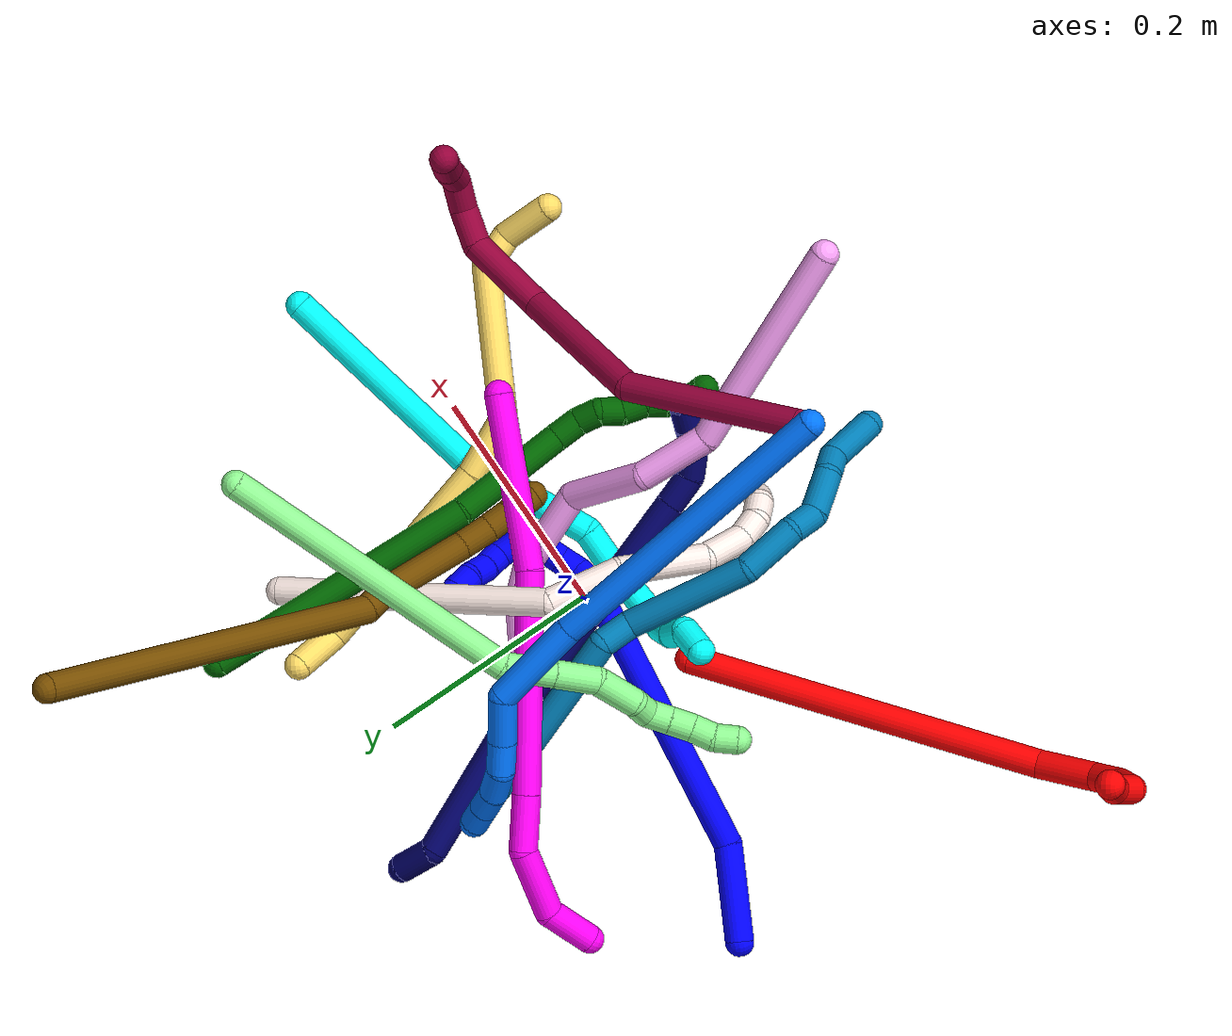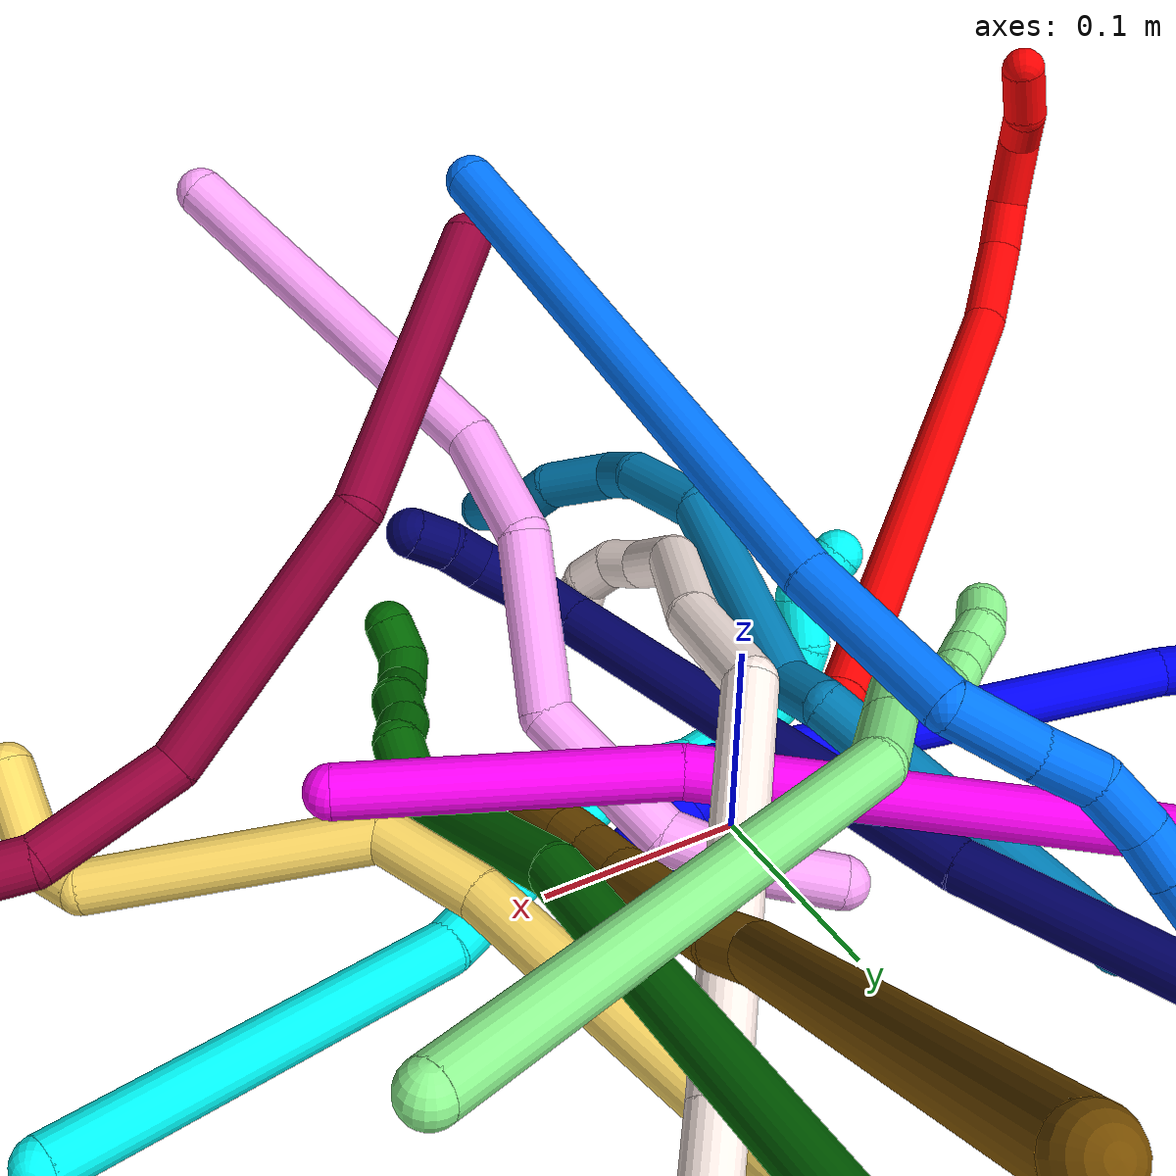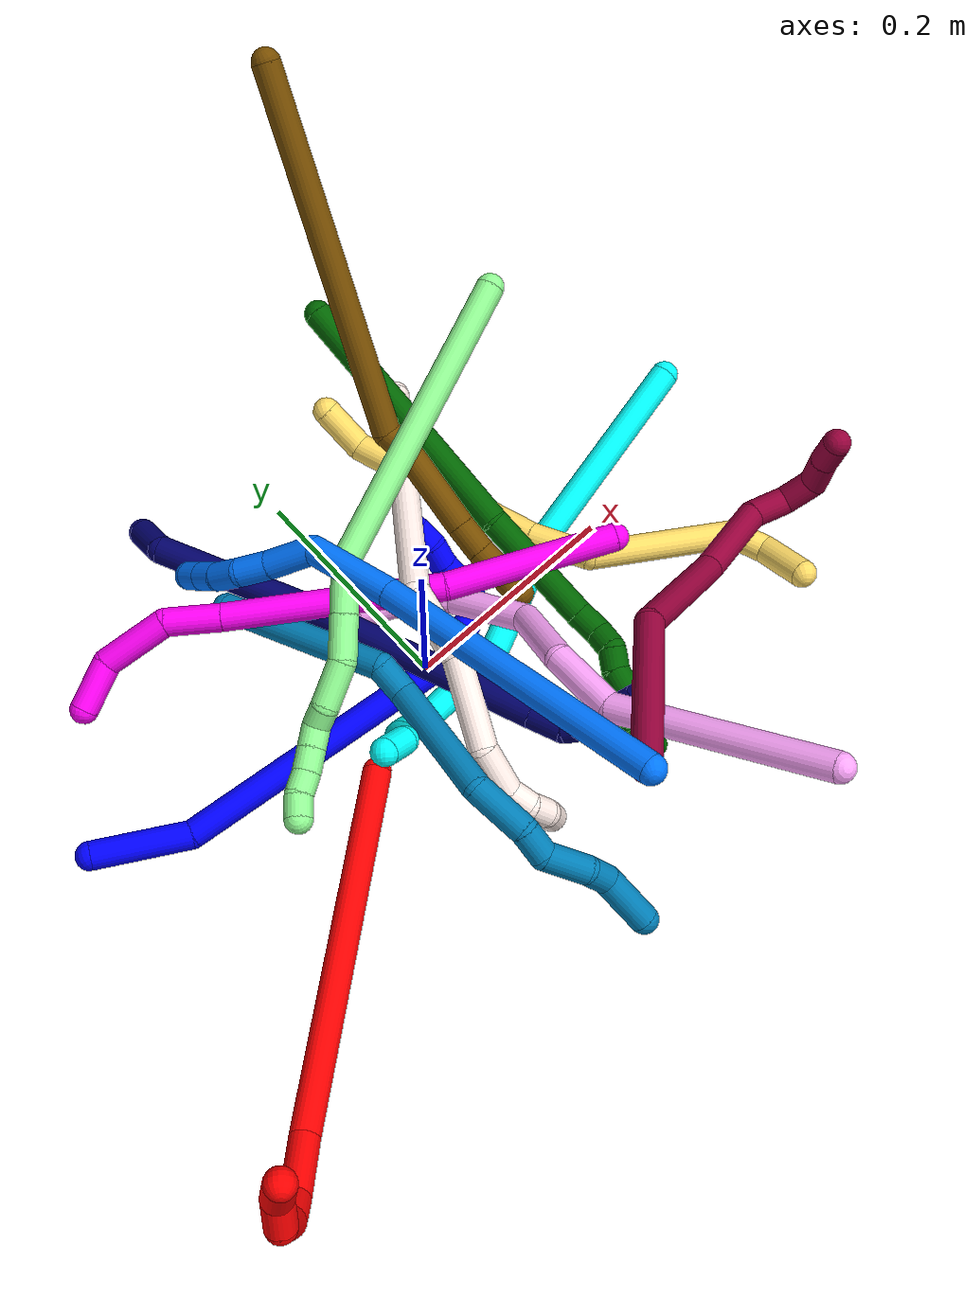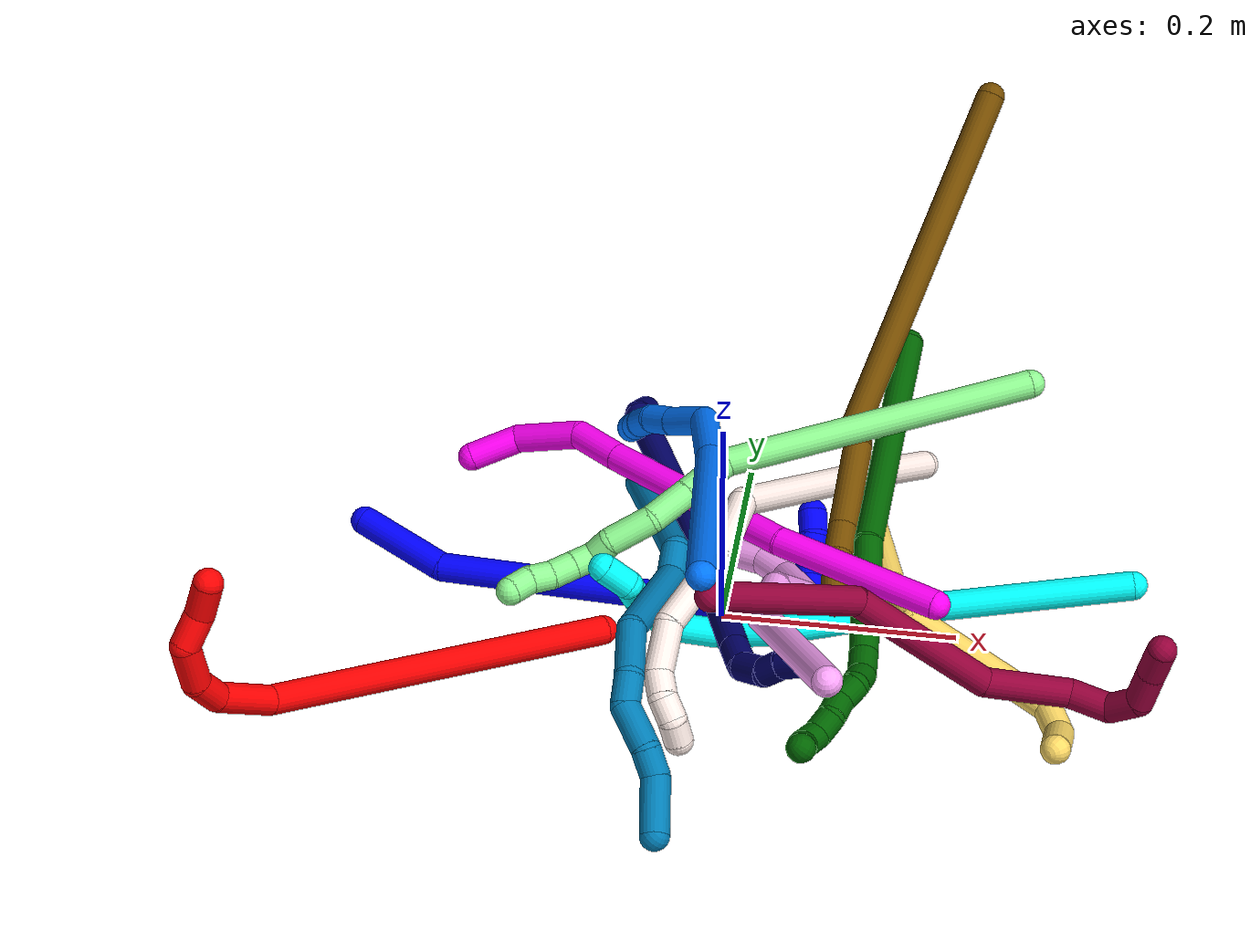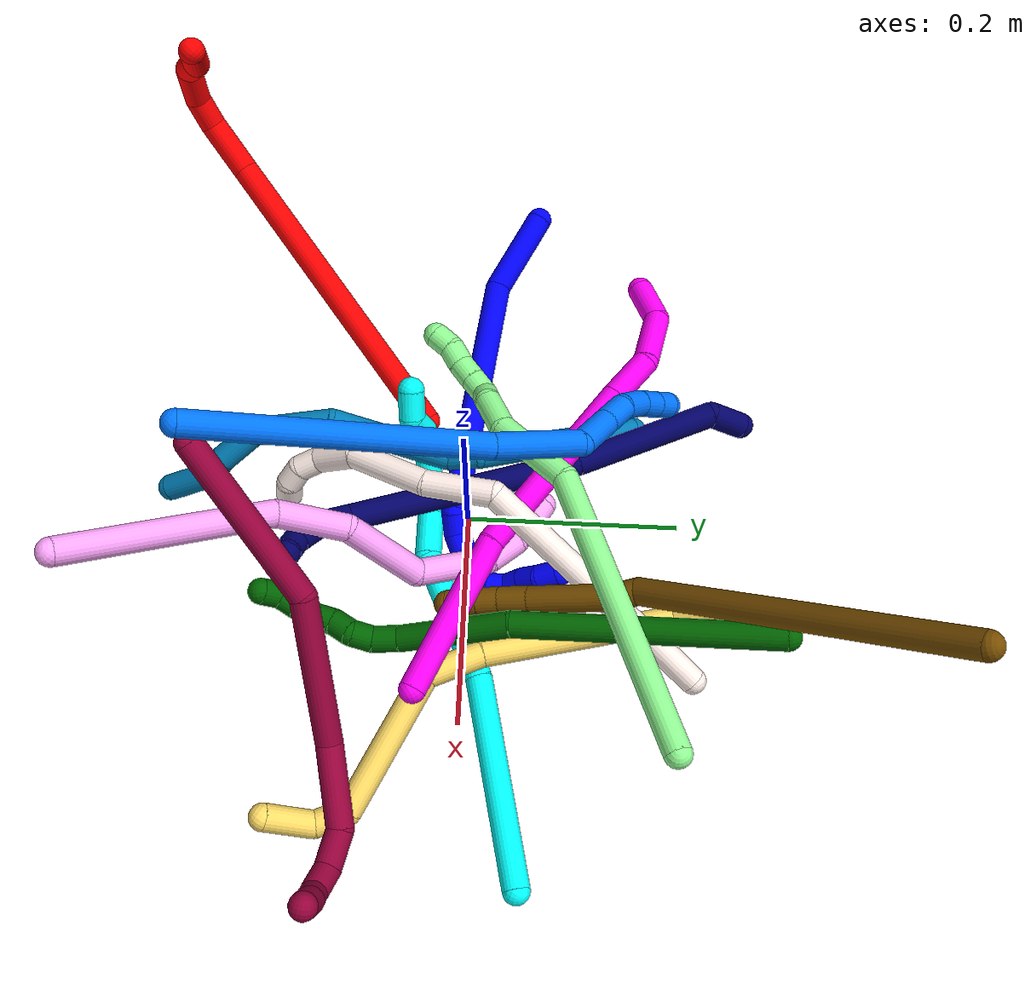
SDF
<sdf version="1.7">
 <world name="default">
  <plugin name="TubeGeneratorPlugin" filename="libtube_generator_plugin.so"/>
  <model name="photoneo_s_sensor">
   <static>1</static>
   <pose>0 0 2 1.57079 1.57079 3.14159</pose>
   <link name="link">
    <inertial><mass>0.1</mass></inertial>
    <sensor name="sensor" type="depth">
     <update_rate>30</update_rate>
     <camera>
      <horizontal_fov>1.22</horizontal_fov>
      <image><width>1920</width><height>1200</height><format>B8G8R8</format></image>
      <clip><near>0.1</near><far>4</far></clip>
      <depth_camera><output>points</output></depth_camera>
     </camera>
     <plugin name="camera_plugin" filename="libgazebo_ros_depth_camera.so">
      <baseline>0.2</baseline>
      <alwaysOn>1</alwaysOn>
      <updateRate>0.0</updateRate>
      <cameraName>camera_ir</cameraName>
      <imageTopicName>/camera/color/image_raw</imageTopicName>
      <cameraInfoTopicName>/camera/color/camera_info</cameraInfoTopicName>
      <depthImageTopicName>/camera/depth/image_raw</depthImageTopicName>
      <depthImageCameraInfoTopicName>/camera/depth/camera_info</depthImageCameraInfoTopicName>
      <pointCloudTopicName>/camera/depth/points</pointCloudTopicName>
      <frameName>fr_optical</frameName>
      <pointCloudCutoff>0.1</pointCloudCutoff>
      <pointCloudCutoffMax>2.0</pointCloudCutoffMax>
      <distortionK1>0</distortionK1>
      <distortionK2>0</distortionK2>
      <distortionK3>0</distortionK3>
      <distortionT1>0</distortionT1>
      <distortionT2>0</distortionT2>
      <CxPrime>0</CxPrime>
      <Cx>0</Cx>
      <Cy>0</Cy>
      <focalLength>0</focalLength>
      <hackBaseline>0</hackBaseline>
     </plugin>
    </sensor>
   </link>
  </model>
  <gravity>0 0 -9.8</gravity>
  <magnetic_field>6e-06 2.3e-05 -4.2e-05</magnetic_field>
  <atmosphere type="adiabatic"/>
  <physics name="default_physics" default="0" type="ode">
   <max_step_size>0.003</max_step_size>
   <real_time_factor>1</real_time_factor>
   <real_time_update_rate>1000</real_time_update_rate>
   <max_contacts>10000</max_contacts>
   <ode>
    <solver>
     <type>quick</type>
     <iters>100</iters>
     <sor>1.3</sor>
     <use_dynamic_moi_rescaling>0</use_dynamic_moi_rescaling>
    </solver>
    <constraints>
     <contact_max_correcting_vel>0</contact_max_correcting_vel>
     <contact_surface_layer>0.001</contact_surface_layer>
     <cfm>0</cfm>
     <erp>0.2</erp>
    </constraints>
   </ode>
  </physics>
  <scene><ambient>0.4 0.4 0.4 1</ambient><background>0.7 0.7 0.7 1</background><shadows>0</shadows></scene>
  <audio><device>default</device></audio>
  <spherical_coordinates>
   <surface_model>EARTH_WGS84</surface_model>
   <latitude_deg>0</latitude_deg>
   <longitude_deg>0</longitude_deg>
   <elevation>0</elevation>
   <heading_deg>0</heading_deg>
  </spherical_coordinates>
  <model name="bin">
   <static>1</static>
   <link name="bottom">
    <collision name="collision-bottom">
     <pose>0 0 -0.01 0 -0 0</pose>
     <geometry><box><size>0.8 0.6 0.02</size></box></geometry>
     <surface>
      <friction><ode><mu>100</mu><mu2>100</mu2></ode></friction>
      <contact><collide_bitmask>65535</collide_bitmask></contact>
     </surface>
    </collision>
   </link>
   <link name="west_wall">
    <collision name="collision-west_wall">
     <pose>-0.41 0 0.1 0 -0 0</pose>
     <geometry><box><size>0.02 0.6 0.2</size></box></geometry>
     <surface>
      <friction><ode><mu>100</mu><mu2>100</mu2></ode></friction>
      <contact><collide_bitmask>65535</collide_bitmask></contact>
     </surface>
    </collision>
   </link>
   <link name="east_wall">
    <collision name="collision-east_wall">
     <pose>0.41 0 0.1 0 -0 0</pose>
     <geometry><box><size>0.02 0.6 0.2</size></box></geometry>
     <surface>
      <friction><ode><mu>100</mu><mu2>100</mu2></ode></friction>
      <contact><collide_bitmask>65535</collide_bitmask></contact>
     </surface>
    </collision>
   </link>
   <link name="south_wall">
    <collision name="collision-south_wall">
     <pose>0 -0.31 0.1 0 -0 0</pose>
     <geometry><box><size>0.8 0.02 0.2</size></box></geometry>
     <surface>
      <friction><ode><mu>100</mu><mu2>100</mu2></ode></friction>
      <contact><collide_bitmask>65535</collide_bitmask></contact>
     </surface>
    </collision>
   </link>
   <link name="north_wall">
    <collision name="collision-north_wall">
     <pose>0 0.31 0.1 0 -0 0</pose>
     <geometry><box><size>0.8 0.02 0.2</size></box></geometry>
     <surface>
      <friction><ode><mu>100</mu><mu2>100</mu2></ode></friction>
      <contact><collide_bitmask>65535</collide_bitmask></contact>
     </surface>
    </collision>
   </link>
  </model>
  <model name="1">
   <static>0</static>
   <link name="1">
    <collision name="collision-cylinder-e_1_1_4">
     <pose>0.037311 -0.018902 0.008462 1.14986 1.06408 0.728776</pose>
     <geometry><cylinder><radius>0.0125</radius><length>0.085346</length></cylinder></geometry>
     <surface>
      <friction><ode><mu>1.16</mu><mu2>1.16</mu2><slip1>0</slip1><slip2>0</slip2></ode></friction>
      <contact><ode><kp>1e+06</kp><kd>1</kd><max_vel>0</max_vel><min_depth>0.001</min_depth></ode></contact>
     </surface>
    </collision>
    <visual name="visual-cylinder-e_1_1_4">
     <pose>0.037311 -0.018902 0.008462 1.14986 1.06408 0.728776</pose>
     <geometry><cylinder><radius>0.0125</radius><length>0.085346</length></cylinder></geometry>
     <material><ambient>0 0 1 1</ambient></material>
    </visual>
    <collision name="collision-cylinder-e_2_4_5">
     <pose>0.189324 -0.082721 -0.007608 2.07069 1.15111 1.66021</pose>
     <geometry><cylinder><radius>0.0125</radius><length>0.251205</length></cylinder></geometry>
     <surface>
      <friction><ode><mu>1.16</mu><mu2>1.16</mu2><slip1>0</slip1><slip2>0</slip2></ode></friction>
      <contact><ode><kp>1e+06</kp><kd>1</kd><max_vel>0</max_vel><min_depth>0.001</min_depth></ode></contact>
     </surface>
    </collision>
    <visual name="visual-cylinder-e_2_4_5">
     <pose>0.189324 -0.082721 -0.007608 2.07069 1.15111 1.66021</pose>
     <geometry><cylinder><radius>0.0125</radius><length>0.251205</length></cylinder></geometry>
     <material><ambient>0 0 1 1</ambient></material>
    </visual>
    <collision name="collision-cylinder-e_3_5_6">
     <pose>0.308933 -0.137888 -0.03487 1.83108 0.433271 0.557823</pose>
     <geometry><cylinder><radius>0.0125</radius><length>0.023374</length></cylinder></geometry>
     <surface>
      <friction><ode><mu>1.16</mu><mu2>1.16</mu2><slip1>0</slip1><slip2>0</slip2></ode></friction>
      <contact><ode><kp>1e+06</kp><kd>1</kd><max_vel>0</max_vel><min_depth>0.001</min_depth></ode></contact>
     </surface>
    </collision>
    <visual name="visual-cylinder-e_3_5_6">
     <pose>0.308933 -0.137888 -0.03487 1.83108 0.433271 0.557823</pose>
     <geometry><cylinder><radius>0.0125</radius><length>0.023374</length></cylinder></geometry>
     <material><ambient>0 0 1 1</ambient></material>
    </visual>
    <collision name="collision-cylinder-e_4_6_7">
     <pose>0.320264 -0.152454 -0.043966 2.54577 0.695776 1.73644</pose>
     <geometry><cylinder><radius>0.0125</radius><length>0.020044</length></cylinder></geometry>
     <surface>
      <friction><ode><mu>1.16</mu><mu2>1.16</mu2><slip1>0</slip1><slip2>0</slip2></ode></friction>
      <contact><ode><kp>1e+06</kp><kd>1</kd><max_vel>0</max_vel><min_depth>0.001</min_depth></ode></contact>
     </surface>
    </collision>
    <visual name="visual-cylinder-e_4_6_7">
     <pose>0.320264 -0.152454 -0.043966 2.54577 0.695776 1.73644</pose>
     <geometry><cylinder><radius>0.0125</radius><length>0.020044</length></cylinder></geometry>
     <material><ambient>0 0 1 1</ambient></material>
    </visual>
    <collision name="collision-cylinder-e_5_7_8">
     <pose>0.333879 -0.160015 -0.0565 2.65725 0.801183 2.0855</pose>
     <geometry><cylinder><radius>0.0125</radius><length>0.020027</length></cylinder></geometry>
     <surface>
      <friction><ode><mu>1.16</mu><mu2>1.16</mu2><slip1>0</slip1><slip2>0</slip2></ode></friction>
      <contact><ode><kp>1e+06</kp><kd>1</kd><max_vel>0</max_vel><min_depth>0.001</min_depth></ode></contact>
     </surface>
    </collision>
    <visual name="visual-cylinder-e_5_7_8">
     <pose>0.333879 -0.160015 -0.0565 2.65725 0.801183 2.0855</pose>
     <geometry><cylinder><radius>0.0125</radius><length>0.020027</length></cylinder></geometry>
     <material><ambient>0 0 1 1</ambient></material>
    </visual>
    <collision name="collision-cylinder-e_6_8_9">
     <pose>0.34455 -0.165966 -0.071643 2.84875 0.355384 1.7665</pose>
     <geometry><cylinder><radius>0.0125</radius><length>0.020001</length></cylinder></geometry>
     <surface>
      <friction><ode><mu>1.16</mu><mu2>1.16</mu2><slip1>0</slip1><slip2>0</slip2></ode></friction>
      <contact><ode><kp>1e+06</kp><kd>1</kd><max_vel>0</max_vel><min_depth>0.001</min_depth></ode></contact>
     </surface>
    </collision>
    <visual name="visual-cylinder-e_6_8_9">
     <pose>0.34455 -0.165966 -0.071643 2.84875 0.355384 1.7665</pose>
     <geometry><cylinder><radius>0.0125</radius><length>0.020001</length></cylinder></geometry>
     <material><ambient>0 0 1 1</ambient></material>
    </visual>
    <collision name="collision-cylinder-e_7_9_10">
     <pose>0.344495 -0.16968 -0.089919 3.03377 -0.361225 -2.56693</pose>
     <geometry><cylinder><radius>0.0125</radius><length>0.02</length></cylinder></geometry>
     <surface>
      <friction><ode><mu>1.16</mu><mu2>1.16</mu2><slip1>0</slip1><slip2>0</slip2></ode></friction>
      <contact><ode><kp>1e+06</kp><kd>1</kd><max_vel>0</max_vel><min_depth>0.001</min_depth></ode></contact>
     </surface>
    </collision>
    <visual name="visual-cylinder-e_7_9_10">
     <pose>0.344495 -0.16968 -0.089919 3.03377 -0.361225 -2.56693</pose>
     <geometry><cylinder><radius>0.0125</radius><length>0.02</length></cylinder></geometry>
     <material><ambient>0 0 1 1</ambient></material>
    </visual>
    <collision name="collision-cylinder-e_8_10_11">
     <pose>0.339396 -0.164922 -0.107242 -2.51856 -0.157135 0.479592</pose>
     <geometry><cylinder><radius>0.0125</radius><length>0.020003</length></cylinder></geometry>
     <surface>
      <friction><ode><mu>1.16</mu><mu2>1.16</mu2><slip1>0</slip1><slip2>0</slip2></ode></friction>
      <contact><ode><kp>1e+06</kp><kd>1</kd><max_vel>0</max_vel><min_depth>0.001</min_depth></ode></contact>
     </surface>
    </collision>
    <visual name="visual-cylinder-e_8_10_11">
     <pose>0.339396 -0.164922 -0.107242 -2.51856 -0.157135 0.479592</pose>
     <geometry><cylinder><radius>0.0125</radius><length>0.020003</length></cylinder></geometry>
     <material><ambient>0 0 1 1</ambient></material>
    </visual>
    <collision name="collision-cylinder-e_9_11_12">
     <pose>0.337993 -0.154013 -0.123838 -2.60112 0.016186 -0.058416</pose>
     <geometry><cylinder><radius>0.0125</radius><length>0.02</length></cylinder></geometry>
     <surface>
      <friction><ode><mu>1.16</mu><mu2>1.16</mu2><slip1>0</slip1><slip2>0</slip2></ode></friction>
      <contact><ode><kp>1e+06</kp><kd>1</kd><max_vel>0</max_vel><min_depth>0.001</min_depth></ode></contact>
     </surface>
    </collision>
    <visual name="visual-cylinder-e_9_11_12">
     <pose>0.337993 -0.154013 -0.123838 -2.60112 0.016186 -0.058416</pose>
     <geometry><cylinder><radius>0.0125</radius><length>0.02</length></cylinder></geometry>
     <material><ambient>0 0 1 1</ambient></material>
    </visual>
    <collision name="collision-cylinder-e_10_12_2">
     <pose>0.335138 -0.145157 -0.141194 -2.74168 -0.306384 1.3021</pose>
     <geometry><cylinder><radius>0.0125</radius><length>0.02</length></cylinder></geometry>
     <surface>
      <friction><ode><mu>1.16</mu><mu2>1.16</mu2><slip1>0</slip1><slip2>0</slip2></ode></friction>
      <contact><ode><kp>1e+06</kp><kd>1</kd><max_vel>0</max_vel><min_depth>0.001</min_depth></ode></contact>
     </surface>
    </collision>
    <visual name="visual-cylinder-e_10_12_2">
     <pose>0.335138 -0.145157 -0.141194 -2.74168 -0.306384 1.3021</pose>
     <geometry><cylinder><radius>0.0125</radius><length>0.02</length></cylinder></geometry>
     <material><ambient>0 0 1 1</ambient></material>
    </visual>
    <collision name="collision-sphere-2">
     <pose>0.332122 -0.141444 -0.149976 0 -0 0</pose>
     <geometry><sphere><radius>0.0125</radius></sphere></geometry>
     <surface>
      <friction><ode><mu>1.16</mu><mu2>1.16</mu2><slip1>0</slip1><slip2>0</slip2></ode></friction>
      <contact><ode><kp>1e+06</kp><kd>1</kd><max_vel>0</max_vel><min_depth>0.001</min_depth></ode></contact>
     </surface>
    </collision>
    <visual name="visual-sphere-2">
     <pose>0.332122 -0.141444 -0.149976 0 -0 0</pose>
     <geometry><sphere><radius>0.0125</radius></sphere></geometry>
     <material><ambient>0 0 1 1</ambient></material>
    </visual>
    <collision name="collision-sphere-12">
     <pose>0.338154 -0.148869 -0.132412 0 -0 0</pose>
     <geometry><sphere><radius>0.0125</radius></sphere></geometry>
     <surface>
      <friction><ode><mu>1.16</mu><mu2>1.16</mu2><slip1>0</slip1><slip2>0</slip2></ode></friction>
      <contact><ode><kp>1e+06</kp><kd>1</kd><max_vel>0</max_vel><min_depth>0.001</min_depth></ode></contact>
     </surface>
    </collision>
    <visual name="visual-sphere-12">
     <pose>0.338154 -0.148869 -0.132412 0 -0 0</pose>
     <geometry><sphere><radius>0.0125</radius></sphere></geometry>
     <material><ambient>0 0 1 1</ambient></material>
    </visual>
    <collision name="collision-sphere-11">
     <pose>0.337831 -0.159158 -0.115265 0 -0 0</pose>
     <geometry><sphere><radius>0.0125</radius></sphere></geometry>
     <surface>
      <friction><ode><mu>1.16</mu><mu2>1.16</mu2><slip1>0</slip1><slip2>0</slip2></ode></friction>
      <contact><ode><kp>1e+06</kp><kd>1</kd><max_vel>0</max_vel><min_depth>0.001</min_depth></ode></contact>
     </surface>
    </collision>
    <visual name="visual-sphere-11">
     <pose>0.337831 -0.159158 -0.115265 0 -0 0</pose>
     <geometry><sphere><radius>0.0125</radius></sphere></geometry>
     <material><ambient>0 0 1 1</ambient></material>
    </visual>
    <collision name="collision-sphere-10">
     <pose>0.340961 -0.170686 -0.09922 0 -0 0</pose>
     <geometry><sphere><radius>0.0125</radius></sphere></geometry>
     <surface>
      <friction><ode><mu>1.16</mu><mu2>1.16</mu2><slip1>0</slip1><slip2>0</slip2></ode></friction>
      <contact><ode><kp>1e+06</kp><kd>1</kd><max_vel>0</max_vel><min_depth>0.001</min_depth></ode></contact>
     </surface>
    </collision>
    <visual name="visual-sphere-10">
     <pose>0.340961 -0.170686 -0.09922 0 -0 0</pose>
     <geometry><sphere><radius>0.0125</radius></sphere></geometry>
     <material><ambient>0 0 1 1</ambient></material>
    </visual>
    <collision name="collision-sphere-9">
     <pose>0.34803 -0.168673 -0.080619 0 -0 0</pose>
     <geometry><sphere><radius>0.0125</radius></sphere></geometry>
     <surface>
      <friction><ode><mu>1.16</mu><mu2>1.16</mu2><slip1>0</slip1><slip2>0</slip2></ode></friction>
      <contact><ode><kp>1e+06</kp><kd>1</kd><max_vel>0</max_vel><min_depth>0.001</min_depth></ode></contact>
     </surface>
    </collision>
    <visual name="visual-sphere-9">
     <pose>0.34803 -0.168673 -0.080619 0 -0 0</pose>
     <geometry><sphere><radius>0.0125</radius></sphere></geometry>
     <material><ambient>0 0 1 1</ambient></material>
    </visual>
    <collision name="collision-sphere-4">
     <pose>0.074622 -0.037803 0.016924 0 -0 0</pose>
     <geometry><sphere><radius>0.0125</radius></sphere></geometry>
     <surface>
      <friction><ode><mu>1.16</mu><mu2>1.16</mu2><slip1>0</slip1><slip2>0</slip2></ode></friction>
      <contact><ode><kp>1e+06</kp><kd>1</kd><max_vel>0</max_vel><min_depth>0.001</min_depth></ode></contact>
     </surface>
    </collision>
    <visual name="visual-sphere-4">
     <pose>0.074622 -0.037803 0.016924 0 -0 0</pose>
     <geometry><sphere><radius>0.0125</radius></sphere></geometry>
     <material><ambient>0 0 1 1</ambient></material>
    </visual>
    <collision name="collision-sphere-1">
     <geometry><sphere><radius>0.0125</radius></sphere></geometry>
     <surface>
      <friction><ode><mu>1.16</mu><mu2>1.16</mu2><slip1>0</slip1><slip2>0</slip2></ode></friction>
      <contact><ode><kp>1e+06</kp><kd>1</kd><max_vel>0</max_vel><min_depth>0.001</min_depth></ode></contact>
     </surface>
    </collision>
    <visual name="visual-sphere-1">
     <geometry><sphere><radius>0.0125</radius></sphere></geometry>
     <material><ambient>0 0 1 1</ambient></material>
    </visual>
    <collision name="collision-sphere-8">
     <pose>0.34107 -0.16326 -0.062666 0 -0 0</pose>
     <geometry><sphere><radius>0.0125</radius></sphere></geometry>
     <surface>
      <friction><ode><mu>1.16</mu><mu2>1.16</mu2><slip1>0</slip1><slip2>0</slip2></ode></friction>
      <contact><ode><kp>1e+06</kp><kd>1</kd><max_vel>0</max_vel><min_depth>0.001</min_depth></ode></contact>
     </surface>
    </collision>
    <visual name="visual-sphere-8">
     <pose>0.34107 -0.16326 -0.062666 0 -0 0</pose>
     <geometry><sphere><radius>0.0125</radius></sphere></geometry>
     <material><ambient>0 0 1 1</ambient></material>
    </visual>
    <collision name="collision-sphere-5">
     <pose>0.304026 -0.127638 -0.03214 0 -0 0</pose>
     <geometry><sphere><radius>0.0125</radius></sphere></geometry>
     <surface>
      <friction><ode><mu>1.16</mu><mu2>1.16</mu2><slip1>0</slip1><slip2>0</slip2></ode></friction>
      <contact><ode><kp>1e+06</kp><kd>1</kd><max_vel>0</max_vel><min_depth>0.001</min_depth></ode></contact>
     </surface>
    </collision>
    <visual name="visual-sphere-5">
     <pose>0.304026 -0.127638 -0.03214 0 -0 0</pose>
     <geometry><sphere><radius>0.0125</radius></sphere></geometry>
     <material><ambient>0 0 1 1</ambient></material>
    </visual>
    <collision name="collision-sphere-6">
     <pose>0.31384 -0.148137 -0.037599 0 -0 0</pose>
     <geometry><sphere><radius>0.0125</radius></sphere></geometry>
     <surface>
      <friction><ode><mu>1.16</mu><mu2>1.16</mu2><slip1>0</slip1><slip2>0</slip2></ode></friction>
      <contact><ode><kp>1e+06</kp><kd>1</kd><max_vel>0</max_vel><min_depth>0.001</min_depth></ode></contact>
     </surface>
    </collision>
    <visual name="visual-sphere-6">
     <pose>0.31384 -0.148137 -0.037599 0 -0 0</pose>
     <geometry><sphere><radius>0.0125</radius></sphere></geometry>
     <material><ambient>0 0 1 1</ambient></material>
    </visual>
    <collision name="collision-sphere-7">
     <pose>0.326687 -0.156771 -0.050333 0 -0 0</pose>
     <geometry><sphere><radius>0.0125</radius></sphere></geometry>
     <surface>
      <friction><ode><mu>1.16</mu><mu2>1.16</mu2><slip1>0</slip1><slip2>0</slip2></ode></friction>
      <contact><ode><kp>1e+06</kp><kd>1</kd><max_vel>0</max_vel><min_depth>0.001</min_depth></ode></contact>
     </surface>
    </collision>
    <visual name="visual-sphere-7">
     <pose>0.326687 -0.156771 -0.050333 0 -0 0</pose>
     <geometry><sphere><radius>0.0125</radius></sphere></geometry>
     <material><ambient>0 0 1 1</ambient></material>
    </visual>
    <inertial>
     <pose>0.210206 -0.095744 -0.029388 0 -0 0</pose>
     <mass>0.5</mass>
     <inertia>
      <ixx>0.000563</ixx>
      <ixy>0</ixy>
      <ixz>0</ixz>
      <iyy>0.001719</iyy>
      <iyz>0</iyz>
      <izz>-0.000776</izz>
     </inertia>
    </inertial>
   </link>
   <pose>-0.321985 0.056449 0.022664 1.83104 -0.369598 -0.405315</pose>
  </model>
  <model name="2">
   <static>0</static>
   <link name="2">
    <collision name="collision-cylinder-e_1_1_4">
     <pose>-0.029259 -0.040347 0.14996 0.262829 -0.186225 -0.024685</pose>
     <geometry><cylinder><radius>0.0125</radius><length>0.316051</length></cylinder></geometry>
     <surface>
      <friction><ode><mu>1.16</mu><mu2>1.16</mu2><slip1>0</slip1><slip2>0</slip2></ode></friction>
      <contact><ode><kp>1e+06</kp><kd>1</kd><max_vel>0</max_vel><min_depth>0.001</min_depth></ode></contact>
     </surface>
    </collision>
    <visual name="visual-cylinder-e_1_1_4">
     <pose>-0.029259 -0.040347 0.14996 0.262829 -0.186225 -0.024685</pose>
     <geometry><cylinder><radius>0.0125</radius><length>0.316051</length></cylinder></geometry>
     <material><ambient>1 0 0 1</ambient></material>
    </visual>
    <collision name="collision-cylinder-e_2_4_5">
     <pose>-0.063939 -0.078573 0.326318 -0.080179 -0.201931 0.008127</pose>
     <geometry><cylinder><radius>0.0125</radius><length>0.054063</length></cylinder></geometry>
     <surface>
      <friction><ode><mu>1.16</mu><mu2>1.16</mu2><slip1>0</slip1><slip2>0</slip2></ode></friction>
      <contact><ode><kp>1e+06</kp><kd>1</kd><max_vel>0</max_vel><min_depth>0.001</min_depth></ode></contact>
     </surface>
    </collision>
    <visual name="visual-cylinder-e_2_4_5">
     <pose>-0.063939 -0.078573 0.326318 -0.080179 -0.201931 0.008127</pose>
     <geometry><cylinder><radius>0.0125</radius><length>0.054063</length></cylinder></geometry>
     <material><ambient>1 0 0 1</ambient></material>
    </visual>
    <collision name="collision-cylinder-e_3_5_6">
     <pose>-0.073362 -0.069329 0.365291 -0.515398 -0.270116 0.071597</pose>
     <geometry><cylinder><radius>0.0125</radius><length>0.029994</length></cylinder></geometry>
     <surface>
      <friction><ode><mu>1.16</mu><mu2>1.16</mu2><slip1>0</slip1><slip2>0</slip2></ode></friction>
      <contact><ode><kp>1e+06</kp><kd>1</kd><max_vel>0</max_vel><min_depth>0.001</min_depth></ode></contact>
     </surface>
    </collision>
    <visual name="visual-cylinder-e_3_5_6">
     <pose>-0.073362 -0.069329 0.365291 -0.515398 -0.270116 0.071597</pose>
     <geometry><cylinder><radius>0.0125</radius><length>0.029994</length></cylinder></geometry>
     <material><ambient>1 0 0 1</ambient></material>
    </visual>
    <collision name="collision-cylinder-e_4_6_7">
     <pose>-0.084397 -0.04656 0.387837 -1.00337 -0.362375 0.200293</pose>
     <geometry><cylinder><radius>0.0125</radius><length>0.039681</length></cylinder></geometry>
     <surface>
      <friction><ode><mu>1.16</mu><mu2>1.16</mu2><slip1>0</slip1><slip2>0</slip2></ode></friction>
      <contact><ode><kp>1e+06</kp><kd>1</kd><max_vel>0</max_vel><min_depth>0.001</min_depth></ode></contact>
     </surface>
    </collision>
    <visual name="visual-cylinder-e_4_6_7">
     <pose>-0.084397 -0.04656 0.387837 -1.00337 -0.362375 0.200293</pose>
     <geometry><cylinder><radius>0.0125</radius><length>0.039681</length></cylinder></geometry>
     <material><ambient>1 0 0 1</ambient></material>
    </visual>
    <collision name="collision-cylinder-e_5_7_8">
     <pose>-0.095566 -0.017419 0.394436 -1.81566 -0.288944 0.368399</pose>
     <geometry><cylinder><radius>0.0125</radius><length>0.029027</length></cylinder></geometry>
     <surface>
      <friction><ode><mu>1.16</mu><mu2>1.16</mu2><slip1>0</slip1><slip2>0</slip2></ode></friction>
      <contact><ode><kp>1e+06</kp><kd>1</kd><max_vel>0</max_vel><min_depth>0.001</min_depth></ode></contact>
     </surface>
    </collision>
    <visual name="visual-cylinder-e_5_7_8">
     <pose>-0.095566 -0.017419 0.394436 -1.81566 -0.288944 0.368399</pose>
     <geometry><cylinder><radius>0.0125</radius><length>0.029027</length></cylinder></geometry>
     <material><ambient>1 0 0 1</ambient></material>
    </visual>
    <collision name="collision-cylinder-e_6_8_2">
     <pose>-0.102052 0.011263 0.393711 -1.39819 -0.15136 0.127326</pose>
     <geometry><cylinder><radius>0.0125</radius><length>0.031185</length></cylinder></geometry>
     <surface>
      <friction><ode><mu>1.16</mu><mu2>1.16</mu2><slip1>0</slip1><slip2>0</slip2></ode></friction>
      <contact><ode><kp>1e+06</kp><kd>1</kd><max_vel>0</max_vel><min_depth>0.001</min_depth></ode></contact>
     </surface>
    </collision>
    <visual name="visual-cylinder-e_6_8_2">
     <pose>-0.102052 0.011263 0.393711 -1.39819 -0.15136 0.127326</pose>
     <geometry><cylinder><radius>0.0125</radius><length>0.031185</length></cylinder></geometry>
     <material><ambient>1 0 0 1</ambient></material>
    </visual>
    <collision name="collision-sphere-2">
     <pose>-0.104403 0.026448 0.396358 0 -0 0</pose>
     <geometry><sphere><radius>0.0125</radius></sphere></geometry>
     <surface>
      <friction><ode><mu>1.16</mu><mu2>1.16</mu2><slip1>0</slip1><slip2>0</slip2></ode></friction>
      <contact><ode><kp>1e+06</kp><kd>1</kd><max_vel>0</max_vel><min_depth>0.001</min_depth></ode></contact>
     </surface>
    </collision>
    <visual name="visual-sphere-2">
     <pose>-0.104403 0.026448 0.396358 0 -0 0</pose>
     <geometry><sphere><radius>0.0125</radius></sphere></geometry>
     <material><ambient>1 0 0 1</ambient></material>
    </visual>
    <collision name="collision-sphere-4">
     <pose>-0.058517 -0.080695 0.299921 0 -0 0</pose>
     <geometry><sphere><radius>0.0125</radius></sphere></geometry>
     <surface>
      <friction><ode><mu>1.16</mu><mu2>1.16</mu2><slip1>0</slip1><slip2>0</slip2></ode></friction>
      <contact><ode><kp>1e+06</kp><kd>1</kd><max_vel>0</max_vel><min_depth>0.001</min_depth></ode></contact>
     </surface>
    </collision>
    <visual name="visual-sphere-4">
     <pose>-0.058517 -0.080695 0.299921 0 -0 0</pose>
     <geometry><sphere><radius>0.0125</radius></sphere></geometry>
     <material><ambient>1 0 0 1</ambient></material>
    </visual>
    <collision name="collision-sphere-1">
     <geometry><sphere><radius>0.0125</radius></sphere></geometry>
     <surface>
      <friction><ode><mu>1.16</mu><mu2>1.16</mu2><slip1>0</slip1><slip2>0</slip2></ode></friction>
      <contact><ode><kp>1e+06</kp><kd>1</kd><max_vel>0</max_vel><min_depth>0.001</min_depth></ode></contact>
     </surface>
    </collision>
    <visual name="visual-sphere-1">
     <geometry><sphere><radius>0.0125</radius></sphere></geometry>
     <material><ambient>1 0 0 1</ambient></material>
    </visual>
    <collision name="collision-sphere-8">
     <pose>-0.099701 -0.003922 0.391063 0 -0 0</pose>
     <geometry><sphere><radius>0.0125</radius></sphere></geometry>
     <surface>
      <friction><ode><mu>1.16</mu><mu2>1.16</mu2><slip1>0</slip1><slip2>0</slip2></ode></friction>
      <contact><ode><kp>1e+06</kp><kd>1</kd><max_vel>0</max_vel><min_depth>0.001</min_depth></ode></contact>
     </surface>
    </collision>
    <visual name="visual-sphere-8">
     <pose>-0.099701 -0.003922 0.391063 0 -0 0</pose>
     <geometry><sphere><radius>0.0125</radius></sphere></geometry>
     <material><ambient>1 0 0 1</ambient></material>
    </visual>
    <collision name="collision-sphere-5">
     <pose>-0.06936 -0.076452 0.352715 0 -0 0</pose>
     <geometry><sphere><radius>0.0125</radius></sphere></geometry>
     <surface>
      <friction><ode><mu>1.16</mu><mu2>1.16</mu2><slip1>0</slip1><slip2>0</slip2></ode></friction>
      <contact><ode><kp>1e+06</kp><kd>1</kd><max_vel>0</max_vel><min_depth>0.001</min_depth></ode></contact>
     </surface>
    </collision>
    <visual name="visual-sphere-5">
     <pose>-0.06936 -0.076452 0.352715 0 -0 0</pose>
     <geometry><sphere><radius>0.0125</radius></sphere></geometry>
     <material><ambient>1 0 0 1</ambient></material>
    </visual>
    <collision name="collision-sphere-6">
     <pose>-0.077364 -0.062205 0.377866 0 -0 0</pose>
     <geometry><sphere><radius>0.0125</radius></sphere></geometry>
     <surface>
      <friction><ode><mu>1.16</mu><mu2>1.16</mu2><slip1>0</slip1><slip2>0</slip2></ode></friction>
      <contact><ode><kp>1e+06</kp><kd>1</kd><max_vel>0</max_vel><min_depth>0.001</min_depth></ode></contact>
     </surface>
    </collision>
    <visual name="visual-sphere-6">
     <pose>-0.077364 -0.062205 0.377866 0 -0 0</pose>
     <geometry><sphere><radius>0.0125</radius></sphere></geometry>
     <material><ambient>1 0 0 1</ambient></material>
    </visual>
    <collision name="collision-sphere-7">
     <pose>-0.09143 -0.030916 0.397808 0 -0 0</pose>
     <geometry><sphere><radius>0.0125</radius></sphere></geometry>
     <surface>
      <friction><ode><mu>1.16</mu><mu2>1.16</mu2><slip1>0</slip1><slip2>0</slip2></ode></friction>
      <contact><ode><kp>1e+06</kp><kd>1</kd><max_vel>0</max_vel><min_depth>0.001</min_depth></ode></contact>
     </surface>
    </collision>
    <visual name="visual-sphere-7">
     <pose>-0.09143 -0.030916 0.397808 0 -0 0</pose>
     <geometry><sphere><radius>0.0125</radius></sphere></geometry>
     <material><ambient>1 0 0 1</ambient></material>
    </visual>
    <inertial>
     <pose>-0.048419 -0.042162 0.23022 0 -0 0</pose>
     <mass>0.5</mass>
     <inertia>
      <ixx>0.002559</ixx>
      <ixy>0</ixy>
      <ixz>0</ixz>
      <iyy>0.002518</iyy>
      <iyz>0</iyz>
      <izz>0.001188</izz>
     </inertia>
    </inertial>
   </link>
   <pose>-0.095869 -0.045473 0.011499 1.15284 0.30018 -0.751594</pose>
  </model>
  <model name="3">
   <static>0</static>
   <link name="3">
    <collision name="collision-cylinder-e_1_1_4">
     <pose>-0.061214 -0.020334 -0.071885 2.86593 -0.686456 -2.40112</pose>
     <geometry><cylinder><radius>0.0125</radius><length>0.193164</length></cylinder></geometry>
     <surface>
      <friction><ode><mu>1.16</mu><mu2>1.16</mu2><slip1>0</slip1><slip2>0</slip2></ode></friction>
      <contact><ode><kp>1e+06</kp><kd>1</kd><max_vel>0</max_vel><min_depth>0.001</min_depth></ode></contact>
     </surface>
    </collision>
    <visual name="visual-cylinder-e_1_1_4">
     <pose>-0.061214 -0.020334 -0.071885 2.86593 -0.686456 -2.40112</pose>
     <geometry><cylinder><radius>0.0125</radius><length>0.193164</length></cylinder></geometry>
     <material><ambient>0.003922 1 0.996078 1</ambient></material>
    </visual>
    <collision name="collision-cylinder-e_2_4_5">
     <pose>-0.150584 -0.064458 -0.194059 2.6997 -0.468538 -1.63139</pose>
     <geometry><cylinder><radius>0.0125</radius><length>0.124703</length></cylinder></geometry>
     <surface>
      <friction><ode><mu>1.16</mu><mu2>1.16</mu2><slip1>0</slip1><slip2>0</slip2></ode></friction>
      <contact><ode><kp>1e+06</kp><kd>1</kd><max_vel>0</max_vel><min_depth>0.001</min_depth></ode></contact>
     </surface>
    </collision>
    <visual name="visual-cylinder-e_2_4_5">
     <pose>-0.150584 -0.064458 -0.194059 2.6997 -0.468538 -1.63139</pose>
     <geometry><cylinder><radius>0.0125</radius><length>0.124703</length></cylinder></geometry>
     <material><ambient>0.003922 1 0.996078 1</ambient></material>
    </visual>
    <collision name="collision-cylinder-e_3_5_6">
     <pose>-0.195818 -0.090041 -0.258383 3.01459 -0.878865 -2.8727</pose>
     <geometry><cylinder><radius>0.0125</radius><length>0.044355</length></cylinder></geometry>
     <surface>
      <friction><ode><mu>1.16</mu><mu2>1.16</mu2><slip1>0</slip1><slip2>0</slip2></ode></friction>
      <contact><ode><kp>1e+06</kp><kd>1</kd><max_vel>0</max_vel><min_depth>0.001</min_depth></ode></contact>
     </surface>
    </collision>
    <visual name="visual-cylinder-e_3_5_6">
     <pose>-0.195818 -0.090041 -0.258383 3.01459 -0.878865 -2.8727</pose>
     <geometry><cylinder><radius>0.0125</radius><length>0.044355</length></cylinder></geometry>
     <material><ambient>0.003922 1 0.996078 1</ambient></material>
    </visual>
    <collision name="collision-cylinder-e_4_6_7">
     <pose>-0.22759 -0.099641 -0.284094 2.55213 -0.807999 -1.90667</pose>
     <geometry><cylinder><radius>0.0125</radius><length>0.040653</length></cylinder></geometry>
     <surface>
      <friction><ode><mu>1.16</mu><mu2>1.16</mu2><slip1>0</slip1><slip2>0</slip2></ode></friction>
      <contact><ode><kp>1e+06</kp><kd>1</kd><max_vel>0</max_vel><min_depth>0.001</min_depth></ode></contact>
     </surface>
    </collision>
    <visual name="visual-cylinder-e_4_6_7">
     <pose>-0.22759 -0.099641 -0.284094 2.55213 -0.807999 -1.90667</pose>
     <geometry><cylinder><radius>0.0125</radius><length>0.040653</length></cylinder></geometry>
     <material><ambient>0.003922 1 0.996078 1</ambient></material>
    </visual>
    <collision name="collision-cylinder-e_5_7_8">
     <pose>-0.250174 -0.117488 -0.298567 1.84264 -0.647975 -0.832745</pose>
     <geometry><cylinder><radius>0.0125</radius><length>0.026145</length></cylinder></geometry>
     <surface>
      <friction><ode><mu>1.16</mu><mu2>1.16</mu2><slip1>0</slip1><slip2>0</slip2></ode></friction>
      <contact><ode><kp>1e+06</kp><kd>1</kd><max_vel>0</max_vel><min_depth>0.001</min_depth></ode></contact>
     </surface>
    </collision>
    <visual name="visual-cylinder-e_5_7_8">
     <pose>-0.250174 -0.117488 -0.298567 1.84264 -0.647975 -0.832745</pose>
     <geometry><cylinder><radius>0.0125</radius><length>0.026145</length></cylinder></geometry>
     <material><ambient>0.003922 1 0.996078 1</ambient></material>
    </visual>
    <collision name="collision-cylinder-e_6_8_9">
     <pose>-0.260683 -0.137394 -0.302229 1.65811 -0.258495 -0.281814</pose>
     <geometry><cylinder><radius>0.0125</radius><length>0.020486</length></cylinder></geometry>
     <surface>
      <friction><ode><mu>1.16</mu><mu2>1.16</mu2><slip1>0</slip1><slip2>0</slip2></ode></friction>
      <contact><ode><kp>1e+06</kp><kd>1</kd><max_vel>0</max_vel><min_depth>0.001</min_depth></ode></contact>
     </surface>
    </collision>
    <visual name="visual-cylinder-e_6_8_9">
     <pose>-0.260683 -0.137394 -0.302229 1.65811 -0.258495 -0.281814</pose>
     <geometry><cylinder><radius>0.0125</radius><length>0.020486</length></cylinder></geometry>
     <material><ambient>0.003922 1 0.996078 1</ambient></material>
    </visual>
    <collision name="collision-cylinder-e_7_9_10">
     <pose>-0.261729 -0.158614 -0.304304 1.67709 0.136831 0.152151</pose>
     <geometry><cylinder><radius>0.0125</radius><length>0.023054</length></cylinder></geometry>
     <surface>
      <friction><ode><mu>1.16</mu><mu2>1.16</mu2><slip1>0</slip1><slip2>0</slip2></ode></friction>
      <contact><ode><kp>1e+06</kp><kd>1</kd><max_vel>0</max_vel><min_depth>0.001</min_depth></ode></contact>
     </surface>
    </collision>
    <visual name="visual-cylinder-e_7_9_10">
     <pose>-0.261729 -0.158614 -0.304304 1.67709 0.136831 0.152151</pose>
     <geometry><cylinder><radius>0.0125</radius><length>0.023054</length></cylinder></geometry>
     <material><ambient>0.003922 1 0.996078 1</ambient></material>
    </visual>
    <collision name="collision-cylinder-e_8_10_2">
     <pose>-0.268169 -0.180618 -0.308772 1.86755 -0.623653 -0.821698</pose>
     <geometry><cylinder><radius>0.0125</radius><length>0.027439</length></cylinder></geometry>
     <surface>
      <friction><ode><mu>1.16</mu><mu2>1.16</mu2><slip1>0</slip1><slip2>0</slip2></ode></friction>
      <contact><ode><kp>1e+06</kp><kd>1</kd><max_vel>0</max_vel><min_depth>0.001</min_depth></ode></contact>
     </surface>
    </collision>
    <visual name="visual-cylinder-e_8_10_2">
     <pose>-0.268169 -0.180618 -0.308772 1.86755 -0.623653 -0.821698</pose>
     <geometry><cylinder><radius>0.0125</radius><length>0.027439</length></cylinder></geometry>
     <material><ambient>0.003922 1 0.996078 1</ambient></material>
    </visual>
    <collision name="collision-sphere-2">
     <pose>-0.276181 -0.191268 -0.312029 0 -0 0</pose>
     <geometry><sphere><radius>0.0125</radius></sphere></geometry>
     <surface>
      <friction><ode><mu>1.16</mu><mu2>1.16</mu2><slip1>0</slip1><slip2>0</slip2></ode></friction>
      <contact><ode><kp>1e+06</kp><kd>1</kd><max_vel>0</max_vel><min_depth>0.001</min_depth></ode></contact>
     </surface>
    </collision>
    <visual name="visual-sphere-2">
     <pose>-0.276181 -0.191268 -0.312029 0 -0 0</pose>
     <geometry><sphere><radius>0.0125</radius></sphere></geometry>
     <material><ambient>0.003922 1 0.996078 1</ambient></material>
    </visual>
    <collision name="collision-sphere-10">
     <pose>-0.260156 -0.169969 -0.305516 0 -0 0</pose>
     <geometry><sphere><radius>0.0125</radius></sphere></geometry>
     <surface>
      <friction><ode><mu>1.16</mu><mu2>1.16</mu2><slip1>0</slip1><slip2>0</slip2></ode></friction>
      <contact><ode><kp>1e+06</kp><kd>1</kd><max_vel>0</max_vel><min_depth>0.001</min_depth></ode></contact>
     </surface>
    </collision>
    <visual name="visual-sphere-10">
     <pose>-0.260156 -0.169969 -0.305516 0 -0 0</pose>
     <geometry><sphere><radius>0.0125</radius></sphere></geometry>
     <material><ambient>0.003922 1 0.996078 1</ambient></material>
    </visual>
    <collision name="collision-sphere-9">
     <pose>-0.263301 -0.147259 -0.303093 0 -0 0</pose>
     <geometry><sphere><radius>0.0125</radius></sphere></geometry>
     <surface>
      <friction><ode><mu>1.16</mu><mu2>1.16</mu2><slip1>0</slip1><slip2>0</slip2></ode></friction>
      <contact><ode><kp>1e+06</kp><kd>1</kd><max_vel>0</max_vel><min_depth>0.001</min_depth></ode></contact>
     </surface>
    </collision>
    <visual name="visual-sphere-9">
     <pose>-0.263301 -0.147259 -0.303093 0 -0 0</pose>
     <geometry><sphere><radius>0.0125</radius></sphere></geometry>
     <material><ambient>0.003922 1 0.996078 1</ambient></material>
    </visual>
    <collision name="collision-sphere-4">
     <pose>-0.122427 -0.040667 -0.143771 0 -0 0</pose>
     <geometry><sphere><radius>0.0125</radius></sphere></geometry>
     <surface>
      <friction><ode><mu>1.16</mu><mu2>1.16</mu2><slip1>0</slip1><slip2>0</slip2></ode></friction>
      <contact><ode><kp>1e+06</kp><kd>1</kd><max_vel>0</max_vel><min_depth>0.001</min_depth></ode></contact>
     </surface>
    </collision>
    <visual name="visual-sphere-4">
     <pose>-0.122427 -0.040667 -0.143771 0 -0 0</pose>
     <geometry><sphere><radius>0.0125</radius></sphere></geometry>
     <material><ambient>0.003922 1 0.996078 1</ambient></material>
    </visual>
    <collision name="collision-sphere-1">
     <geometry><sphere><radius>0.0125</radius></sphere></geometry>
     <surface>
      <friction><ode><mu>1.16</mu><mu2>1.16</mu2><slip1>0</slip1><slip2>0</slip2></ode></friction>
      <contact><ode><kp>1e+06</kp><kd>1</kd><max_vel>0</max_vel><min_depth>0.001</min_depth></ode></contact>
     </surface>
    </collision>
    <visual name="visual-sphere-1">
     <geometry><sphere><radius>0.0125</radius></sphere></geometry>
     <material><ambient>0.003922 1 0.996078 1</ambient></material>
    </visual>
    <collision name="collision-sphere-8">
     <pose>-0.258064 -0.127528 -0.301365 0 -0 0</pose>
     <geometry><sphere><radius>0.0125</radius></sphere></geometry>
     <surface>
      <friction><ode><mu>1.16</mu><mu2>1.16</mu2><slip1>0</slip1><slip2>0</slip2></ode></friction>
      <contact><ode><kp>1e+06</kp><kd>1</kd><max_vel>0</max_vel><min_depth>0.001</min_depth></ode></contact>
     </surface>
    </collision>
    <visual name="visual-sphere-8">
     <pose>-0.258064 -0.127528 -0.301365 0 -0 0</pose>
     <geometry><sphere><radius>0.0125</radius></sphere></geometry>
     <material><ambient>0.003922 1 0.996078 1</ambient></material>
    </visual>
    <collision name="collision-sphere-5">
     <pose>-0.178741 -0.088249 -0.244347 0 -0 0</pose>
     <geometry><sphere><radius>0.0125</radius></sphere></geometry>
     <surface>
      <friction><ode><mu>1.16</mu><mu2>1.16</mu2><slip1>0</slip1><slip2>0</slip2></ode></friction>
      <contact><ode><kp>1e+06</kp><kd>1</kd><max_vel>0</max_vel><min_depth>0.001</min_depth></ode></contact>
     </surface>
    </collision>
    <visual name="visual-sphere-5">
     <pose>-0.178741 -0.088249 -0.244347 0 -0 0</pose>
     <geometry><sphere><radius>0.0125</radius></sphere></geometry>
     <material><ambient>0.003922 1 0.996078 1</ambient></material>
    </visual>
    <collision name="collision-sphere-6">
     <pose>-0.212895 -0.091833 -0.272419 0 -0 0</pose>
     <geometry><sphere><radius>0.0125</radius></sphere></geometry>
     <surface>
      <friction><ode><mu>1.16</mu><mu2>1.16</mu2><slip1>0</slip1><slip2>0</slip2></ode></friction>
      <contact><ode><kp>1e+06</kp><kd>1</kd><max_vel>0</max_vel><min_depth>0.001</min_depth></ode></contact>
     </surface>
    </collision>
    <visual name="visual-sphere-6">
     <pose>-0.212895 -0.091833 -0.272419 0 -0 0</pose>
     <geometry><sphere><radius>0.0125</radius></sphere></geometry>
     <material><ambient>0.003922 1 0.996078 1</ambient></material>
    </visual>
    <collision name="collision-sphere-7">
     <pose>-0.242284 -0.107449 -0.295768 0 -0 0</pose>
     <geometry><sphere><radius>0.0125</radius></sphere></geometry>
     <surface>
      <friction><ode><mu>1.16</mu><mu2>1.16</mu2><slip1>0</slip1><slip2>0</slip2></ode></friction>
      <contact><ode><kp>1e+06</kp><kd>1</kd><max_vel>0</max_vel><min_depth>0.001</min_depth></ode></contact>
     </surface>
    </collision>
    <visual name="visual-sphere-7">
     <pose>-0.242284 -0.107449 -0.295768 0 -0 0</pose>
     <geometry><sphere><radius>0.0125</radius></sphere></geometry>
     <material><ambient>0.003922 1 0.996078 1</ambient></material>
    </visual>
    <inertial>
     <pose>-0.147628 -0.069019 -0.181162 0 -0 0</pose>
     <mass>0.5</mass>
     <inertia>
      <ixx>-0.000854</ixx>
      <ixy>0</ixy>
      <ixz>0</ixz>
      <iyy>6.8e-05</iyy>
      <iyz>0</iyz>
      <izz>0.000654</izz>
     </inertia>
    </inertial>
   </link>
   <pose>0.345825 0.05957 0.0259 -1.18038 0.022028 -0.660917</pose>
  </model>
  <model name="4">
   <static>0</static>
   <link name="4">
    <collision name="collision-cylinder-e_1_1_4">
     <pose>-0.012415 0.059416 -0.075116 -2.47238 -0.128911 0.367108</pose>
     <geometry><cylinder><radius>0.0125</radius><length>0.193151</length></cylinder></geometry>
     <surface>
      <friction><ode><mu>1.16</mu><mu2>1.16</mu2><slip1>0</slip1><slip2>0</slip2></ode></friction>
      <contact><ode><kp>1e+06</kp><kd>1</kd><max_vel>0</max_vel><min_depth>0.001</min_depth></ode></contact>
     </surface>
    </collision>
    <visual name="visual-cylinder-e_1_1_4">
     <pose>-0.012415 0.059416 -0.075116 -2.47238 -0.128911 0.367108</pose>
     <geometry><cylinder><radius>0.0125</radius><length>0.193151</length></cylinder></geometry>
     <material><ambient>1 0.65098 0.996078 1</ambient></material>
    </visual>
    <collision name="collision-cylinder-e_2_4_5">
     <pose>-0.014657 0.138642 -0.173354 -2.43315 0.322474 -0.828687</pose>
     <geometry><cylinder><radius>0.0125</radius><length>0.064205</length></cylinder></geometry>
     <surface>
      <friction><ode><mu>1.16</mu><mu2>1.16</mu2><slip1>0</slip1><slip2>0</slip2></ode></friction>
      <contact><ode><kp>1e+06</kp><kd>1</kd><max_vel>0</max_vel><min_depth>0.001</min_depth></ode></contact>
     </surface>
    </collision>
    <visual name="visual-cylinder-e_2_4_5">
     <pose>-0.014657 0.138642 -0.173354 -2.43315 0.322474 -0.828687</pose>
     <geometry><cylinder><radius>0.0125</radius><length>0.064205</length></cylinder></geometry>
     <material><ambient>1 0.65098 0.996078 1</ambient></material>
    </visual>
    <collision name="collision-cylinder-e_3_5_6">
     <pose>0.009983 0.165607 -0.235406 -2.95984 0.350383 -2.19073</pose>
     <geometry><cylinder><radius>0.0125</radius><length>0.084287</length></cylinder></geometry>
     <surface>
      <friction><ode><mu>1.16</mu><mu2>1.16</mu2><slip1>0</slip1><slip2>0</slip2></ode></friction>
      <contact><ode><kp>1e+06</kp><kd>1</kd><max_vel>0</max_vel><min_depth>0.001</min_depth></ode></contact>
     </surface>
    </collision>
    <visual name="visual-cylinder-e_3_5_6">
     <pose>0.009983 0.165607 -0.235406 -2.95984 0.350383 -2.19073</pose>
     <geometry><cylinder><radius>0.0125</radius><length>0.084287</length></cylinder></geometry>
     <material><ambient>1 0.65098 0.996078 1</ambient></material>
    </visual>
    <collision name="collision-cylinder-e_4_6_7">
     <pose>0.020425 0.195614 -0.304551 -2.49404 -0.10584 0.313101</pose>
     <geometry><cylinder><radius>0.0125</radius><length>0.076191</length></cylinder></geometry>
     <surface>
      <friction><ode><mu>1.16</mu><mu2>1.16</mu2><slip1>0</slip1><slip2>0</slip2></ode></friction>
      <contact><ode><kp>1e+06</kp><kd>1</kd><max_vel>0</max_vel><min_depth>0.001</min_depth></ode></contact>
     </surface>
    </collision>
    <visual name="visual-cylinder-e_4_6_7">
     <pose>0.020425 0.195614 -0.304551 -2.49404 -0.10584 0.313101</pose>
     <geometry><cylinder><radius>0.0125</radius><length>0.076191</length></cylinder></geometry>
     <material><ambient>1 0.65098 0.996078 1</ambient></material>
    </visual>
    <collision name="collision-cylinder-e_5_7_8">
     <pose>0.00958 0.231031 -0.343771 -2.19275 -0.41549 0.778977</pose>
     <geometry><cylinder><radius>0.0125</radius><length>0.033794</length></cylinder></geometry>
     <surface>
      <friction><ode><mu>1.16</mu><mu2>1.16</mu2><slip1>0</slip1><slip2>0</slip2></ode></friction>
      <contact><ode><kp>1e+06</kp><kd>1</kd><max_vel>0</max_vel><min_depth>0.001</min_depth></ode></contact>
     </surface>
    </collision>
    <visual name="visual-cylinder-e_5_7_8">
     <pose>0.00958 0.231031 -0.343771 -2.19275 -0.41549 0.778977</pose>
     <geometry><cylinder><radius>0.0125</radius><length>0.033794</length></cylinder></geometry>
     <material><ambient>1 0.65098 0.996078 1</ambient></material>
    </visual>
    <collision name="collision-cylinder-e_6_8_2">
     <pose>-0.013275 0.258207 -0.363471 -2.20251 -0.724793 1.28346</pose>
     <geometry><cylinder><radius>0.0125</radius><length>0.048372</length></cylinder></geometry>
     <surface>
      <friction><ode><mu>1.16</mu><mu2>1.16</mu2><slip1>0</slip1><slip2>0</slip2></ode></friction>
      <contact><ode><kp>1e+06</kp><kd>1</kd><max_vel>0</max_vel><min_depth>0.001</min_depth></ode></contact>
     </surface>
    </collision>
    <visual name="visual-cylinder-e_6_8_2">
     <pose>-0.013275 0.258207 -0.363471 -2.20251 -0.724793 1.28346</pose>
     <geometry><cylinder><radius>0.0125</radius><length>0.048372</length></cylinder></geometry>
     <material><ambient>1 0.65098 0.996078 1</ambient></material>
    </visual>
    <collision name="collision-sphere-2">
     <pose>-0.02931 0.27282 -0.374163 0 -0 0</pose>
     <geometry><sphere><radius>0.0125</radius></sphere></geometry>
     <surface>
      <friction><ode><mu>1.16</mu><mu2>1.16</mu2><slip1>0</slip1><slip2>0</slip2></ode></friction>
      <contact><ode><kp>1e+06</kp><kd>1</kd><max_vel>0</max_vel><min_depth>0.001</min_depth></ode></contact>
     </surface>
    </collision>
    <visual name="visual-sphere-2">
     <pose>-0.02931 0.27282 -0.374163 0 -0 0</pose>
     <geometry><sphere><radius>0.0125</radius></sphere></geometry>
     <material><ambient>1 0.65098 0.996078 1</ambient></material>
    </visual>
    <collision name="collision-sphere-4">
     <pose>-0.02483 0.118831 -0.150232 0 -0 0</pose>
     <geometry><sphere><radius>0.0125</radius></sphere></geometry>
     <surface>
      <friction><ode><mu>1.16</mu><mu2>1.16</mu2><slip1>0</slip1><slip2>0</slip2></ode></friction>
      <contact><ode><kp>1e+06</kp><kd>1</kd><max_vel>0</max_vel><min_depth>0.001</min_depth></ode></contact>
     </surface>
    </collision>
    <visual name="visual-sphere-4">
     <pose>-0.02483 0.118831 -0.150232 0 -0 0</pose>
     <geometry><sphere><radius>0.0125</radius></sphere></geometry>
     <material><ambient>1 0.65098 0.996078 1</ambient></material>
    </visual>
    <collision name="collision-sphere-1">
     <geometry><sphere><radius>0.0125</radius></sphere></geometry>
     <surface>
      <friction><ode><mu>1.16</mu><mu2>1.16</mu2><slip1>0</slip1><slip2>0</slip2></ode></friction>
      <contact><ode><kp>1e+06</kp><kd>1</kd><max_vel>0</max_vel><min_depth>0.001</min_depth></ode></contact>
     </surface>
    </collision>
    <visual name="visual-sphere-1">
     <geometry><sphere><radius>0.0125</radius></sphere></geometry>
     <material><ambient>1 0.65098 0.996078 1</ambient></material>
    </visual>
    <collision name="collision-sphere-8">
     <pose>0.00276 0.243595 -0.352778 0 -0 0</pose>
     <geometry><sphere><radius>0.0125</radius></sphere></geometry>
     <surface>
      <friction><ode><mu>1.16</mu><mu2>1.16</mu2><slip1>0</slip1><slip2>0</slip2></ode></friction>
      <contact><ode><kp>1e+06</kp><kd>1</kd><max_vel>0</max_vel><min_depth>0.001</min_depth></ode></contact>
     </surface>
    </collision>
    <visual name="visual-sphere-8">
     <pose>0.00276 0.243595 -0.352778 0 -0 0</pose>
     <geometry><sphere><radius>0.0125</radius></sphere></geometry>
     <material><ambient>1 0.65098 0.996078 1</ambient></material>
    </visual>
    <collision name="collision-sphere-5">
     <pose>-0.004483 0.158453 -0.196475 0 -0 0</pose>
     <geometry><sphere><radius>0.0125</radius></sphere></geometry>
     <surface>
      <friction><ode><mu>1.16</mu><mu2>1.16</mu2><slip1>0</slip1><slip2>0</slip2></ode></friction>
      <contact><ode><kp>1e+06</kp><kd>1</kd><max_vel>0</max_vel><min_depth>0.001</min_depth></ode></contact>
     </surface>
    </collision>
    <visual name="visual-sphere-5">
     <pose>-0.004483 0.158453 -0.196475 0 -0 0</pose>
     <geometry><sphere><radius>0.0125</radius></sphere></geometry>
     <material><ambient>1 0.65098 0.996078 1</ambient></material>
    </visual>
    <collision name="collision-sphere-6">
     <pose>0.024449 0.172762 -0.274337 0 -0 0</pose>
     <geometry><sphere><radius>0.0125</radius></sphere></geometry>
     <surface>
      <friction><ode><mu>1.16</mu><mu2>1.16</mu2><slip1>0</slip1><slip2>0</slip2></ode></friction>
      <contact><ode><kp>1e+06</kp><kd>1</kd><max_vel>0</max_vel><min_depth>0.001</min_depth></ode></contact>
     </surface>
    </collision>
    <visual name="visual-sphere-6">
     <pose>0.024449 0.172762 -0.274337 0 -0 0</pose>
     <geometry><sphere><radius>0.0125</radius></sphere></geometry>
     <material><ambient>1 0.65098 0.996078 1</ambient></material>
    </visual>
    <collision name="collision-sphere-7">
     <pose>0.0164 0.218466 -0.334764 0 -0 0</pose>
     <geometry><sphere><radius>0.0125</radius></sphere></geometry>
     <surface>
      <friction><ode><mu>1.16</mu><mu2>1.16</mu2><slip1>0</slip1><slip2>0</slip2></ode></friction>
      <contact><ode><kp>1e+06</kp><kd>1</kd><max_vel>0</max_vel><min_depth>0.001</min_depth></ode></contact>
     </surface>
    </collision>
    <visual name="visual-sphere-7">
     <pose>0.0164 0.218466 -0.334764 0 -0 0</pose>
     <geometry><sphere><radius>0.0125</radius></sphere></geometry>
     <material><ambient>1 0.65098 0.996078 1</ambient></material>
    </visual>
    <inertial>
     <pose>-0.00252 0.139076 -0.195768 0 -0 0</pose>
     <mass>0.5</mass>
     <inertia>
      <ixx>0.000772</ixx>
      <ixy>0</ixy>
      <ixz>0</ixz>
      <iyy>-0.000227</iyy>
      <iyz>0</iyz>
      <izz>-0.000396</izz>
     </inertia>
    </inertial>
   </link>
   <pose>0.121798 -0.322454 0.224168 0.48086 -0.152523 0.331799</pose>
  </model>
  <model name="5">
   <static>0</static>
   <link name="5">
    <collision name="collision-cylinder-e_1_1_4">
     <pose>0.01713 -0.002287 -0.013739 2.97665 0.888119 2.79753</pose>
     <geometry><cylinder><radius>0.0125</radius><length>0.044155</length></cylinder></geometry>
     <surface>
      <friction><ode><mu>1.16</mu><mu2>1.16</mu2><slip1>0</slip1><slip2>0</slip2></ode></friction>
      <contact><ode><kp>1e+06</kp><kd>1</kd><max_vel>0</max_vel><min_depth>0.001</min_depth></ode></contact>
     </surface>
    </collision>
    <visual name="visual-cylinder-e_1_1_4">
     <pose>0.01713 -0.002287 -0.013739 2.97665 0.888119 2.79753</pose>
     <geometry><cylinder><radius>0.0125</radius><length>0.044155</length></cylinder></geometry>
     <material><ambient>1 0.858824 0.4 1</ambient></material>
    </visual>
    <collision name="collision-cylinder-e_2_4_5">
     <pose>0.071322 -0.058095 -0.092867 2.45567 0.413348 1.06189</pose>
     <geometry><cylinder><radius>0.0125</radius><length>0.184541</length></cylinder></geometry>
     <surface>
      <friction><ode><mu>1.16</mu><mu2>1.16</mu2><slip1>0</slip1><slip2>0</slip2></ode></friction>
      <contact><ode><kp>1e+06</kp><kd>1</kd><max_vel>0</max_vel><min_depth>0.001</min_depth></ode></contact>
     </surface>
    </collision>
    <visual name="visual-cylinder-e_2_4_5">
     <pose>0.071322 -0.058095 -0.092867 2.45567 0.413348 1.06189</pose>
     <geometry><cylinder><radius>0.0125</radius><length>0.184541</length></cylinder></geometry>
     <material><ambient>1 0.858824 0.4 1</ambient></material>
    </visual>
    <collision name="collision-cylinder-e_3_5_6">
     <pose>0.121469 -0.129955 -0.173797 2.27378 0.498417 1.00454</pose>
     <geometry><cylinder><radius>0.0125</radius><length>0.054739</length></cylinder></geometry>
     <surface>
      <friction><ode><mu>1.16</mu><mu2>1.16</mu2><slip1>0</slip1><slip2>0</slip2></ode></friction>
      <contact><ode><kp>1e+06</kp><kd>1</kd><max_vel>0</max_vel><min_depth>0.001</min_depth></ode></contact>
     </surface>
    </collision>
    <visual name="visual-cylinder-e_3_5_6">
     <pose>0.121469 -0.129955 -0.173797 2.27378 0.498417 1.00454</pose>
     <geometry><cylinder><radius>0.0125</radius><length>0.054739</length></cylinder></geometry>
     <material><ambient>1 0.858824 0.4 1</ambient></material>
    </visual>
    <collision name="collision-cylinder-e_4_6_7">
     <pose>0.184711 -0.194716 -0.183877 1.45366 0.82066 0.738213</pose>
     <geometry><cylinder><radius>0.0125</radius><length>0.137122</length></cylinder></geometry>
     <surface>
      <friction><ode><mu>1.16</mu><mu2>1.16</mu2><slip1>0</slip1><slip2>0</slip2></ode></friction>
      <contact><ode><kp>1e+06</kp><kd>1</kd><max_vel>0</max_vel><min_depth>0.001</min_depth></ode></contact>
     </surface>
    </collision>
    <visual name="visual-cylinder-e_4_6_7">
     <pose>0.184711 -0.194716 -0.183877 1.45366 0.82066 0.738213</pose>
     <geometry><cylinder><radius>0.0125</radius><length>0.137122</length></cylinder></geometry>
     <material><ambient>1 0.858824 0.4 1</ambient></material>
    </visual>
    <collision name="collision-cylinder-e_5_7_8">
     <pose>0.244284 -0.249746 -0.18763 2.39018 0.641205 1.39947</pose>
     <geometry><cylinder><radius>0.0125</radius><length>0.031476</length></cylinder></geometry>
     <surface>
      <friction><ode><mu>1.16</mu><mu2>1.16</mu2><slip1>0</slip1><slip2>0</slip2></ode></friction>
      <contact><ode><kp>1e+06</kp><kd>1</kd><max_vel>0</max_vel><min_depth>0.001</min_depth></ode></contact>
     </surface>
    </collision>
    <visual name="visual-cylinder-e_5_7_8">
     <pose>0.244284 -0.249746 -0.18763 2.39018 0.641205 1.39947</pose>
     <geometry><cylinder><radius>0.0125</radius><length>0.031476</length></cylinder></geometry>
     <material><ambient>1 0.858824 0.4 1</ambient></material>
    </visual>
    <collision name="collision-cylinder-e_6_8_2">
     <pose>0.25353 -0.271102 -0.217162 2.58125 -0.006981 -0.024261</pose>
     <geometry><cylinder><radius>0.0125</radius><length>0.047968</length></cylinder></geometry>
     <surface>
      <friction><ode><mu>1.16</mu><mu2>1.16</mu2><slip1>0</slip1><slip2>0</slip2></ode></friction>
      <contact><ode><kp>1e+06</kp><kd>1</kd><max_vel>0</max_vel><min_depth>0.001</min_depth></ode></contact>
     </surface>
    </collision>
    <visual name="visual-cylinder-e_6_8_2">
     <pose>0.25353 -0.271102 -0.217162 2.58125 -0.006981 -0.024261</pose>
     <geometry><cylinder><radius>0.0125</radius><length>0.047968</length></cylinder></geometry>
     <material><ambient>1 0.858824 0.4 1</ambient></material>
    </visual>
    <collision name="collision-sphere-2">
     <pose>0.253362 -0.283849 -0.237478 0 -0 0</pose>
     <geometry><sphere><radius>0.0125</radius></sphere></geometry>
     <surface>
      <friction><ode><mu>1.16</mu><mu2>1.16</mu2><slip1>0</slip1><slip2>0</slip2></ode></friction>
      <contact><ode><kp>1e+06</kp><kd>1</kd><max_vel>0</max_vel><min_depth>0.001</min_depth></ode></contact>
     </surface>
    </collision>
    <visual name="visual-sphere-2">
     <pose>0.253362 -0.283849 -0.237478 0 -0 0</pose>
     <geometry><sphere><radius>0.0125</radius></sphere></geometry>
     <material><ambient>1 0.858824 0.4 1</ambient></material>
    </visual>
    <collision name="collision-sphere-4">
     <pose>0.034259 -0.004574 -0.027478 0 -0 0</pose>
     <geometry><sphere><radius>0.0125</radius></sphere></geometry>
     <surface>
      <friction><ode><mu>1.16</mu><mu2>1.16</mu2><slip1>0</slip1><slip2>0</slip2></ode></friction>
      <contact><ode><kp>1e+06</kp><kd>1</kd><max_vel>0</max_vel><min_depth>0.001</min_depth></ode></contact>
     </surface>
    </collision>
    <visual name="visual-sphere-4">
     <pose>0.034259 -0.004574 -0.027478 0 -0 0</pose>
     <geometry><sphere><radius>0.0125</radius></sphere></geometry>
     <material><ambient>1 0.858824 0.4 1</ambient></material>
    </visual>
    <collision name="collision-sphere-1">
     <geometry><sphere><radius>0.0125</radius></sphere></geometry>
     <surface>
      <friction><ode><mu>1.16</mu><mu2>1.16</mu2><slip1>0</slip1><slip2>0</slip2></ode></friction>
      <contact><ode><kp>1e+06</kp><kd>1</kd><max_vel>0</max_vel><min_depth>0.001</min_depth></ode></contact>
     </surface>
    </collision>
    <visual name="visual-sphere-1">
     <geometry><sphere><radius>0.0125</radius></sphere></geometry>
     <material><ambient>1 0.858824 0.4 1</ambient></material>
    </visual>
    <collision name="collision-sphere-8">
     <pose>0.253697 -0.258356 -0.196846 0 -0 0</pose>
     <geometry><sphere><radius>0.0125</radius></sphere></geometry>
     <surface>
      <friction><ode><mu>1.16</mu><mu2>1.16</mu2><slip1>0</slip1><slip2>0</slip2></ode></friction>
      <contact><ode><kp>1e+06</kp><kd>1</kd><max_vel>0</max_vel><min_depth>0.001</min_depth></ode></contact>
     </surface>
    </collision>
    <visual name="visual-sphere-8">
     <pose>0.253697 -0.258356 -0.196846 0 -0 0</pose>
     <geometry><sphere><radius>0.0125</radius></sphere></geometry>
     <material><ambient>1 0.858824 0.4 1</ambient></material>
    </visual>
    <collision name="collision-sphere-5">
     <pose>0.108385 -0.111615 -0.158256 0 -0 0</pose>
     <geometry><sphere><radius>0.0125</radius></sphere></geometry>
     <surface>
      <friction><ode><mu>1.16</mu><mu2>1.16</mu2><slip1>0</slip1><slip2>0</slip2></ode></friction>
      <contact><ode><kp>1e+06</kp><kd>1</kd><max_vel>0</max_vel><min_depth>0.001</min_depth></ode></contact>
     </surface>
    </collision>
    <visual name="visual-sphere-5">
     <pose>0.108385 -0.111615 -0.158256 0 -0 0</pose>
     <geometry><sphere><radius>0.0125</radius></sphere></geometry>
     <material><ambient>1 0.858824 0.4 1</ambient></material>
    </visual>
    <collision name="collision-sphere-6">
     <pose>0.134552 -0.148295 -0.189339 0 -0 0</pose>
     <geometry><sphere><radius>0.0125</radius></sphere></geometry>
     <surface>
      <friction><ode><mu>1.16</mu><mu2>1.16</mu2><slip1>0</slip1><slip2>0</slip2></ode></friction>
      <contact><ode><kp>1e+06</kp><kd>1</kd><max_vel>0</max_vel><min_depth>0.001</min_depth></ode></contact>
     </surface>
    </collision>
    <visual name="visual-sphere-6">
     <pose>0.134552 -0.148295 -0.189339 0 -0 0</pose>
     <geometry><sphere><radius>0.0125</radius></sphere></geometry>
     <material><ambient>1 0.858824 0.4 1</ambient></material>
    </visual>
    <collision name="collision-sphere-7">
     <pose>0.23487 -0.241136 -0.178414 0 -0 0</pose>
     <geometry><sphere><radius>0.0125</radius></sphere></geometry>
     <surface>
      <friction><ode><mu>1.16</mu><mu2>1.16</mu2><slip1>0</slip1><slip2>0</slip2></ode></friction>
      <contact><ode><kp>1e+06</kp><kd>1</kd><max_vel>0</max_vel><min_depth>0.001</min_depth></ode></contact>
     </surface>
    </collision>
    <visual name="visual-sphere-7">
     <pose>0.23487 -0.241136 -0.178414 0 -0 0</pose>
     <geometry><sphere><radius>0.0125</radius></sphere></geometry>
     <material><ambient>1 0.858824 0.4 1</ambient></material>
    </visual>
    <inertial>
     <pose>0.131491 -0.131001 -0.137588 0 -0 0</pose>
     <mass>0.5</mass>
     <inertia>
      <ixx>0.000923</ixx>
      <ixy>0</ixy>
      <ixz>0</ixz>
      <iyy>0.000564</iyy>
      <iyz>0</iyz>
      <izz>6.7e-05</izz>
     </inertia>
    </inertial>
   </link>
   <pose>0.089868 0.235327 0.032655 -1.85028 0.926948 -0.756047</pose>
  </model>
  <model name="6">
   <static>0</static>
   <link name="6">
    <collision name="collision-cylinder-e_1_1_4">
     <pose>0.003152 -0.121939 -0.011405 1.66405 0.025727 0.028246</pose>
     <geometry><cylinder><radius>0.0125</radius><length>0.245023</length></cylinder></geometry>
     <surface>
      <friction><ode><mu>1.16</mu><mu2>1.16</mu2><slip1>0</slip1><slip2>0</slip2></ode></friction>
      <contact><ode><kp>1e+06</kp><kd>1</kd><max_vel>0</max_vel><min_depth>0.001</min_depth></ode></contact>
     </surface>
    </collision>
    <visual name="visual-cylinder-e_1_1_4">
     <pose>0.003152 -0.121939 -0.011405 1.66405 0.025727 0.028246</pose>
     <geometry><cylinder><radius>0.0125</radius><length>0.245023</length></cylinder></geometry>
     <material><ambient>0 0.392157 0.003922 1</ambient></material>
    </visual>
    <collision name="collision-cylinder-e_2_4_5">
     <pose>0.012369 -0.297266 -0.014921 1.4241 0.111931 0.096633</pose>
     <geometry><cylinder><radius>0.0125</radius><length>0.108616</length></cylinder></geometry>
     <surface>
      <friction><ode><mu>1.16</mu><mu2>1.16</mu2><slip1>0</slip1><slip2>0</slip2></ode></friction>
      <contact><ode><kp>1e+06</kp><kd>1</kd><max_vel>0</max_vel><min_depth>0.001</min_depth></ode></contact>
     </surface>
    </collision>
    <visual name="visual-cylinder-e_2_4_5">
     <pose>0.012369 -0.297266 -0.014921 1.4241 0.111931 0.096633</pose>
     <geometry><cylinder><radius>0.0125</radius><length>0.108616</length></cylinder></geometry>
     <material><ambient>0 0.392157 0.003922 1</ambient></material>
    </visual>
    <collision name="collision-cylinder-e_3_5_6">
     <pose>0.017427 -0.363198 -0.008048 1.65156 -0.079925 -0.086647</pose>
     <geometry><cylinder><radius>0.0125</radius><length>0.025251</length></cylinder></geometry>
     <surface>
      <friction><ode><mu>1.16</mu><mu2>1.16</mu2><slip1>0</slip1><slip2>0</slip2></ode></friction>
      <contact><ode><kp>1e+06</kp><kd>1</kd><max_vel>0</max_vel><min_depth>0.001</min_depth></ode></contact>
     </surface>
    </collision>
    <visual name="visual-cylinder-e_3_5_6">
     <pose>0.017427 -0.363198 -0.008048 1.65156 -0.079925 -0.086647</pose>
     <geometry><cylinder><radius>0.0125</radius><length>0.025251</length></cylinder></geometry>
     <material><ambient>0 0.392157 0.003922 1</ambient></material>
    </visual>
    <collision name="collision-cylinder-e_4_6_7">
     <pose>0.014702 -0.384741 -0.013788 2.0543 -0.167338 -0.275755</pose>
     <geometry><cylinder><radius>0.0125</radius><length>0.020615</length></cylinder></geometry>
     <surface>
      <friction><ode><mu>1.16</mu><mu2>1.16</mu2><slip1>0</slip1><slip2>0</slip2></ode></friction>
      <contact><ode><kp>1e+06</kp><kd>1</kd><max_vel>0</max_vel><min_depth>0.001</min_depth></ode></contact>
     </surface>
    </collision>
    <visual name="visual-cylinder-e_4_6_7">
     <pose>0.014702 -0.384741 -0.013788 2.0543 -0.167338 -0.275755</pose>
     <geometry><cylinder><radius>0.0125</radius><length>0.020615</length></cylinder></geometry>
     <material><ambient>0 0.392157 0.003922 1</ambient></material>
    </visual>
    <collision name="collision-cylinder-e_5_7_8">
     <pose>0.01726 -0.401967 -0.022308 2.00296 0.440802 0.673454</pose>
     <geometry><cylinder><radius>0.0125</radius><length>0.020037</length></cylinder></geometry>
     <surface>
      <friction><ode><mu>1.16</mu><mu2>1.16</mu2><slip1>0</slip1><slip2>0</slip2></ode></friction>
      <contact><ode><kp>1e+06</kp><kd>1</kd><max_vel>0</max_vel><min_depth>0.001</min_depth></ode></contact>
     </surface>
    </collision>
    <visual name="visual-cylinder-e_5_7_8">
     <pose>0.01726 -0.401967 -0.022308 2.00296 0.440802 0.673454</pose>
     <geometry><cylinder><radius>0.0125</radius><length>0.020037</length></cylinder></geometry>
     <material><ambient>0 0.392157 0.003922 1</ambient></material>
    </visual>
    <collision name="collision-cylinder-e_6_8_9">
     <pose>0.022808 -0.419785 -0.02902 1.8661 0.126361 0.170332</pose>
     <geometry><cylinder><radius>0.0125</radius><length>0.020209</length></cylinder></geometry>
     <surface>
      <friction><ode><mu>1.16</mu><mu2>1.16</mu2><slip1>0</slip1><slip2>0</slip2></ode></friction>
      <contact><ode><kp>1e+06</kp><kd>1</kd><max_vel>0</max_vel><min_depth>0.001</min_depth></ode></contact>
     </surface>
    </collision>
    <visual name="visual-cylinder-e_6_8_9">
     <pose>0.022808 -0.419785 -0.02902 1.8661 0.126361 0.170332</pose>
     <geometry><cylinder><radius>0.0125</radius><length>0.020209</length></cylinder></geometry>
     <material><ambient>0 0.392157 0.003922 1</ambient></material>
    </visual>
    <collision name="collision-cylinder-e_7_9_10">
     <pose>0.029239 -0.437679 -0.034405 1.85968 0.537059 0.70674</pose>
     <geometry><cylinder><radius>0.0125</radius><length>0.020164</length></cylinder></geometry>
     <surface>
      <friction><ode><mu>1.16</mu><mu2>1.16</mu2><slip1>0</slip1><slip2>0</slip2></ode></friction>
      <contact><ode><kp>1e+06</kp><kd>1</kd><max_vel>0</max_vel><min_depth>0.001</min_depth></ode></contact>
     </surface>
    </collision>
    <visual name="visual-cylinder-e_7_9_10">
     <pose>0.029239 -0.437679 -0.034405 1.85968 0.537059 0.70674</pose>
     <geometry><cylinder><radius>0.0125</radius><length>0.020164</length></cylinder></geometry>
     <material><ambient>0 0.392157 0.003922 1</ambient></material>
    </visual>
    <collision name="collision-cylinder-e_8_10_11">
     <pose>0.035731 -0.454014 -0.042744 2.20201 0.133225 0.2613</pose>
     <geometry><cylinder><radius>0.0125</radius><length>0.020076</length></cylinder></geometry>
     <surface>
      <friction><ode><mu>1.16</mu><mu2>1.16</mu2><slip1>0</slip1><slip2>0</slip2></ode></friction>
      <contact><ode><kp>1e+06</kp><kd>1</kd><max_vel>0</max_vel><min_depth>0.001</min_depth></ode></contact>
     </surface>
    </collision>
    <visual name="visual-cylinder-e_8_10_11">
     <pose>0.035731 -0.454014 -0.042744 2.20201 0.133225 0.2613</pose>
     <geometry><cylinder><radius>0.0125</radius><length>0.020076</length></cylinder></geometry>
     <material><ambient>0 0.392157 0.003922 1</ambient></material>
    </visual>
    <collision name="collision-cylinder-e_9_11_2">
     <pose>0.032082 -0.469066 -0.053714 2.19895 -0.521281 -0.964284</pose>
     <geometry><cylinder><radius>0.0125</radius><length>0.02001</length></cylinder></geometry>
     <surface>
      <friction><ode><mu>1.16</mu><mu2>1.16</mu2><slip1>0</slip1><slip2>0</slip2></ode></friction>
      <contact><ode><kp>1e+06</kp><kd>1</kd><max_vel>0</max_vel><min_depth>0.001</min_depth></ode></contact>
     </surface>
    </collision>
    <visual name="visual-cylinder-e_9_11_2">
     <pose>0.032082 -0.469066 -0.053714 2.19895 -0.521281 -0.964284</pose>
     <geometry><cylinder><radius>0.0125</radius><length>0.02001</length></cylinder></geometry>
     <material><ambient>0 0.392157 0.003922 1</ambient></material>
    </visual>
    <collision name="collision-sphere-2">
     <pose>0.027099 -0.476086 -0.058812 0 -0 0</pose>
     <geometry><sphere><radius>0.0125</radius></sphere></geometry>
     <surface>
      <friction><ode><mu>1.16</mu><mu2>1.16</mu2><slip1>0</slip1><slip2>0</slip2></ode></friction>
      <contact><ode><kp>1e+06</kp><kd>1</kd><max_vel>0</max_vel><min_depth>0.001</min_depth></ode></contact>
     </surface>
    </collision>
    <visual name="visual-sphere-2">
     <pose>0.027099 -0.476086 -0.058812 0 -0 0</pose>
     <geometry><sphere><radius>0.0125</radius></sphere></geometry>
     <material><ambient>0 0.392157 0.003922 1</ambient></material>
    </visual>
    <collision name="collision-sphere-11">
     <pose>0.037064 -0.462046 -0.048615 0 -0 0</pose>
     <geometry><sphere><radius>0.0125</radius></sphere></geometry>
     <surface>
      <friction><ode><mu>1.16</mu><mu2>1.16</mu2><slip1>0</slip1><slip2>0</slip2></ode></friction>
      <contact><ode><kp>1e+06</kp><kd>1</kd><max_vel>0</max_vel><min_depth>0.001</min_depth></ode></contact>
     </surface>
    </collision>
    <visual name="visual-sphere-11">
     <pose>0.037064 -0.462046 -0.048615 0 -0 0</pose>
     <geometry><sphere><radius>0.0125</radius></sphere></geometry>
     <material><ambient>0 0.392157 0.003922 1</ambient></material>
    </visual>
    <collision name="collision-sphere-10">
     <pose>0.034397 -0.445983 -0.036873 0 -0 0</pose>
     <geometry><sphere><radius>0.0125</radius></sphere></geometry>
     <surface>
      <friction><ode><mu>1.16</mu><mu2>1.16</mu2><slip1>0</slip1><slip2>0</slip2></ode></friction>
      <contact><ode><kp>1e+06</kp><kd>1</kd><max_vel>0</max_vel><min_depth>0.001</min_depth></ode></contact>
     </surface>
    </collision>
    <visual name="visual-sphere-10">
     <pose>0.034397 -0.445983 -0.036873 0 -0 0</pose>
     <geometry><sphere><radius>0.0125</radius></sphere></geometry>
     <material><ambient>0 0.392157 0.003922 1</ambient></material>
    </visual>
    <collision name="collision-sphere-9">
     <pose>0.024081 -0.429375 -0.031937 0 -0 0</pose>
     <geometry><sphere><radius>0.0125</radius></sphere></geometry>
     <surface>
      <friction><ode><mu>1.16</mu><mu2>1.16</mu2><slip1>0</slip1><slip2>0</slip2></ode></friction>
      <contact><ode><kp>1e+06</kp><kd>1</kd><max_vel>0</max_vel><min_depth>0.001</min_depth></ode></contact>
     </surface>
    </collision>
    <visual name="visual-sphere-9">
     <pose>0.024081 -0.429375 -0.031937 0 -0 0</pose>
     <geometry><sphere><radius>0.0125</radius></sphere></geometry>
     <material><ambient>0 0.392157 0.003922 1</ambient></material>
    </visual>
    <collision name="collision-sphere-4">
     <pose>0.006303 -0.243877 -0.022809 0 -0 0</pose>
     <geometry><sphere><radius>0.0125</radius></sphere></geometry>
     <surface>
      <friction><ode><mu>1.16</mu><mu2>1.16</mu2><slip1>0</slip1><slip2>0</slip2></ode></friction>
      <contact><ode><kp>1e+06</kp><kd>1</kd><max_vel>0</max_vel><min_depth>0.001</min_depth></ode></contact>
     </surface>
    </collision>
    <visual name="visual-sphere-4">
     <pose>0.006303 -0.243877 -0.022809 0 -0 0</pose>
     <geometry><sphere><radius>0.0125</radius></sphere></geometry>
     <material><ambient>0 0.392157 0.003922 1</ambient></material>
    </visual>
    <collision name="collision-sphere-1">
     <geometry><sphere><radius>0.0125</radius></sphere></geometry>
     <surface>
      <friction><ode><mu>1.16</mu><mu2>1.16</mu2><slip1>0</slip1><slip2>0</slip2></ode></friction>
      <contact><ode><kp>1e+06</kp><kd>1</kd><max_vel>0</max_vel><min_depth>0.001</min_depth></ode></contact>
     </surface>
    </collision>
    <visual name="visual-sphere-1">
     <geometry><sphere><radius>0.0125</radius></sphere></geometry>
     <material><ambient>0 0.392157 0.003922 1</ambient></material>
    </visual>
    <collision name="collision-sphere-8">
     <pose>0.021534 -0.410195 -0.026103 0 -0 0</pose>
     <geometry><sphere><radius>0.0125</radius></sphere></geometry>
     <surface>
      <friction><ode><mu>1.16</mu><mu2>1.16</mu2><slip1>0</slip1><slip2>0</slip2></ode></friction>
      <contact><ode><kp>1e+06</kp><kd>1</kd><max_vel>0</max_vel><min_depth>0.001</min_depth></ode></contact>
     </surface>
    </collision>
    <visual name="visual-sphere-8">
     <pose>0.021534 -0.410195 -0.026103 0 -0 0</pose>
     <geometry><sphere><radius>0.0125</radius></sphere></geometry>
     <material><ambient>0 0.392157 0.003922 1</ambient></material>
    </visual>
    <collision name="collision-sphere-5">
     <pose>0.018435 -0.350654 -0.007032 0 -0 0</pose>
     <geometry><sphere><radius>0.0125</radius></sphere></geometry>
     <surface>
      <friction><ode><mu>1.16</mu><mu2>1.16</mu2><slip1>0</slip1><slip2>0</slip2></ode></friction>
      <contact><ode><kp>1e+06</kp><kd>1</kd><max_vel>0</max_vel><min_depth>0.001</min_depth></ode></contact>
     </surface>
    </collision>
    <visual name="visual-sphere-5">
     <pose>0.018435 -0.350654 -0.007032 0 -0 0</pose>
     <geometry><sphere><radius>0.0125</radius></sphere></geometry>
     <material><ambient>0 0.392157 0.003922 1</ambient></material>
    </visual>
    <collision name="collision-sphere-6">
     <pose>0.016419 -0.375742 -0.009063 0 -0 0</pose>
     <geometry><sphere><radius>0.0125</radius></sphere></geometry>
     <surface>
      <friction><ode><mu>1.16</mu><mu2>1.16</mu2><slip1>0</slip1><slip2>0</slip2></ode></friction>
      <contact><ode><kp>1e+06</kp><kd>1</kd><max_vel>0</max_vel><min_depth>0.001</min_depth></ode></contact>
     </surface>
    </collision>
    <visual name="visual-sphere-6">
     <pose>0.016419 -0.375742 -0.009063 0 -0 0</pose>
     <geometry><sphere><radius>0.0125</radius></sphere></geometry>
     <material><ambient>0 0.392157 0.003922 1</ambient></material>
    </visual>
    <collision name="collision-sphere-7">
     <pose>0.012986 -0.39374 -0.018513 0 -0 0</pose>
     <geometry><sphere><radius>0.0125</radius></sphere></geometry>
     <surface>
      <friction><ode><mu>1.16</mu><mu2>1.16</mu2><slip1>0</slip1><slip2>0</slip2></ode></friction>
      <contact><ode><kp>1e+06</kp><kd>1</kd><max_vel>0</max_vel><min_depth>0.001</min_depth></ode></contact>
     </surface>
    </collision>
    <visual name="visual-sphere-7">
     <pose>0.012986 -0.39374 -0.018513 0 -0 0</pose>
     <geometry><sphere><radius>0.0125</radius></sphere></geometry>
     <material><ambient>0 0.392157 0.003922 1</ambient></material>
    </visual>
    <inertial>
     <pose>0.011229 -0.246263 -0.017125 0 -0 0</pose>
     <mass>0.5</mass>
     <inertia><ixx>0.001402</ixx><ixy>0</ixy><ixz>0</ixz><iyy>-9e-05</iyy><iyz>0</iyz><izz>0.001299</izz></inertia>
    </inertial>
   </link>
   <pose>0.129376 0.287112 0.093071 2.88612 0.789091 3.00371</pose>
  </model>
  <model name="7">
   <static>0</static>
   <link name="7">
    <collision name="collision-cylinder-e_1_1_4">
     <pose>0.001121 -0.017423 -0.006105 1.90784 0.06065 0.085492</pose>
     <geometry><cylinder><radius>0.0125</radius><length>0.036991</length></cylinder></geometry>
     <surface>
      <friction><ode><mu>1.16</mu><mu2>1.16</mu2><slip1>0</slip1><slip2>0</slip2></ode></friction>
      <contact><ode><kp>1e+06</kp><kd>1</kd><max_vel>0</max_vel><min_depth>0.001</min_depth></ode></contact>
     </surface>
    </collision>
    <visual name="visual-cylinder-e_1_1_4">
     <pose>0.001121 -0.017423 -0.006105 1.90784 0.06065 0.085492</pose>
     <geometry><cylinder><radius>0.0125</radius><length>0.036991</length></cylinder></geometry>
     <material><ambient>0.003922 0 0.403922 1</ambient></material>
    </visual>
    <collision name="collision-cylinder-e_2_4_5">
     <pose>0.017427 -0.071092 -0.070583 2.58591 0.217506 0.731197</pose>
     <geometry><cylinder><radius>0.0125</radius><length>0.140736</length></cylinder></geometry>
     <surface>
      <friction><ode><mu>1.16</mu><mu2>1.16</mu2><slip1>0</slip1><slip2>0</slip2></ode></friction>
      <contact><ode><kp>1e+06</kp><kd>1</kd><max_vel>0</max_vel><min_depth>0.001</min_depth></ode></contact>
     </surface>
    </collision>
    <visual name="visual-cylinder-e_2_4_5">
     <pose>0.017427 -0.071092 -0.070583 2.58591 0.217506 0.731197</pose>
     <geometry><cylinder><radius>0.0125</radius><length>0.140736</length></cylinder></geometry>
     <material><ambient>0.003922 0 0.403922 1</ambient></material>
    </visual>
    <collision name="collision-cylinder-e_3_5_6">
     <pose>0.051883 -0.175249 -0.21485 2.4726 0.174207 0.492309</pose>
     <geometry><cylinder><radius>0.0125</radius><length>0.222363</length></cylinder></geometry>
     <surface>
      <friction><ode><mu>1.16</mu><mu2>1.16</mu2><slip1>0</slip1><slip2>0</slip2></ode></friction>
      <contact><ode><kp>1e+06</kp><kd>1</kd><max_vel>0</max_vel><min_depth>0.001</min_depth></ode></contact>
     </surface>
    </collision>
    <visual name="visual-cylinder-e_3_5_6">
     <pose>0.051883 -0.175249 -0.21485 2.4726 0.174207 0.492309</pose>
     <geometry><cylinder><radius>0.0125</radius><length>0.222363</length></cylinder></geometry>
     <material><ambient>0.003922 0 0.403922 1</ambient></material>
    </visual>
    <collision name="collision-cylinder-e_4_6_7">
     <pose>0.074072 -0.252538 -0.311891 2.44214 0.197731 0.531075</pose>
     <geometry><cylinder><radius>0.0125</radius><length>0.02971</length></cylinder></geometry>
     <surface>
      <friction><ode><mu>1.16</mu><mu2>1.16</mu2><slip1>0</slip1><slip2>0</slip2></ode></friction>
      <contact><ode><kp>1e+06</kp><kd>1</kd><max_vel>0</max_vel><min_depth>0.001</min_depth></ode></contact>
     </surface>
    </collision>
    <visual name="visual-cylinder-e_4_6_7">
     <pose>0.074072 -0.252538 -0.311891 2.44214 0.197731 0.531075</pose>
     <geometry><cylinder><radius>0.0125</radius><length>0.02971</length></cylinder></geometry>
     <material><ambient>0.003922 0 0.403922 1</ambient></material>
    </visual>
    <collision name="collision-cylinder-e_5_7_8">
     <pose>0.087016 -0.269433 -0.331066 2.38904 0.739141 1.55103</pose>
     <geometry><cylinder><radius>0.0125</radius><length>0.029766</length></cylinder></geometry>
     <surface>
      <friction><ode><mu>1.16</mu><mu2>1.16</mu2><slip1>0</slip1><slip2>0</slip2></ode></friction>
      <contact><ode><kp>1e+06</kp><kd>1</kd><max_vel>0</max_vel><min_depth>0.001</min_depth></ode></contact>
     </surface>
    </collision>
    <visual name="visual-cylinder-e_5_7_8">
     <pose>0.087016 -0.269433 -0.331066 2.38904 0.739141 1.55103</pose>
     <geometry><cylinder><radius>0.0125</radius><length>0.029766</length></cylinder></geometry>
     <material><ambient>0.003922 0 0.403922 1</ambient></material>
    </visual>
    <collision name="collision-cylinder-e_6_8_9">
     <pose>0.106243 -0.280988 -0.34024 1.84731 1.14285 1.40996</pose>
     <geometry><cylinder><radius>0.0125</radius><length>0.020225</length></cylinder></geometry>
     <surface>
      <friction><ode><mu>1.16</mu><mu2>1.16</mu2><slip1>0</slip1><slip2>0</slip2></ode></friction>
      <contact><ode><kp>1e+06</kp><kd>1</kd><max_vel>0</max_vel><min_depth>0.001</min_depth></ode></contact>
     </surface>
    </collision>
    <visual name="visual-cylinder-e_6_8_9">
     <pose>0.106243 -0.280988 -0.34024 1.84731 1.14285 1.40996</pose>
     <geometry><cylinder><radius>0.0125</radius><length>0.020225</length></cylinder></geometry>
     <material><ambient>0.003922 0 0.403922 1</ambient></material>
    </visual>
    <collision name="collision-cylinder-e_7_9_2">
     <pose>0.124521 -0.288039 -0.344642 2.39499 1.11621 2.02101</pose>
     <geometry><cylinder><radius>0.0125</radius><length>0.020208</length></cylinder></geometry>
     <surface>
      <friction><ode><mu>1.16</mu><mu2>1.16</mu2><slip1>0</slip1><slip2>0</slip2></ode></friction>
      <contact><ode><kp>1e+06</kp><kd>1</kd><max_vel>0</max_vel><min_depth>0.001</min_depth></ode></contact>
     </surface>
    </collision>
    <visual name="visual-cylinder-e_7_9_2">
     <pose>0.124521 -0.288039 -0.344642 2.39499 1.11621 2.02101</pose>
     <geometry><cylinder><radius>0.0125</radius><length>0.020208</length></cylinder></geometry>
     <material><ambient>0.003922 0 0.403922 1</ambient></material>
    </visual>
    <collision name="collision-sphere-2">
     <pose>0.133599 -0.291052 -0.347899 0 -0 0</pose>
     <geometry><sphere><radius>0.0125</radius></sphere></geometry>
     <surface>
      <friction><ode><mu>1.16</mu><mu2>1.16</mu2><slip1>0</slip1><slip2>0</slip2></ode></friction>
      <contact><ode><kp>1e+06</kp><kd>1</kd><max_vel>0</max_vel><min_depth>0.001</min_depth></ode></contact>
     </surface>
    </collision>
    <visual name="visual-sphere-2">
     <pose>0.133599 -0.291052 -0.347899 0 -0 0</pose>
     <geometry><sphere><radius>0.0125</radius></sphere></geometry>
     <material><ambient>0.003922 0 0.403922 1</ambient></material>
    </visual>
    <collision name="collision-sphere-9">
     <pose>0.115443 -0.285026 -0.341386 0 -0 0</pose>
     <geometry><sphere><radius>0.0125</radius></sphere></geometry>
     <surface>
      <friction><ode><mu>1.16</mu><mu2>1.16</mu2><slip1>0</slip1><slip2>0</slip2></ode></friction>
      <contact><ode><kp>1e+06</kp><kd>1</kd><max_vel>0</max_vel><min_depth>0.001</min_depth></ode></contact>
     </surface>
    </collision>
    <visual name="visual-sphere-9">
     <pose>0.115443 -0.285026 -0.341386 0 -0 0</pose>
     <geometry><sphere><radius>0.0125</radius></sphere></geometry>
     <material><ambient>0.003922 0 0.403922 1</ambient></material>
    </visual>
    <collision name="collision-sphere-4">
     <pose>0.002242 -0.034846 -0.012211 0 -0 0</pose>
     <geometry><sphere><radius>0.0125</radius></sphere></geometry>
     <surface>
      <friction><ode><mu>1.16</mu><mu2>1.16</mu2><slip1>0</slip1><slip2>0</slip2></ode></friction>
      <contact><ode><kp>1e+06</kp><kd>1</kd><max_vel>0</max_vel><min_depth>0.001</min_depth></ode></contact>
     </surface>
    </collision>
    <visual name="visual-sphere-4">
     <pose>0.002242 -0.034846 -0.012211 0 -0 0</pose>
     <geometry><sphere><radius>0.0125</radius></sphere></geometry>
     <material><ambient>0.003922 0 0.403922 1</ambient></material>
    </visual>
    <collision name="collision-sphere-1">
     <geometry><sphere><radius>0.0125</radius></sphere></geometry>
     <surface>
      <friction><ode><mu>1.16</mu><mu2>1.16</mu2><slip1>0</slip1><slip2>0</slip2></ode></friction>
      <contact><ode><kp>1e+06</kp><kd>1</kd><max_vel>0</max_vel><min_depth>0.001</min_depth></ode></contact>
     </surface>
    </collision>
    <visual name="visual-sphere-1">
     <geometry><sphere><radius>0.0125</radius></sphere></geometry>
     <material><ambient>0.003922 0 0.403922 1</ambient></material>
    </visual>
    <collision name="collision-sphere-8">
     <pose>0.097042 -0.276951 -0.339094 0 -0 0</pose>
     <geometry><sphere><radius>0.0125</radius></sphere></geometry>
     <surface>
      <friction><ode><mu>1.16</mu><mu2>1.16</mu2><slip1>0</slip1><slip2>0</slip2></ode></friction>
      <contact><ode><kp>1e+06</kp><kd>1</kd><max_vel>0</max_vel><min_depth>0.001</min_depth></ode></contact>
     </surface>
    </collision>
    <visual name="visual-sphere-8">
     <pose>0.097042 -0.276951 -0.339094 0 -0 0</pose>
     <geometry><sphere><radius>0.0125</radius></sphere></geometry>
     <material><ambient>0.003922 0 0.403922 1</ambient></material>
    </visual>
    <collision name="collision-sphere-5">
     <pose>0.032612 -0.107338 -0.128955 0 -0 0</pose>
     <geometry><sphere><radius>0.0125</radius></sphere></geometry>
     <surface>
      <friction><ode><mu>1.16</mu><mu2>1.16</mu2><slip1>0</slip1><slip2>0</slip2></ode></friction>
      <contact><ode><kp>1e+06</kp><kd>1</kd><max_vel>0</max_vel><min_depth>0.001</min_depth></ode></contact>
     </surface>
    </collision>
    <visual name="visual-sphere-5">
     <pose>0.032612 -0.107338 -0.128955 0 -0 0</pose>
     <geometry><sphere><radius>0.0125</radius></sphere></geometry>
     <material><ambient>0.003922 0 0.403922 1</ambient></material>
    </visual>
    <collision name="collision-sphere-6">
     <pose>0.071154 -0.24316 -0.300746 0 -0 0</pose>
     <geometry><sphere><radius>0.0125</radius></sphere></geometry>
     <surface>
      <friction><ode><mu>1.16</mu><mu2>1.16</mu2><slip1>0</slip1><slip2>0</slip2></ode></friction>
      <contact><ode><kp>1e+06</kp><kd>1</kd><max_vel>0</max_vel><min_depth>0.001</min_depth></ode></contact>
     </surface>
    </collision>
    <visual name="visual-sphere-6">
     <pose>0.071154 -0.24316 -0.300746 0 -0 0</pose>
     <geometry><sphere><radius>0.0125</radius></sphere></geometry>
     <material><ambient>0.003922 0 0.403922 1</ambient></material>
    </visual>
    <collision name="collision-sphere-7">
     <pose>0.07699 -0.261915 -0.323037 0 -0 0</pose>
     <geometry><sphere><radius>0.0125</radius></sphere></geometry>
     <surface>
      <friction><ode><mu>1.16</mu><mu2>1.16</mu2><slip1>0</slip1><slip2>0</slip2></ode></friction>
      <contact><ode><kp>1e+06</kp><kd>1</kd><max_vel>0</max_vel><min_depth>0.001</min_depth></ode></contact>
     </surface>
    </collision>
    <visual name="visual-sphere-7">
     <pose>0.07699 -0.261915 -0.323037 0 -0 0</pose>
     <geometry><sphere><radius>0.0125</radius></sphere></geometry>
     <material><ambient>0.003922 0 0.403922 1</ambient></material>
    </visual>
    <inertial>
     <pose>0.046974 -0.153291 -0.181802 0 -0 0</pose>
     <mass>0.5</mass>
     <inertia>
      <ixx>0.001586</ixx>
      <ixy>0</ixy>
      <ixz>0</ixz>
      <iyy>-0.000156</iyy>
      <iyz>0</iyz>
      <izz>0.000453</izz>
     </inertia>
    </inertial>
   </link>
   <pose>-0.105113 0.261781 0.011499 -0.931519 -0.507581 0.197915</pose>
  </model>
  <model name="8">
   <static>0</static>
   <link name="8">
    <collision name="collision-cylinder-e_1_1_4">
     <pose>0.006644 0.056198 -0.057125 -2.36437 0.082719 -0.201464</pose>
     <geometry><cylinder><radius>0.0125</radius><length>0.160818</length></cylinder></geometry>
     <surface>
      <friction><ode><mu>1.16</mu><mu2>1.16</mu2><slip1>0</slip1><slip2>0</slip2></ode></friction>
      <contact><ode><kp>1e+06</kp><kd>1</kd><max_vel>0</max_vel><min_depth>0.001</min_depth></ode></contact>
     </surface>
    </collision>
    <visual name="visual-cylinder-e_1_1_4">
     <pose>0.006644 0.056198 -0.057125 -2.36437 0.082719 -0.201464</pose>
     <geometry><cylinder><radius>0.0125</radius><length>0.160818</length></cylinder></geometry>
     <material><ambient>0.584314 0 0.227451 1</ambient></material>
    </visual>
    <collision name="collision-cylinder-e_2_4_5">
     <pose>0.011188 0.132443 -0.18205 -2.85412 -0.029688 0.20442</pose>
     <geometry><cylinder><radius>0.0125</radius><length>0.141467</length></cylinder></geometry>
     <surface>
      <friction><ode><mu>1.16</mu><mu2>1.16</mu2><slip1>0</slip1><slip2>0</slip2></ode></friction>
      <contact><ode><kp>1e+06</kp><kd>1</kd><max_vel>0</max_vel><min_depth>0.001</min_depth></ode></contact>
     </surface>
    </collision>
    <visual name="visual-cylinder-e_2_4_5">
     <pose>0.011188 0.132443 -0.18205 -2.85412 -0.029688 0.20442</pose>
     <geometry><cylinder><radius>0.0125</radius><length>0.141467</length></cylinder></geometry>
     <material><ambient>0.584314 0 0.227451 1</ambient></material>
    </visual>
    <collision name="collision-cylinder-e_3_5_6">
     <pose>0.02568 0.163552 -0.280934 -2.79965 0.465953 -1.88353</pose>
     <geometry><cylinder><radius>0.0125</radius><length>0.073859</length></cylinder></geometry>
     <surface>
      <friction><ode><mu>1.16</mu><mu2>1.16</mu2><slip1>0</slip1><slip2>0</slip2></ode></friction>
      <contact><ode><kp>1e+06</kp><kd>1</kd><max_vel>0</max_vel><min_depth>0.001</min_depth></ode></contact>
     </surface>
    </collision>
    <visual name="visual-cylinder-e_3_5_6">
     <pose>0.02568 0.163552 -0.280934 -2.79965 0.465953 -1.88353</pose>
     <geometry><cylinder><radius>0.0125</radius><length>0.073859</length></cylinder></geometry>
     <material><ambient>0.584314 0 0.227451 1</ambient></material>
    </visual>
    <collision name="collision-cylinder-e_4_6_7">
     <pose>0.051065 0.172091 -0.326844 2.97296 0.529074 2.53674</pose>
     <geometry><cylinder><radius>0.0125</radius><length>0.034845</length></cylinder></geometry>
     <surface>
      <friction><ode><mu>1.16</mu><mu2>1.16</mu2><slip1>0</slip1><slip2>0</slip2></ode></friction>
      <contact><ode><kp>1e+06</kp><kd>1</kd><max_vel>0</max_vel><min_depth>0.001</min_depth></ode></contact>
     </surface>
    </collision>
    <visual name="visual-cylinder-e_4_6_7">
     <pose>0.051065 0.172091 -0.326844 2.97296 0.529074 2.53674</pose>
     <geometry><cylinder><radius>0.0125</radius><length>0.034845</length></cylinder></geometry>
     <material><ambient>0.584314 0 0.227451 1</ambient></material>
    </visual>
    <collision name="collision-cylinder-e_5_7_8">
     <pose>0.073963 0.165541 -0.345534 2.33553 1.19409 2.02125</pose>
     <geometry><cylinder><radius>0.0125</radius><length>0.030335</length></cylinder></geometry>
     <surface>
      <friction><ode><mu>1.16</mu><mu2>1.16</mu2><slip1>0</slip1><slip2>0</slip2></ode></friction>
      <contact><ode><kp>1e+06</kp><kd>1</kd><max_vel>0</max_vel><min_depth>0.001</min_depth></ode></contact>
     </surface>
    </collision>
    <visual name="visual-cylinder-e_5_7_8">
     <pose>0.073963 0.165541 -0.345534 2.33553 1.19409 2.02125</pose>
     <geometry><cylinder><radius>0.0125</radius><length>0.030335</length></cylinder></geometry>
     <material><ambient>0.584314 0 0.227451 1</ambient></material>
    </visual>
    <collision name="collision-cylinder-e_6_8_9">
     <pose>0.102053 0.161216 -0.342873 0.04568 1.13397 0.029088</pose>
     <geometry><cylinder><radius>0.0125</radius><length>0.030872</length></cylinder></geometry>
     <surface>
      <friction><ode><mu>1.16</mu><mu2>1.16</mu2><slip1>0</slip1><slip2>0</slip2></ode></friction>
      <contact><ode><kp>1e+06</kp><kd>1</kd><max_vel>0</max_vel><min_depth>0.001</min_depth></ode></contact>
     </surface>
    </collision>
    <visual name="visual-cylinder-e_6_8_9">
     <pose>0.102053 0.161216 -0.342873 0.04568 1.13397 0.029088</pose>
     <geometry><cylinder><radius>0.0125</radius><length>0.030872</length></cylinder></geometry>
     <material><ambient>0.584314 0 0.227451 1</ambient></material>
    </visual>
    <collision name="collision-cylinder-e_7_9_2">
     <pose>0.128558 0.159158 -0.330566 0.29543 1.12087 0.18622</pose>
     <geometry><cylinder><radius>0.0125</radius><length>0.027803</length></cylinder></geometry>
     <surface>
      <friction><ode><mu>1.16</mu><mu2>1.16</mu2><slip1>0</slip1><slip2>0</slip2></ode></friction>
      <contact><ode><kp>1e+06</kp><kd>1</kd><max_vel>0</max_vel><min_depth>0.001</min_depth></ode></contact>
     </surface>
    </collision>
    <visual name="visual-cylinder-e_7_9_2">
     <pose>0.128558 0.159158 -0.330566 0.29543 1.12087 0.18622</pose>
     <geometry><cylinder><radius>0.0125</radius><length>0.027803</length></cylinder></geometry>
     <material><ambient>0.584314 0 0.227451 1</ambient></material>
    </visual>
    <collision name="collision-sphere-2">
     <pose>0.141076 0.157398 -0.324782 0 -0 0</pose>
     <geometry><sphere><radius>0.0125</radius></sphere></geometry>
     <surface>
      <friction><ode><mu>1.16</mu><mu2>1.16</mu2><slip1>0</slip1><slip2>0</slip2></ode></friction>
      <contact><ode><kp>1e+06</kp><kd>1</kd><max_vel>0</max_vel><min_depth>0.001</min_depth></ode></contact>
     </surface>
    </collision>
    <visual name="visual-sphere-2">
     <pose>0.141076 0.157398 -0.324782 0 -0 0</pose>
     <geometry><sphere><radius>0.0125</radius></sphere></geometry>
     <material><ambient>0.584314 0 0.227451 1</ambient></material>
    </visual>
    <collision name="collision-sphere-9">
     <pose>0.11604 0.160918 -0.33635 0 -0 0</pose>
     <geometry><sphere><radius>0.0125</radius></sphere></geometry>
     <surface>
      <friction><ode><mu>1.16</mu><mu2>1.16</mu2><slip1>0</slip1><slip2>0</slip2></ode></friction>
      <contact><ode><kp>1e+06</kp><kd>1</kd><max_vel>0</max_vel><min_depth>0.001</min_depth></ode></contact>
     </surface>
    </collision>
    <visual name="visual-sphere-9">
     <pose>0.11604 0.160918 -0.33635 0 -0 0</pose>
     <geometry><sphere><radius>0.0125</radius></sphere></geometry>
     <material><ambient>0.584314 0 0.227451 1</ambient></material>
    </visual>
    <collision name="collision-sphere-4">
     <pose>0.013288 0.112397 -0.114249 0 -0 0</pose>
     <geometry><sphere><radius>0.0125</radius></sphere></geometry>
     <surface>
      <friction><ode><mu>1.16</mu><mu2>1.16</mu2><slip1>0</slip1><slip2>0</slip2></ode></friction>
      <contact><ode><kp>1e+06</kp><kd>1</kd><max_vel>0</max_vel><min_depth>0.001</min_depth></ode></contact>
     </surface>
    </collision>
    <visual name="visual-sphere-4">
     <pose>0.013288 0.112397 -0.114249 0 -0 0</pose>
     <geometry><sphere><radius>0.0125</radius></sphere></geometry>
     <material><ambient>0.584314 0 0.227451 1</ambient></material>
    </visual>
    <collision name="collision-sphere-1">
     <geometry><sphere><radius>0.0125</radius></sphere></geometry>
     <surface>
      <friction><ode><mu>1.16</mu><mu2>1.16</mu2><slip1>0</slip1><slip2>0</slip2></ode></friction>
      <contact><ode><kp>1e+06</kp><kd>1</kd><max_vel>0</max_vel><min_depth>0.001</min_depth></ode></contact>
     </surface>
    </collision>
    <visual name="visual-sphere-1">
     <geometry><sphere><radius>0.0125</radius></sphere></geometry>
     <material><ambient>0.584314 0 0.227451 1</ambient></material>
    </visual>
    <collision name="collision-sphere-8">
     <pose>0.088067 0.161515 -0.349397 0 -0 0</pose>
     <geometry><sphere><radius>0.0125</radius></sphere></geometry>
     <surface>
      <friction><ode><mu>1.16</mu><mu2>1.16</mu2><slip1>0</slip1><slip2>0</slip2></ode></friction>
      <contact><ode><kp>1e+06</kp><kd>1</kd><max_vel>0</max_vel><min_depth>0.001</min_depth></ode></contact>
     </surface>
    </collision>
    <visual name="visual-sphere-8">
     <pose>0.088067 0.161515 -0.349397 0 -0 0</pose>
     <geometry><sphere><radius>0.0125</radius></sphere></geometry>
     <material><ambient>0.584314 0 0.227451 1</ambient></material>
    </visual>
    <collision name="collision-sphere-5">
     <pose>0.009088 0.152489 -0.249851 0 -0 0</pose>
     <geometry><sphere><radius>0.0125</radius></sphere></geometry>
     <surface>
      <friction><ode><mu>1.16</mu><mu2>1.16</mu2><slip1>0</slip1><slip2>0</slip2></ode></friction>
      <contact><ode><kp>1e+06</kp><kd>1</kd><max_vel>0</max_vel><min_depth>0.001</min_depth></ode></contact>
     </surface>
    </collision>
    <visual name="visual-sphere-5">
     <pose>0.009088 0.152489 -0.249851 0 -0 0</pose>
     <geometry><sphere><radius>0.0125</radius></sphere></geometry>
     <material><ambient>0.584314 0 0.227451 1</ambient></material>
    </visual>
    <collision name="collision-sphere-6">
     <pose>0.042271 0.174615 -0.312017 0 -0 0</pose>
     <geometry><sphere><radius>0.0125</radius></sphere></geometry>
     <surface>
      <friction><ode><mu>1.16</mu><mu2>1.16</mu2><slip1>0</slip1><slip2>0</slip2></ode></friction>
      <contact><ode><kp>1e+06</kp><kd>1</kd><max_vel>0</max_vel><min_depth>0.001</min_depth></ode></contact>
     </surface>
    </collision>
    <visual name="visual-sphere-6">
     <pose>0.042271 0.174615 -0.312017 0 -0 0</pose>
     <geometry><sphere><radius>0.0125</radius></sphere></geometry>
     <material><ambient>0.584314 0 0.227451 1</ambient></material>
    </visual>
    <collision name="collision-sphere-7">
     <pose>0.059859 0.169567 -0.341671 0 -0 0</pose>
     <geometry><sphere><radius>0.0125</radius></sphere></geometry>
     <surface>
      <friction><ode><mu>1.16</mu><mu2>1.16</mu2><slip1>0</slip1><slip2>0</slip2></ode></friction>
      <contact><ode><kp>1e+06</kp><kd>1</kd><max_vel>0</max_vel><min_depth>0.001</min_depth></ode></contact>
     </surface>
    </collision>
    <visual name="visual-sphere-7">
     <pose>0.059859 0.169567 -0.341671 0 -0 0</pose>
     <geometry><sphere><radius>0.0125</radius></sphere></geometry>
     <material><ambient>0.584314 0 0.227451 1</ambient></material>
    </visual>
    <inertial>
     <pose>0.030592 0.120548 -0.194674 0 -0 0</pose>
     <mass>0.5</mass>
     <inertia>
      <ixx>0.000532</ixx>
      <ixy>0</ixy>
      <ixz>0</ixz>
      <iyy>-0.000475</iyy>
      <iyz>0</iyz>
      <izz>-0.000399</izz>
     </inertia>
    </inertial>
   </link>
   <pose>0.019785 -0.226783 0.215176 -0.157606 -0.880114 0.029192</pose>
  </model>
  <model name="9">
   <static>0</static>
   <link name="9">
    <collision name="collision-cylinder-e_1_1_4">
     <pose>0.014074 -0.077926 -0.022673 1.85394 0.171712 0.22836</pose>
     <geometry><cylinder><radius>0.0125</radius><length>0.164738</length></cylinder></geometry>
     <surface>
      <friction><ode><mu>1.16</mu><mu2>1.16</mu2><slip1>0</slip1><slip2>0</slip2></ode></friction>
      <contact><ode><kp>1e+06</kp><kd>1</kd><max_vel>0</max_vel><min_depth>0.001</min_depth></ode></contact>
     </surface>
    </collision>
    <visual name="visual-cylinder-e_1_1_4">
     <pose>0.014074 -0.077926 -0.022673 1.85394 0.171712 0.22836</pose>
     <geometry><cylinder><radius>0.0125</radius><length>0.164738</length></cylinder></geometry>
     <material><ambient>0 0.490196 0.709804 1</ambient></material>
    </visual>
    <collision name="collision-cylinder-e_2_4_5">
     <pose>0.029437 -0.169635 -0.040357 1.22346 0.087684 0.06153</pose>
     <geometry><cylinder><radius>0.0125</radius><length>0.029429</length></cylinder></geometry>
     <surface>
      <friction><ode><mu>1.16</mu><mu2>1.16</mu2><slip1>0</slip1><slip2>0</slip2></ode></friction>
      <contact><ode><kp>1e+06</kp><kd>1</kd><max_vel>0</max_vel><min_depth>0.001</min_depth></ode></contact>
     </surface>
    </collision>
    <visual name="visual-cylinder-e_2_4_5">
     <pose>0.029437 -0.169635 -0.040357 1.22346 0.087684 0.06153</pose>
     <geometry><cylinder><radius>0.0125</radius><length>0.029429</length></cylinder></geometry>
     <material><ambient>0 0.490196 0.709804 1</ambient></material>
    </visual>
    <collision name="collision-cylinder-e_3_5_6">
     <pose>0.060371 -0.232448 -0.033143 1.52546 0.543366 0.520371</pose>
     <geometry><cylinder><radius>0.0125</radius><length>0.114679</length></cylinder></geometry>
     <surface>
      <friction><ode><mu>1.16</mu><mu2>1.16</mu2><slip1>0</slip1><slip2>0</slip2></ode></friction>
      <contact><ode><kp>1e+06</kp><kd>1</kd><max_vel>0</max_vel><min_depth>0.001</min_depth></ode></contact>
     </surface>
    </collision>
    <visual name="visual-cylinder-e_3_5_6">
     <pose>0.060371 -0.232448 -0.033143 1.52546 0.543366 0.520371</pose>
     <geometry><cylinder><radius>0.0125</radius><length>0.114679</length></cylinder></geometry>
     <material><ambient>0 0.490196 0.709804 1</ambient></material>
    </visual>
    <collision name="collision-cylinder-e_4_6_7">
     <pose>0.091796 -0.306564 -0.025693 1.36542 0.069325 0.05638</pose>
     <geometry><cylinder><radius>0.0125</radius><length>0.051371</length></cylinder></geometry>
     <surface>
      <friction><ode><mu>1.16</mu><mu2>1.16</mu2><slip1>0</slip1><slip2>0</slip2></ode></friction>
      <contact><ode><kp>1e+06</kp><kd>1</kd><max_vel>0</max_vel><min_depth>0.001</min_depth></ode></contact>
     </surface>
    </collision>
    <visual name="visual-cylinder-e_4_6_7">
     <pose>0.091796 -0.306564 -0.025693 1.36542 0.069325 0.05638</pose>
     <geometry><cylinder><radius>0.0125</radius><length>0.051371</length></cylinder></geometry>
     <material><ambient>0 0.490196 0.709804 1</ambient></material>
    </visual>
    <collision name="collision-cylinder-e_5_7_8">
     <pose>0.092449 -0.342894 -0.013651 1.02581 -0.085468 -0.048154</pose>
     <geometry><cylinder><radius>0.0125</radius><length>0.026396</length></cylinder></geometry>
     <surface>
      <friction><ode><mu>1.16</mu><mu2>1.16</mu2><slip1>0</slip1><slip2>0</slip2></ode></friction>
      <contact><ode><kp>1e+06</kp><kd>1</kd><max_vel>0</max_vel><min_depth>0.001</min_depth></ode></contact>
     </surface>
    </collision>
    <visual name="visual-cylinder-e_5_7_8">
     <pose>0.092449 -0.342894 -0.013651 1.02581 -0.085468 -0.048154</pose>
     <geometry><cylinder><radius>0.0125</radius><length>0.026396</length></cylinder></geometry>
     <material><ambient>0 0.490196 0.709804 1</ambient></material>
    </visual>
    <collision name="collision-cylinder-e_6_8_9">
     <pose>0.081789 -0.371868 -0.004357 1.432 -0.489361 -0.427808</pose>
     <geometry><cylinder><radius>0.0125</radius><length>0.040563</length></cylinder></geometry>
     <surface>
      <friction><ode><mu>1.16</mu><mu2>1.16</mu2><slip1>0</slip1><slip2>0</slip2></ode></friction>
      <contact><ode><kp>1e+06</kp><kd>1</kd><max_vel>0</max_vel><min_depth>0.001</min_depth></ode></contact>
     </surface>
    </collision>
    <visual name="visual-cylinder-e_6_8_9">
     <pose>0.081789 -0.371868 -0.004357 1.432 -0.489361 -0.427808</pose>
     <geometry><cylinder><radius>0.0125</radius><length>0.040563</length></cylinder></geometry>
     <material><ambient>0 0.490196 0.709804 1</ambient></material>
    </visual>
    <collision name="collision-cylinder-e_7_9_10">
     <pose>0.064866 -0.397548 0.002865 1.0327 -0.673577 -0.392438</pose>
     <geometry><cylinder><radius>0.0125</radius><length>0.023691</length></cylinder></geometry>
     <surface>
      <friction><ode><mu>1.16</mu><mu2>1.16</mu2><slip1>0</slip1><slip2>0</slip2></ode></friction>
      <contact><ode><kp>1e+06</kp><kd>1</kd><max_vel>0</max_vel><min_depth>0.001</min_depth></ode></contact>
     </surface>
    </collision>
    <visual name="visual-cylinder-e_7_9_10">
     <pose>0.064866 -0.397548 0.002865 1.0327 -0.673577 -0.392438</pose>
     <geometry><cylinder><radius>0.0125</radius><length>0.023691</length></cylinder></geometry>
     <material><ambient>0 0.490196 0.709804 1</ambient></material>
    </visual>
    <collision name="collision-cylinder-e_8_10_2">
     <pose>0.0526 -0.426539 0.019314 1.06314 -0.199839 -0.117767</pose>
     <geometry><cylinder><radius>0.0125</radius><length>0.049132</length></cylinder></geometry>
     <surface>
      <friction><ode><mu>1.16</mu><mu2>1.16</mu2><slip1>0</slip1><slip2>0</slip2></ode></friction>
      <contact><ode><kp>1e+06</kp><kd>1</kd><max_vel>0</max_vel><min_depth>0.001</min_depth></ode></contact>
     </surface>
    </collision>
    <visual name="visual-cylinder-e_8_10_2">
     <pose>0.0526 -0.426539 0.019314 1.06314 -0.199839 -0.117767</pose>
     <geometry><cylinder><radius>0.0125</radius><length>0.049132</length></cylinder></geometry>
     <material><ambient>0 0.490196 0.709804 1</ambient></material>
    </visual>
    <collision name="collision-sphere-2">
     <pose>0.047723 -0.447579 0.031019 0 -0 0</pose>
     <geometry><sphere><radius>0.0125</radius></sphere></geometry>
     <surface>
      <friction><ode><mu>1.16</mu><mu2>1.16</mu2><slip1>0</slip1><slip2>0</slip2></ode></friction>
      <contact><ode><kp>1e+06</kp><kd>1</kd><max_vel>0</max_vel><min_depth>0.001</min_depth></ode></contact>
     </surface>
    </collision>
    <visual name="visual-sphere-2">
     <pose>0.047723 -0.447579 0.031019 0 -0 0</pose>
     <geometry><sphere><radius>0.0125</radius></sphere></geometry>
     <material><ambient>0 0.490196 0.709804 1</ambient></material>
    </visual>
    <collision name="collision-sphere-10">
     <pose>0.057477 -0.405498 0.00761 0 -0 0</pose>
     <geometry><sphere><radius>0.0125</radius></sphere></geometry>
     <surface>
      <friction><ode><mu>1.16</mu><mu2>1.16</mu2><slip1>0</slip1><slip2>0</slip2></ode></friction>
      <contact><ode><kp>1e+06</kp><kd>1</kd><max_vel>0</max_vel><min_depth>0.001</min_depth></ode></contact>
     </surface>
    </collision>
    <visual name="visual-sphere-10">
     <pose>0.057477 -0.405498 0.00761 0 -0 0</pose>
     <geometry><sphere><radius>0.0125</radius></sphere></geometry>
     <material><ambient>0 0.490196 0.709804 1</ambient></material>
    </visual>
    <collision name="collision-sphere-9">
     <pose>0.072255 -0.389597 -0.00188 0 -0 0</pose>
     <geometry><sphere><radius>0.0125</radius></sphere></geometry>
     <surface>
      <friction><ode><mu>1.16</mu><mu2>1.16</mu2><slip1>0</slip1><slip2>0</slip2></ode></friction>
      <contact><ode><kp>1e+06</kp><kd>1</kd><max_vel>0</max_vel><min_depth>0.001</min_depth></ode></contact>
     </surface>
    </collision>
    <visual name="visual-sphere-9">
     <pose>0.072255 -0.389597 -0.00188 0 -0 0</pose>
     <geometry><sphere><radius>0.0125</radius></sphere></geometry>
     <material><ambient>0 0.490196 0.709804 1</ambient></material>
    </visual>
    <collision name="collision-sphere-4">
     <pose>0.028149 -0.155852 -0.045347 0 -0 0</pose>
     <geometry><sphere><radius>0.0125</radius></sphere></geometry>
     <surface>
      <friction><ode><mu>1.16</mu><mu2>1.16</mu2><slip1>0</slip1><slip2>0</slip2></ode></friction>
      <contact><ode><kp>1e+06</kp><kd>1</kd><max_vel>0</max_vel><min_depth>0.001</min_depth></ode></contact>
     </surface>
    </collision>
    <visual name="visual-sphere-4">
     <pose>0.028149 -0.155852 -0.045347 0 -0 0</pose>
     <geometry><sphere><radius>0.0125</radius></sphere></geometry>
     <material><ambient>0 0.490196 0.709804 1</ambient></material>
    </visual>
    <collision name="collision-sphere-1">
     <geometry><sphere><radius>0.0125</radius></sphere></geometry>
     <surface>
      <friction><ode><mu>1.16</mu><mu2>1.16</mu2><slip1>0</slip1><slip2>0</slip2></ode></friction>
      <contact><ode><kp>1e+06</kp><kd>1</kd><max_vel>0</max_vel><min_depth>0.001</min_depth></ode></contact>
     </surface>
    </collision>
    <visual name="visual-sphere-1">
     <geometry><sphere><radius>0.0125</radius></sphere></geometry>
     <material><ambient>0 0.490196 0.709804 1</ambient></material>
    </visual>
    <collision name="collision-sphere-8">
     <pose>0.091322 -0.354139 -0.006834 0 -0 0</pose>
     <geometry><sphere><radius>0.0125</radius></sphere></geometry>
     <surface>
      <friction><ode><mu>1.16</mu><mu2>1.16</mu2><slip1>0</slip1><slip2>0</slip2></ode></friction>
      <contact><ode><kp>1e+06</kp><kd>1</kd><max_vel>0</max_vel><min_depth>0.001</min_depth></ode></contact>
     </surface>
    </collision>
    <visual name="visual-sphere-8">
     <pose>0.091322 -0.354139 -0.006834 0 -0 0</pose>
     <geometry><sphere><radius>0.0125</radius></sphere></geometry>
     <material><ambient>0 0.490196 0.709804 1</ambient></material>
    </visual>
    <collision name="collision-sphere-5">
     <pose>0.030726 -0.183418 -0.035368 0 -0 0</pose>
     <geometry><sphere><radius>0.0125</radius></sphere></geometry>
     <surface>
      <friction><ode><mu>1.16</mu><mu2>1.16</mu2><slip1>0</slip1><slip2>0</slip2></ode></friction>
      <contact><ode><kp>1e+06</kp><kd>1</kd><max_vel>0</max_vel><min_depth>0.001</min_depth></ode></contact>
     </surface>
    </collision>
    <visual name="visual-sphere-5">
     <pose>0.030726 -0.183418 -0.035368 0 -0 0</pose>
     <geometry><sphere><radius>0.0125</radius></sphere></geometry>
     <material><ambient>0 0.490196 0.709804 1</ambient></material>
    </visual>
    <collision name="collision-sphere-6">
     <pose>0.090017 -0.281479 -0.030919 0 -0 0</pose>
     <geometry><sphere><radius>0.0125</radius></sphere></geometry>
     <surface>
      <friction><ode><mu>1.16</mu><mu2>1.16</mu2><slip1>0</slip1><slip2>0</slip2></ode></friction>
      <contact><ode><kp>1e+06</kp><kd>1</kd><max_vel>0</max_vel><min_depth>0.001</min_depth></ode></contact>
     </surface>
    </collision>
    <visual name="visual-sphere-6">
     <pose>0.090017 -0.281479 -0.030919 0 -0 0</pose>
     <geometry><sphere><radius>0.0125</radius></sphere></geometry>
     <material><ambient>0 0.490196 0.709804 1</ambient></material>
    </visual>
    <collision name="collision-sphere-7">
     <pose>0.093575 -0.331649 -0.020468 0 -0 0</pose>
     <geometry><sphere><radius>0.0125</radius></sphere></geometry>
     <surface>
      <friction><ode><mu>1.16</mu><mu2>1.16</mu2><slip1>0</slip1><slip2>0</slip2></ode></friction>
      <contact><ode><kp>1e+06</kp><kd>1</kd><max_vel>0</max_vel><min_depth>0.001</min_depth></ode></contact>
     </surface>
    </collision>
    <visual name="visual-sphere-7">
     <pose>0.093575 -0.331649 -0.020468 0 -0 0</pose>
     <geometry><sphere><radius>0.0125</radius></sphere></geometry>
     <material><ambient>0 0.490196 0.709804 1</ambient></material>
    </visual>
    <inertial>
     <pose>0.049406 -0.229491 -0.019128 0 -0 0</pose>
     <mass>0.5</mass>
     <inertia>
      <ixx>0.000638</ixx>
      <ixy>0</ixy>
      <ixz>0</ixz>
      <iyy>6.6e-05</iyy>
      <iyz>0</iyz>
      <izz>0.000382</izz>
     </inertia>
    </inertial>
   </link>
   <pose>-0.095123 0.1562 0.011496 3.1227 -0.69271 -2.82675</pose>
  </model>
  <model name="10">
   <static>0</static>
   <link name="10">
    <collision name="collision-cylinder-e_1_1_4">
     <pose>-0.033448 -0.017131 0.066265 0.252989 -0.454563 -0.058808</pose>
     <geometry><cylinder><radius>0.0125</radius><length>0.152359</length></cylinder></geometry>
     <surface>
      <friction><ode><mu>1.16</mu><mu2>1.16</mu2><slip1>0</slip1><slip2>0</slip2></ode></friction>
      <contact><ode><kp>1e+06</kp><kd>1</kd><max_vel>0</max_vel><min_depth>0.001</min_depth></ode></contact>
     </surface>
    </collision>
    <visual name="visual-cylinder-e_1_1_4">
     <pose>-0.033448 -0.017131 0.066265 0.252989 -0.454563 -0.058808</pose>
     <geometry><cylinder><radius>0.0125</radius><length>0.152359</length></cylinder></geometry>
     <material><ambient>1 0 0.964706 1</ambient></material>
    </visual>
    <collision name="collision-cylinder-e_2_4_5">
     <pose>-0.097589 -0.041723 0.223222 0.082071 -0.325311 -0.013476</pose>
     <geometry><cylinder><radius>0.0125</radius><length>0.192072</length></cylinder></geometry>
     <surface>
      <friction><ode><mu>1.16</mu><mu2>1.16</mu2><slip1>0</slip1><slip2>0</slip2></ode></friction>
      <contact><ode><kp>1e+06</kp><kd>1</kd><max_vel>0</max_vel><min_depth>0.001</min_depth></ode></contact>
     </surface>
    </collision>
    <visual name="visual-cylinder-e_2_4_5">
     <pose>-0.097589 -0.041723 0.223222 0.082071 -0.325311 -0.013476</pose>
     <geometry><cylinder><radius>0.0125</radius><length>0.192072</length></cylinder></geometry>
     <material><ambient>1 0 0.964706 1</ambient></material>
    </visual>
    <collision name="collision-cylinder-e_3_5_6">
     <pose>-0.13497 -0.051012 0.337445 0.077582 -0.276109 -0.010784</pose>
     <geometry><cylinder><radius>0.0125</radius><length>0.049059</length></cylinder></geometry>
     <surface>
      <friction><ode><mu>1.16</mu><mu2>1.16</mu2><slip1>0</slip1><slip2>0</slip2></ode></friction>
      <contact><ode><kp>1e+06</kp><kd>1</kd><max_vel>0</max_vel><min_depth>0.001</min_depth></ode></contact>
     </surface>
    </collision>
    <visual name="visual-cylinder-e_3_5_6">
     <pose>-0.13497 -0.051012 0.337445 0.077582 -0.276109 -0.010784</pose>
     <geometry><cylinder><radius>0.0125</radius><length>0.049059</length></cylinder></geometry>
     <material><ambient>1 0 0.964706 1</ambient></material>
    </visual>
    <collision name="collision-cylinder-e_4_6_7">
     <pose>-0.163746 -0.052389 0.382806 -0.0207 -0.79115 0.008644</pose>
     <geometry><cylinder><radius>0.0125</radius><length>0.062121</length></cylinder></geometry>
     <surface>
      <friction><ode><mu>1.16</mu><mu2>1.16</mu2><slip1>0</slip1><slip2>0</slip2></ode></friction>
      <contact><ode><kp>1e+06</kp><kd>1</kd><max_vel>0</max_vel><min_depth>0.001</min_depth></ode></contact>
     </surface>
    </collision>
    <visual name="visual-cylinder-e_4_6_7">
     <pose>-0.163746 -0.052389 0.382806 -0.0207 -0.79115 0.008644</pose>
     <geometry><cylinder><radius>0.0125</radius><length>0.062121</length></cylinder></geometry>
     <material><ambient>1 0 0.964706 1</ambient></material>
    </visual>
    <collision name="collision-cylinder-e_5_7_2">
     <pose>-0.207075 -0.055466 0.410024 0.580042 -1.27642 -0.435714</pose>
     <geometry><cylinder><radius>0.0125</radius><length>0.044389</length></cylinder></geometry>
     <surface>
      <friction><ode><mu>1.16</mu><mu2>1.16</mu2><slip1>0</slip1><slip2>0</slip2></ode></friction>
      <contact><ode><kp>1e+06</kp><kd>1</kd><max_vel>0</max_vel><min_depth>0.001</min_depth></ode></contact>
     </surface>
    </collision>
    <visual name="visual-cylinder-e_5_7_2">
     <pose>-0.207075 -0.055466 0.410024 0.580042 -1.27642 -0.435714</pose>
     <geometry><cylinder><radius>0.0125</radius><length>0.044389</length></cylinder></geometry>
     <material><ambient>1 0 0.964706 1</ambient></material>
    </visual>
    <collision name="collision-sphere-2">
     <pose>-0.228315 -0.058996 0.41541 0 -0 0</pose>
     <geometry><sphere><radius>0.0125</radius></sphere></geometry>
     <surface>
      <friction><ode><mu>1.16</mu><mu2>1.16</mu2><slip1>0</slip1><slip2>0</slip2></ode></friction>
      <contact><ode><kp>1e+06</kp><kd>1</kd><max_vel>0</max_vel><min_depth>0.001</min_depth></ode></contact>
     </surface>
    </collision>
    <visual name="visual-sphere-2">
     <pose>-0.228315 -0.058996 0.41541 0 -0 0</pose>
     <geometry><sphere><radius>0.0125</radius></sphere></geometry>
     <material><ambient>1 0 0.964706 1</ambient></material>
    </visual>
    <collision name="collision-sphere-7">
     <pose>-0.185835 -0.051937 0.404638 0 -0 0</pose>
     <geometry><sphere><radius>0.0125</radius></sphere></geometry>
     <surface>
      <friction><ode><mu>1.16</mu><mu2>1.16</mu2><slip1>0</slip1><slip2>0</slip2></ode></friction>
      <contact><ode><kp>1e+06</kp><kd>1</kd><max_vel>0</max_vel><min_depth>0.001</min_depth></ode></contact>
     </surface>
    </collision>
    <visual name="visual-sphere-7">
     <pose>-0.185835 -0.051937 0.404638 0 -0 0</pose>
     <geometry><sphere><radius>0.0125</radius></sphere></geometry>
     <material><ambient>1 0 0.964706 1</ambient></material>
    </visual>
    <collision name="collision-sphere-6">
     <pose>-0.141657 -0.052841 0.360974 0 -0 0</pose>
     <geometry><sphere><radius>0.0125</radius></sphere></geometry>
     <surface>
      <friction><ode><mu>1.16</mu><mu2>1.16</mu2><slip1>0</slip1><slip2>0</slip2></ode></friction>
      <contact><ode><kp>1e+06</kp><kd>1</kd><max_vel>0</max_vel><min_depth>0.001</min_depth></ode></contact>
     </surface>
    </collision>
    <visual name="visual-sphere-6">
     <pose>-0.141657 -0.052841 0.360974 0 -0 0</pose>
     <geometry><sphere><radius>0.0125</radius></sphere></geometry>
     <material><ambient>1 0 0.964706 1</ambient></material>
    </visual>
    <collision name="collision-sphere-5">
     <pose>-0.128283 -0.049183 0.313915 0 -0 0</pose>
     <geometry><sphere><radius>0.0125</radius></sphere></geometry>
     <surface>
      <friction><ode><mu>1.16</mu><mu2>1.16</mu2><slip1>0</slip1><slip2>0</slip2></ode></friction>
      <contact><ode><kp>1e+06</kp><kd>1</kd><max_vel>0</max_vel><min_depth>0.001</min_depth></ode></contact>
     </surface>
    </collision>
    <visual name="visual-sphere-5">
     <pose>-0.128283 -0.049183 0.313915 0 -0 0</pose>
     <geometry><sphere><radius>0.0125</radius></sphere></geometry>
     <material><ambient>1 0 0.964706 1</ambient></material>
    </visual>
    <collision name="collision-sphere-1">
     <geometry><sphere><radius>0.0125</radius></sphere></geometry>
     <surface>
      <friction><ode><mu>1.16</mu><mu2>1.16</mu2><slip1>0</slip1><slip2>0</slip2></ode></friction>
      <contact><ode><kp>1e+06</kp><kd>1</kd><max_vel>0</max_vel><min_depth>0.001</min_depth></ode></contact>
     </surface>
    </collision>
    <visual name="visual-sphere-1">
     <geometry><sphere><radius>0.0125</radius></sphere></geometry>
     <material><ambient>1 0 0.964706 1</ambient></material>
    </visual>
    <collision name="collision-sphere-4">
     <pose>-0.066896 -0.034263 0.13253 0 -0 0</pose>
     <geometry><sphere><radius>0.0125</radius></sphere></geometry>
     <surface>
      <friction><ode><mu>1.16</mu><mu2>1.16</mu2><slip1>0</slip1><slip2>0</slip2></ode></friction>
      <contact><ode><kp>1e+06</kp><kd>1</kd><max_vel>0</max_vel><min_depth>0.001</min_depth></ode></contact>
     </surface>
    </collision>
    <visual name="visual-sphere-4">
     <pose>-0.066896 -0.034263 0.13253 0 -0 0</pose>
     <geometry><sphere><radius>0.0125</radius></sphere></geometry>
     <material><ambient>1 0 0.964706 1</ambient></material>
    </visual>
    <inertial>
     <pose>-0.099652 -0.037686 0.223013 0 -0 0</pose>
     <mass>0.5</mass>
     <inertia>
      <ixx>0.000823</ixx>
      <ixy>0</ixy>
      <ixz>0</ixz>
      <iyy>0.000902</iyy>
      <iyz>0</iyz>
      <izz>0.000499</izz>
     </inertia>
    </inertial>
   </link>
   <pose>0.184143 -0.038412 0.067579 -1.56091 -0.473098 0.625953</pose>
  </model>
  <model name="11">
   <static>0</static>
   <link name="11">
    <collision name="collision-cylinder-e_1_1_4">
     <pose>0.004546 -0.018647 0.025262 0.63588 0.14379 0.047395</pose>
     <geometry><cylinder><radius>0.0125</radius><length>0.063453</length></cylinder></geometry>
     <surface>
      <friction><ode><mu>1.16</mu><mu2>1.16</mu2><slip1>0</slip1><slip2>0</slip2></ode></friction>
      <contact><ode><kp>1e+06</kp><kd>1</kd><max_vel>0</max_vel><min_depth>0.001</min_depth></ode></contact>
     </surface>
    </collision>
    <visual name="visual-cylinder-e_1_1_4">
     <pose>0.004546 -0.018647 0.025262 0.63588 0.14379 0.047395</pose>
     <geometry><cylinder><radius>0.0125</radius><length>0.063453</length></cylinder></geometry>
     <material><ambient>1 0.933333 0.909804 1</ambient></material>
    </visual>
    <collision name="collision-cylinder-e_2_4_5">
     <pose>0.020405 -0.091372 0.126279 0.619955 0.120943 0.038781</pose>
     <geometry><cylinder><radius>0.0125</radius><length>0.187522</length></cylinder></geometry>
     <surface>
      <friction><ode><mu>1.16</mu><mu2>1.16</mu2><slip1>0</slip1><slip2>0</slip2></ode></friction>
      <contact><ode><kp>1e+06</kp><kd>1</kd><max_vel>0</max_vel><min_depth>0.001</min_depth></ode></contact>
     </surface>
    </collision>
    <visual name="visual-cylinder-e_2_4_5">
     <pose>0.020405 -0.091372 0.126279 0.619955 0.120943 0.038781</pose>
     <geometry><cylinder><radius>0.0125</radius><length>0.187522</length></cylinder></geometry>
     <material><ambient>1 0.933333 0.909804 1</ambient></material>
    </visual>
    <collision name="collision-cylinder-e_3_5_6">
     <pose>0.015041 -0.156907 0.227663 0.420425 -0.536004 -0.11705</pose>
     <geometry><cylinder><radius>0.0125</radius><length>0.065305</length></cylinder></geometry>
     <surface>
      <friction><ode><mu>1.16</mu><mu2>1.16</mu2><slip1>0</slip1><slip2>0</slip2></ode></friction>
      <contact><ode><kp>1e+06</kp><kd>1</kd><max_vel>0</max_vel><min_depth>0.001</min_depth></ode></contact>
     </surface>
    </collision>
    <visual name="visual-cylinder-e_3_5_6">
     <pose>0.015041 -0.156907 0.227663 0.420425 -0.536004 -0.11705</pose>
     <geometry><cylinder><radius>0.0125</radius><length>0.065305</length></cylinder></geometry>
     <material><ambient>1 0.933333 0.909804 1</ambient></material>
    </visual>
    <collision name="collision-cylinder-e_4_6_7">
     <pose>-0.015192 -0.174944 0.289131 0.181551 -0.356169 -0.032765</pose>
     <geometry><cylinder><radius>0.0125</radius><length>0.077758</length></cylinder></geometry>
     <surface>
      <friction><ode><mu>1.16</mu><mu2>1.16</mu2><slip1>0</slip1><slip2>0</slip2></ode></friction>
      <contact><ode><kp>1e+06</kp><kd>1</kd><max_vel>0</max_vel><min_depth>0.001</min_depth></ode></contact>
     </surface>
    </collision>
    <visual name="visual-cylinder-e_4_6_7">
     <pose>-0.015192 -0.174944 0.289131 0.181551 -0.356169 -0.032765</pose>
     <geometry><cylinder><radius>0.0125</radius><length>0.077758</length></cylinder></geometry>
     <material><ambient>1 0.933333 0.909804 1</ambient></material>
    </visual>
    <collision name="collision-cylinder-e_5_7_8">
     <pose>-0.043773 -0.180004 0.340401 -0.098192 -0.769708 0.0398</pose>
     <geometry><cylinder><radius>0.0125</radius><length>0.043181</length></cylinder></geometry>
     <surface>
      <friction><ode><mu>1.16</mu><mu2>1.16</mu2><slip1>0</slip1><slip2>0</slip2></ode></friction>
      <contact><ode><kp>1e+06</kp><kd>1</kd><max_vel>0</max_vel><min_depth>0.001</min_depth></ode></contact>
     </surface>
    </collision>
    <visual name="visual-cylinder-e_5_7_8">
     <pose>-0.043773 -0.180004 0.340401 -0.098192 -0.769708 0.0398</pose>
     <geometry><cylinder><radius>0.0125</radius><length>0.043181</length></cylinder></geometry>
     <material><ambient>1 0.933333 0.909804 1</ambient></material>
    </visual>
    <collision name="collision-cylinder-e_6_8_9">
     <pose>-0.068495 -0.180511 0.360602 0.401741 -1.07982 -0.242856</pose>
     <geometry><cylinder><radius>0.0125</radius><length>0.021991</length></cylinder></geometry>
     <surface>
      <friction><ode><mu>1.16</mu><mu2>1.16</mu2><slip1>0</slip1><slip2>0</slip2></ode></friction>
      <contact><ode><kp>1e+06</kp><kd>1</kd><max_vel>0</max_vel><min_depth>0.001</min_depth></ode></contact>
     </surface>
    </collision>
    <visual name="visual-cylinder-e_6_8_9">
     <pose>-0.068495 -0.180511 0.360602 0.401741 -1.07982 -0.242856</pose>
     <geometry><cylinder><radius>0.0125</radius><length>0.021991</length></cylinder></geometry>
     <material><ambient>1 0.933333 0.909804 1</ambient></material>
    </visual>
    <collision name="collision-cylinder-e_7_9_10">
     <pose>-0.088066 -0.180461 0.366922 -0.930143 -1.31419 0.738682</pose>
     <geometry><cylinder><radius>0.0125</radius><length>0.020418</length></cylinder></geometry>
     <surface>
      <friction><ode><mu>1.16</mu><mu2>1.16</mu2><slip1>0</slip1><slip2>0</slip2></ode></friction>
      <contact><ode><kp>1e+06</kp><kd>1</kd><max_vel>0</max_vel><min_depth>0.001</min_depth></ode></contact>
     </surface>
    </collision>
    <visual name="visual-cylinder-e_7_9_10">
     <pose>-0.088066 -0.180461 0.366922 -0.930143 -1.31419 0.738682</pose>
     <geometry><cylinder><radius>0.0125</radius><length>0.020418</length></cylinder></geometry>
     <material><ambient>1 0.933333 0.909804 1</ambient></material>
    </visual>
    <collision name="collision-cylinder-e_8_10_2">
     <pose>-0.105296 -0.171397 0.369392 -1.43977 -0.806793 0.716222</pose>
     <geometry><cylinder><radius>0.0125</radius><length>0.020373</length></cylinder></geometry>
     <surface>
      <friction><ode><mu>1.16</mu><mu2>1.16</mu2><slip1>0</slip1><slip2>0</slip2></ode></friction>
      <contact><ode><kp>1e+06</kp><kd>1</kd><max_vel>0</max_vel><min_depth>0.001</min_depth></ode></contact>
     </surface>
    </collision>
    <visual name="visual-cylinder-e_8_10_2">
     <pose>-0.105296 -0.171397 0.369392 -1.43977 -0.806793 0.716222</pose>
     <geometry><cylinder><radius>0.0125</radius><length>0.020373</length></cylinder></geometry>
     <material><ambient>1 0.933333 0.909804 1</ambient></material>
    </visual>
    <collision name="collision-sphere-2">
     <pose>-0.112651 -0.16441 0.370313 0 -0 0</pose>
     <geometry><sphere><radius>0.0125</radius></sphere></geometry>
     <surface>
      <friction><ode><mu>1.16</mu><mu2>1.16</mu2><slip1>0</slip1><slip2>0</slip2></ode></friction>
      <contact><ode><kp>1e+06</kp><kd>1</kd><max_vel>0</max_vel><min_depth>0.001</min_depth></ode></contact>
     </surface>
    </collision>
    <visual name="visual-sphere-2">
     <pose>-0.112651 -0.16441 0.370313 0 -0 0</pose>
     <geometry><sphere><radius>0.0125</radius></sphere></geometry>
     <material><ambient>1 0.933333 0.909804 1</ambient></material>
    </visual>
    <collision name="collision-sphere-10">
     <pose>-0.097941 -0.178384 0.368471 0 -0 0</pose>
     <geometry><sphere><radius>0.0125</radius></sphere></geometry>
     <surface>
      <friction><ode><mu>1.16</mu><mu2>1.16</mu2><slip1>0</slip1><slip2>0</slip2></ode></friction>
      <contact><ode><kp>1e+06</kp><kd>1</kd><max_vel>0</max_vel><min_depth>0.001</min_depth></ode></contact>
     </surface>
    </collision>
    <visual name="visual-sphere-10">
     <pose>-0.097941 -0.178384 0.368471 0 -0 0</pose>
     <geometry><sphere><radius>0.0125</radius></sphere></geometry>
     <material><ambient>1 0.933333 0.909804 1</ambient></material>
    </visual>
    <collision name="collision-sphere-9">
     <pose>-0.078192 -0.182538 0.365374 0 -0 0</pose>
     <geometry><sphere><radius>0.0125</radius></sphere></geometry>
     <surface>
      <friction><ode><mu>1.16</mu><mu2>1.16</mu2><slip1>0</slip1><slip2>0</slip2></ode></friction>
      <contact><ode><kp>1e+06</kp><kd>1</kd><max_vel>0</max_vel><min_depth>0.001</min_depth></ode></contact>
     </surface>
    </collision>
    <visual name="visual-sphere-9">
     <pose>-0.078192 -0.182538 0.365374 0 -0 0</pose>
     <geometry><sphere><radius>0.0125</radius></sphere></geometry>
     <material><ambient>1 0.933333 0.909804 1</ambient></material>
    </visual>
    <collision name="collision-sphere-4">
     <pose>0.009092 -0.037295 0.050524 0 -0 0</pose>
     <geometry><sphere><radius>0.0125</radius></sphere></geometry>
     <surface>
      <friction><ode><mu>1.16</mu><mu2>1.16</mu2><slip1>0</slip1><slip2>0</slip2></ode></friction>
      <contact><ode><kp>1e+06</kp><kd>1</kd><max_vel>0</max_vel><min_depth>0.001</min_depth></ode></contact>
     </surface>
    </collision>
    <visual name="visual-sphere-4">
     <pose>0.009092 -0.037295 0.050524 0 -0 0</pose>
     <geometry><sphere><radius>0.0125</radius></sphere></geometry>
     <material><ambient>1 0.933333 0.909804 1</ambient></material>
    </visual>
    <collision name="collision-sphere-1">
     <geometry><sphere><radius>0.0125</radius></sphere></geometry>
     <surface>
      <friction><ode><mu>1.16</mu><mu2>1.16</mu2><slip1>0</slip1><slip2>0</slip2></ode></friction>
      <contact><ode><kp>1e+06</kp><kd>1</kd><max_vel>0</max_vel><min_depth>0.001</min_depth></ode></contact>
     </surface>
    </collision>
    <visual name="visual-sphere-1">
     <geometry><sphere><radius>0.0125</radius></sphere></geometry>
     <material><ambient>1 0.933333 0.909804 1</ambient></material>
    </visual>
    <collision name="collision-sphere-8">
     <pose>-0.058799 -0.178484 0.355831 0 -0 0</pose>
     <geometry><sphere><radius>0.0125</radius></sphere></geometry>
     <surface>
      <friction><ode><mu>1.16</mu><mu2>1.16</mu2><slip1>0</slip1><slip2>0</slip2></ode></friction>
      <contact><ode><kp>1e+06</kp><kd>1</kd><max_vel>0</max_vel><min_depth>0.001</min_depth></ode></contact>
     </surface>
    </collision>
    <visual name="visual-sphere-8">
     <pose>-0.058799 -0.178484 0.355831 0 -0 0</pose>
     <geometry><sphere><radius>0.0125</radius></sphere></geometry>
     <material><ambient>1 0.933333 0.909804 1</ambient></material>
    </visual>
    <collision name="collision-sphere-5">
     <pose>0.031717 -0.145449 0.202034 0 -0 0</pose>
     <geometry><sphere><radius>0.0125</radius></sphere></geometry>
     <surface>
      <friction><ode><mu>1.16</mu><mu2>1.16</mu2><slip1>0</slip1><slip2>0</slip2></ode></friction>
      <contact><ode><kp>1e+06</kp><kd>1</kd><max_vel>0</max_vel><min_depth>0.001</min_depth></ode></contact>
     </surface>
    </collision>
    <visual name="visual-sphere-5">
     <pose>0.031717 -0.145449 0.202034 0 -0 0</pose>
     <geometry><sphere><radius>0.0125</radius></sphere></geometry>
     <material><ambient>1 0.933333 0.909804 1</ambient></material>
    </visual>
    <collision name="collision-sphere-6">
     <pose>-0.001635 -0.168365 0.253291 0 -0 0</pose>
     <geometry><sphere><radius>0.0125</radius></sphere></geometry>
     <surface>
      <friction><ode><mu>1.16</mu><mu2>1.16</mu2><slip1>0</slip1><slip2>0</slip2></ode></friction>
      <contact><ode><kp>1e+06</kp><kd>1</kd><max_vel>0</max_vel><min_depth>0.001</min_depth></ode></contact>
     </surface>
    </collision>
    <visual name="visual-sphere-6">
     <pose>-0.001635 -0.168365 0.253291 0 -0 0</pose>
     <geometry><sphere><radius>0.0125</radius></sphere></geometry>
     <material><ambient>1 0.933333 0.909804 1</ambient></material>
    </visual>
    <collision name="collision-sphere-7">
     <pose>-0.028748 -0.181524 0.324972 0 -0 0</pose>
     <geometry><sphere><radius>0.0125</radius></sphere></geometry>
     <surface>
      <friction><ode><mu>1.16</mu><mu2>1.16</mu2><slip1>0</slip1><slip2>0</slip2></ode></friction>
      <contact><ode><kp>1e+06</kp><kd>1</kd><max_vel>0</max_vel><min_depth>0.001</min_depth></ode></contact>
     </surface>
    </collision>
    <visual name="visual-sphere-7">
     <pose>-0.028748 -0.181524 0.324972 0 -0 0</pose>
     <geometry><sphere><radius>0.0125</radius></sphere></geometry>
     <material><ambient>1 0.933333 0.909804 1</ambient></material>
    </visual>
    <inertial>
     <pose>-0.006848 -0.122173 0.200558 0 -0 0</pose>
     <mass>0.5</mass>
     <inertia>
      <ixx>0.000656</ixx>
      <ixy>0</ixy>
      <ixz>0</ixz>
      <iyy>0.000558</iyy>
      <iyz>0</iyz>
      <izz>0.000346</izz>
     </inertia>
    </inertial>
   </link>
   <pose>0.152605 0.213244 0.01519 -1.83249 -0.53856 2.42559</pose>
  </model>
  <model name="12">
   <static>0</static>
   <link name="12">
    <collision name="collision-cylinder-e_1_1_4">
     <pose>-0.023854 -0.02185 -0.15649 3.00287 -0.149836 -1.64803</pose>
     <geometry><cylinder><radius>0.0125</radius><length>0.319597</length></cylinder></geometry>
     <surface>
      <friction><ode><mu>1.16</mu><mu2>1.16</mu2><slip1>0</slip1><slip2>0</slip2></ode></friction>
      <contact><ode><kp>1e+06</kp><kd>1</kd><max_vel>0</max_vel><min_depth>0.001</min_depth></ode></contact>
     </surface>
    </collision>
    <visual name="visual-cylinder-e_1_1_4">
     <pose>-0.023854 -0.02185 -0.15649 3.00287 -0.149836 -1.64803</pose>
     <geometry><cylinder><radius>0.0125</radius><length>0.319597</length></cylinder></geometry>
     <material><ambient>0.466667 0.301961 0 1</ambient></material>
    </visual>
    <collision name="collision-cylinder-e_2_4_5">
     <pose>-0.043577 -0.046496 -0.32247 2.85506 0.395586 1.89382</pose>
     <geometry><cylinder><radius>0.0125</radius><length>0.021443</length></cylinder></geometry>
     <surface>
      <friction><ode><mu>1.16</mu><mu2>1.16</mu2><slip1>0</slip1><slip2>0</slip2></ode></friction>
      <contact><ode><kp>1e+06</kp><kd>1</kd><max_vel>0</max_vel><min_depth>0.001</min_depth></ode></contact>
     </surface>
    </collision>
    <visual name="visual-cylinder-e_2_4_5">
     <pose>-0.043577 -0.046496 -0.32247 2.85506 0.395586 1.89382</pose>
     <geometry><cylinder><radius>0.0125</radius><length>0.021443</length></cylinder></geometry>
     <material><ambient>0.466667 0.301961 0 1</ambient></material>
    </visual>
    <collision name="collision-cylinder-e_3_5_6">
     <pose>-0.033097 -0.063024 -0.369646 2.79216 0.156959 0.838248</pose>
     <geometry><cylinder><radius>0.0125</radius><length>0.081218</length></cylinder></geometry>
     <surface>
      <friction><ode><mu>1.16</mu><mu2>1.16</mu2><slip1>0</slip1><slip2>0</slip2></ode></friction>
      <contact><ode><kp>1e+06</kp><kd>1</kd><max_vel>0</max_vel><min_depth>0.001</min_depth></ode></contact>
     </surface>
    </collision>
    <visual name="visual-cylinder-e_3_5_6">
     <pose>-0.033097 -0.063024 -0.369646 2.79216 0.156959 0.838248</pose>
     <geometry><cylinder><radius>0.0125</radius><length>0.081218</length></cylinder></geometry>
     <material><ambient>0.466667 0.301961 0 1</ambient></material>
    </visual>
    <collision name="collision-cylinder-e_4_6_7">
     <pose>-0.023942 -0.082466 -0.420097 2.72096 0.198099 0.871357</pose>
     <geometry><cylinder><radius>0.0125</radius><length>0.028525</length></cylinder></geometry>
     <surface>
      <friction><ode><mu>1.16</mu><mu2>1.16</mu2><slip1>0</slip1><slip2>0</slip2></ode></friction>
      <contact><ode><kp>1e+06</kp><kd>1</kd><max_vel>0</max_vel><min_depth>0.001</min_depth></ode></contact>
     </surface>
    </collision>
    <visual name="visual-cylinder-e_4_6_7">
     <pose>-0.023942 -0.082466 -0.420097 2.72096 0.198099 0.871357</pose>
     <geometry><cylinder><radius>0.0125</radius><length>0.028525</length></cylinder></geometry>
     <material><ambient>0.466667 0.301961 0 1</ambient></material>
    </visual>
    <collision name="collision-cylinder-e_5_7_8">
     <pose>-0.018205 -0.09283 -0.441854 2.66404 0.281737 1.055</pose>
     <geometry><cylinder><radius>0.0125</radius><length>0.021083</length></cylinder></geometry>
     <surface>
      <friction><ode><mu>1.16</mu><mu2>1.16</mu2><slip1>0</slip1><slip2>0</slip2></ode></friction>
      <contact><ode><kp>1e+06</kp><kd>1</kd><max_vel>0</max_vel><min_depth>0.001</min_depth></ode></contact>
     </surface>
    </collision>
    <visual name="visual-cylinder-e_5_7_8">
     <pose>-0.018205 -0.09283 -0.441854 2.66404 0.281737 1.055</pose>
     <geometry><cylinder><radius>0.0125</radius><length>0.021083</length></cylinder></geometry>
     <material><ambient>0.466667 0.301961 0 1</ambient></material>
    </visual>
    <collision name="collision-cylinder-e_6_8_2">
     <pose>-0.011422 -0.10332 -0.463053 2.69559 0.277373 1.1035</pose>
     <geometry><cylinder><radius>0.0125</radius><length>0.028134</length></cylinder></geometry>
     <surface>
      <friction><ode><mu>1.16</mu><mu2>1.16</mu2><slip1>0</slip1><slip2>0</slip2></ode></friction>
      <contact><ode><kp>1e+06</kp><kd>1</kd><max_vel>0</max_vel><min_depth>0.001</min_depth></ode></contact>
     </surface>
    </collision>
    <visual name="visual-cylinder-e_6_8_2">
     <pose>-0.011422 -0.10332 -0.463053 2.69559 0.277373 1.1035</pose>
     <geometry><cylinder><radius>0.0125</radius><length>0.028134</length></cylinder></geometry>
     <material><ambient>0.466667 0.301961 0 1</ambient></material>
    </visual>
    <collision name="collision-sphere-2">
     <pose>-0.00757 -0.109156 -0.475259 0 -0 0</pose>
     <geometry><sphere><radius>0.0125</radius></sphere></geometry>
     <surface>
      <friction><ode><mu>1.16</mu><mu2>1.16</mu2><slip1>0</slip1><slip2>0</slip2></ode></friction>
      <contact><ode><kp>1e+06</kp><kd>1</kd><max_vel>0</max_vel><min_depth>0.001</min_depth></ode></contact>
     </surface>
    </collision>
    <visual name="visual-sphere-2">
     <pose>-0.00757 -0.109156 -0.475259 0 -0 0</pose>
     <geometry><sphere><radius>0.0125</radius></sphere></geometry>
     <material><ambient>0.466667 0.301961 0 1</ambient></material>
    </visual>
    <collision name="collision-sphere-4">
     <pose>-0.047708 -0.043699 -0.31298 0 -0 0</pose>
     <geometry><sphere><radius>0.0125</radius></sphere></geometry>
     <surface>
      <friction><ode><mu>1.16</mu><mu2>1.16</mu2><slip1>0</slip1><slip2>0</slip2></ode></friction>
      <contact><ode><kp>1e+06</kp><kd>1</kd><max_vel>0</max_vel><min_depth>0.001</min_depth></ode></contact>
     </surface>
    </collision>
    <visual name="visual-sphere-4">
     <pose>-0.047708 -0.043699 -0.31298 0 -0 0</pose>
     <geometry><sphere><radius>0.0125</radius></sphere></geometry>
     <material><ambient>0.466667 0.301961 0 1</ambient></material>
    </visual>
    <collision name="collision-sphere-1">
     <geometry><sphere><radius>0.0125</radius></sphere></geometry>
     <surface>
      <friction><ode><mu>1.16</mu><mu2>1.16</mu2><slip1>0</slip1><slip2>0</slip2></ode></friction>
      <contact><ode><kp>1e+06</kp><kd>1</kd><max_vel>0</max_vel><min_depth>0.001</min_depth></ode></contact>
     </surface>
    </collision>
    <visual name="visual-sphere-1">
     <geometry><sphere><radius>0.0125</radius></sphere></geometry>
     <material><ambient>0.466667 0.301961 0 1</ambient></material>
    </visual>
    <collision name="collision-sphere-8">
     <pose>-0.015274 -0.097484 -0.450847 0 -0 0</pose>
     <geometry><sphere><radius>0.0125</radius></sphere></geometry>
     <surface>
      <friction><ode><mu>1.16</mu><mu2>1.16</mu2><slip1>0</slip1><slip2>0</slip2></ode></friction>
      <contact><ode><kp>1e+06</kp><kd>1</kd><max_vel>0</max_vel><min_depth>0.001</min_depth></ode></contact>
     </surface>
    </collision>
    <visual name="visual-sphere-8">
     <pose>-0.015274 -0.097484 -0.450847 0 -0 0</pose>
     <geometry><sphere><radius>0.0125</radius></sphere></geometry>
     <material><ambient>0.466667 0.301961 0 1</ambient></material>
    </visual>
    <collision name="collision-sphere-5">
     <pose>-0.039445 -0.049292 -0.33196 0 -0 0</pose>
     <geometry><sphere><radius>0.0125</radius></sphere></geometry>
     <surface>
      <friction><ode><mu>1.16</mu><mu2>1.16</mu2><slip1>0</slip1><slip2>0</slip2></ode></friction>
      <contact><ode><kp>1e+06</kp><kd>1</kd><max_vel>0</max_vel><min_depth>0.001</min_depth></ode></contact>
     </surface>
    </collision>
    <visual name="visual-sphere-5">
     <pose>-0.039445 -0.049292 -0.33196 0 -0 0</pose>
     <geometry><sphere><radius>0.0125</radius></sphere></geometry>
     <material><ambient>0.466667 0.301961 0 1</ambient></material>
    </visual>
    <collision name="collision-sphere-6">
     <pose>-0.026749 -0.076756 -0.407332 0 -0 0</pose>
     <geometry><sphere><radius>0.0125</radius></sphere></geometry>
     <surface>
      <friction><ode><mu>1.16</mu><mu2>1.16</mu2><slip1>0</slip1><slip2>0</slip2></ode></friction>
      <contact><ode><kp>1e+06</kp><kd>1</kd><max_vel>0</max_vel><min_depth>0.001</min_depth></ode></contact>
     </surface>
    </collision>
    <visual name="visual-sphere-6">
     <pose>-0.026749 -0.076756 -0.407332 0 -0 0</pose>
     <geometry><sphere><radius>0.0125</radius></sphere></geometry>
     <material><ambient>0.466667 0.301961 0 1</ambient></material>
    </visual>
    <collision name="collision-sphere-7">
     <pose>-0.021136 -0.088176 -0.432861 0 -0 0</pose>
     <geometry><sphere><radius>0.0125</radius></sphere></geometry>
     <surface>
      <friction><ode><mu>1.16</mu><mu2>1.16</mu2><slip1>0</slip1><slip2>0</slip2></ode></friction>
      <contact><ode><kp>1e+06</kp><kd>1</kd><max_vel>0</max_vel><min_depth>0.001</min_depth></ode></contact>
     </surface>
    </collision>
    <visual name="visual-sphere-7">
     <pose>-0.021136 -0.088176 -0.432861 0 -0 0</pose>
     <geometry><sphere><radius>0.0125</radius></sphere></geometry>
     <material><ambient>0.466667 0.301961 0 1</ambient></material>
    </visual>
    <inertial>
     <pose>-0.025269 -0.04063 -0.242554 0 -0 0</pose>
     <mass>0.5</mass>
     <inertia>
      <ixx>-0.002825</ixx>
      <ixy>0</ixy>
      <ixz>0</ixz>
      <iyy>-0.002425</iyy>
      <iyz>0</iyz>
      <izz>0.000754</izz>
     </inertia>
    </inertial>
   </link>
   <pose>0.183855 0.394597 0.291298 -0.796089 -0.169619 -0.294868</pose>
  </model>
  <model name="13">
   <static>0</static>
   <link name="13">
    <collision name="collision-cylinder-e_1_1_4">
     <pose>-0.1093 0.081219 0.008796 -1.46291 -0.928943 0.845203</pose>
     <geometry><cylinder><radius>0.0125</radius><length>0.272913</length></cylinder></geometry>
     <surface>
      <friction><ode><mu>1.16</mu><mu2>1.16</mu2><slip1>0</slip1><slip2>0</slip2></ode></friction>
      <contact><ode><kp>1e+06</kp><kd>1</kd><max_vel>0</max_vel><min_depth>0.001</min_depth></ode></contact>
     </surface>
    </collision>
    <visual name="visual-cylinder-e_1_1_4">
     <pose>-0.1093 0.081219 0.008796 -1.46291 -0.928943 0.845203</pose>
     <geometry><cylinder><radius>0.0125</radius><length>0.272913</length></cylinder></geometry>
     <material><ambient>0.564706 0.984314 0.572549 1</ambient></material>
    </visual>
    <collision name="collision-cylinder-e_2_4_5">
     <pose>-0.229186 0.181761 0.022235 -1.33502 -0.489475 0.388732</pose>
     <geometry><cylinder><radius>0.0125</radius><length>0.045034</length></cylinder></geometry>
     <surface>
      <friction><ode><mu>1.16</mu><mu2>1.16</mu2><slip1>0</slip1><slip2>0</slip2></ode></friction>
      <contact><ode><kp>1e+06</kp><kd>1</kd><max_vel>0</max_vel><min_depth>0.001</min_depth></ode></contact>
     </surface>
    </collision>
    <visual name="visual-cylinder-e_2_4_5">
     <pose>-0.229186 0.181761 0.022235 -1.33502 -0.489475 0.388732</pose>
     <geometry><cylinder><radius>0.0125</radius><length>0.045034</length></cylinder></geometry>
     <material><ambient>0.564706 0.984314 0.572549 1</ambient></material>
    </visual>
    <collision name="collision-cylinder-e_3_5_6">
     <pose>-0.249008 0.217864 0.030882 -1.33651 -0.491534 0.390973</pose>
     <geometry><cylinder><radius>0.0125</radius><length>0.039134</length></cylinder></geometry>
     <surface>
      <friction><ode><mu>1.16</mu><mu2>1.16</mu2><slip1>0</slip1><slip2>0</slip2></ode></friction>
      <contact><ode><kp>1e+06</kp><kd>1</kd><max_vel>0</max_vel><min_depth>0.001</min_depth></ode></contact>
     </surface>
    </collision>
    <visual name="visual-cylinder-e_3_5_6">
     <pose>-0.249008 0.217864 0.030882 -1.33651 -0.491534 0.390973</pose>
     <geometry><cylinder><radius>0.0125</radius><length>0.039134</length></cylinder></geometry>
     <material><ambient>0.564706 0.984314 0.572549 1</ambient></material>
    </visual>
    <collision name="collision-cylinder-e_4_6_7">
     <pose>-0.273011 0.246867 0.041516 -1.07385 -0.815437 0.503309</pose>
     <geometry><cylinder><radius>0.0125</radius><length>0.04057</length></cylinder></geometry>
     <surface>
      <friction><ode><mu>1.16</mu><mu2>1.16</mu2><slip1>0</slip1><slip2>0</slip2></ode></friction>
      <contact><ode><kp>1e+06</kp><kd>1</kd><max_vel>0</max_vel><min_depth>0.001</min_depth></ode></contact>
     </surface>
    </collision>
    <visual name="visual-cylinder-e_4_6_7">
     <pose>-0.273011 0.246867 0.041516 -1.07385 -0.815437 0.503309</pose>
     <geometry><cylinder><radius>0.0125</radius><length>0.04057</length></cylinder></geometry>
     <material><ambient>0.564706 0.984314 0.572549 1</ambient></material>
    </visual>
    <collision name="collision-cylinder-e_5_7_8">
     <pose>-0.294399 0.262821 0.05489 -0.505119 -0.709646 0.190652</pose>
     <geometry><cylinder><radius>0.0125</radius><length>0.020318</length></cylinder></geometry>
     <surface>
      <friction><ode><mu>1.16</mu><mu2>1.16</mu2><slip1>0</slip1><slip2>0</slip2></ode></friction>
      <contact><ode><kp>1e+06</kp><kd>1</kd><max_vel>0</max_vel><min_depth>0.001</min_depth></ode></contact>
     </surface>
    </collision>
    <visual name="visual-cylinder-e_5_7_8">
     <pose>-0.294399 0.262821 0.05489 -0.505119 -0.709646 0.190652</pose>
     <geometry><cylinder><radius>0.0125</radius><length>0.020318</length></cylinder></geometry>
     <material><ambient>0.564706 0.984314 0.572549 1</ambient></material>
    </visual>
    <collision name="collision-cylinder-e_6_8_9">
     <pose>-0.307203 0.27463 0.062031 -1.5217 -0.65276 0.623508</pose>
     <geometry><cylinder><radius>0.0125</radius><length>0.020368</length></cylinder></geometry>
     <surface>
      <friction><ode><mu>1.16</mu><mu2>1.16</mu2><slip1>0</slip1><slip2>0</slip2></ode></friction>
      <contact><ode><kp>1e+06</kp><kd>1</kd><max_vel>0</max_vel><min_depth>0.001</min_depth></ode></contact>
     </surface>
    </collision>
    <visual name="visual-cylinder-e_6_8_9">
     <pose>-0.307203 0.27463 0.062031 -1.5217 -0.65276 0.623508</pose>
     <geometry><cylinder><radius>0.0125</radius><length>0.020368</length></cylinder></geometry>
     <material><ambient>0.564706 0.984314 0.572549 1</ambient></material>
    </visual>
    <collision name="collision-cylinder-e_7_9_10">
     <pose>-0.319822 0.29108 0.062908 -1.51347 -0.654611 0.62048</pose>
     <geometry><cylinder><radius>0.0125</radius><length>0.021133</length></cylinder></geometry>
     <surface>
      <friction><ode><mu>1.16</mu><mu2>1.16</mu2><slip1>0</slip1><slip2>0</slip2></ode></friction>
      <contact><ode><kp>1e+06</kp><kd>1</kd><max_vel>0</max_vel><min_depth>0.001</min_depth></ode></contact>
     </surface>
    </collision>
    <visual name="visual-cylinder-e_7_9_10">
     <pose>-0.319822 0.29108 0.062908 -1.51347 -0.654611 0.62048</pose>
     <geometry><cylinder><radius>0.0125</radius><length>0.021133</length></cylinder></geometry>
     <material><ambient>0.564706 0.984314 0.572549 1</ambient></material>
    </visual>
    <collision name="collision-cylinder-e_8_10_11">
     <pose>-0.333056 0.306872 0.061889 -1.77015 -0.7316 0.875715</pose>
     <geometry><cylinder><radius>0.0125</radius><length>0.020358</length></cylinder></geometry>
     <surface>
      <friction><ode><mu>1.16</mu><mu2>1.16</mu2><slip1>0</slip1><slip2>0</slip2></ode></friction>
      <contact><ode><kp>1e+06</kp><kd>1</kd><max_vel>0</max_vel><min_depth>0.001</min_depth></ode></contact>
     </surface>
    </collision>
    <visual name="visual-cylinder-e_8_10_11">
     <pose>-0.333056 0.306872 0.061889 -1.77015 -0.7316 0.875715</pose>
     <geometry><cylinder><radius>0.0125</radius><length>0.020358</length></cylinder></geometry>
     <material><ambient>0.564706 0.984314 0.572549 1</ambient></material>
    </visual>
    <collision name="collision-cylinder-e_9_11_2">
     <pose>-0.34406 0.323462 0.060143 -1.59755 -0.429849 0.441135</pose>
     <geometry><cylinder><radius>0.0125</radius><length>0.020172</length></cylinder></geometry>
     <surface>
      <friction><ode><mu>1.16</mu><mu2>1.16</mu2><slip1>0</slip1><slip2>0</slip2></ode></friction>
      <contact><ode><kp>1e+06</kp><kd>1</kd><max_vel>0</max_vel><min_depth>0.001</min_depth></ode></contact>
     </surface>
    </collision>
    <visual name="visual-cylinder-e_9_11_2">
     <pose>-0.34406 0.323462 0.060143 -1.59755 -0.429849 0.441135</pose>
     <geometry><cylinder><radius>0.0125</radius><length>0.020172</length></cylinder></geometry>
     <material><ambient>0.564706 0.984314 0.572549 1</ambient></material>
    </visual>
    <collision name="collision-sphere-2">
     <pose>-0.348263 0.332627 0.059898 0 -0 0</pose>
     <geometry><sphere><radius>0.0125</radius></sphere></geometry>
     <surface>
      <friction><ode><mu>1.16</mu><mu2>1.16</mu2><slip1>0</slip1><slip2>0</slip2></ode></friction>
      <contact><ode><kp>1e+06</kp><kd>1</kd><max_vel>0</max_vel><min_depth>0.001</min_depth></ode></contact>
     </surface>
    </collision>
    <visual name="visual-sphere-2">
     <pose>-0.348263 0.332627 0.059898 0 -0 0</pose>
     <geometry><sphere><radius>0.0125</radius></sphere></geometry>
     <material><ambient>0.564706 0.984314 0.572549 1</ambient></material>
    </visual>
    <collision name="collision-sphere-11">
     <pose>-0.339856 0.314297 0.060389 0 -0 0</pose>
     <geometry><sphere><radius>0.0125</radius></sphere></geometry>
     <surface>
      <friction><ode><mu>1.16</mu><mu2>1.16</mu2><slip1>0</slip1><slip2>0</slip2></ode></friction>
      <contact><ode><kp>1e+06</kp><kd>1</kd><max_vel>0</max_vel><min_depth>0.001</min_depth></ode></contact>
     </surface>
    </collision>
    <visual name="visual-sphere-11">
     <pose>-0.339856 0.314297 0.060389 0 -0 0</pose>
     <geometry><sphere><radius>0.0125</radius></sphere></geometry>
     <material><ambient>0.564706 0.984314 0.572549 1</ambient></material>
    </visual>
    <collision name="collision-sphere-10">
     <pose>-0.326256 0.299448 0.063389 0 -0 0</pose>
     <geometry><sphere><radius>0.0125</radius></sphere></geometry>
     <surface>
      <friction><ode><mu>1.16</mu><mu2>1.16</mu2><slip1>0</slip1><slip2>0</slip2></ode></friction>
      <contact><ode><kp>1e+06</kp><kd>1</kd><max_vel>0</max_vel><min_depth>0.001</min_depth></ode></contact>
     </surface>
    </collision>
    <visual name="visual-sphere-10">
     <pose>-0.326256 0.299448 0.063389 0 -0 0</pose>
     <geometry><sphere><radius>0.0125</radius></sphere></geometry>
     <material><ambient>0.564706 0.984314 0.572549 1</ambient></material>
    </visual>
    <collision name="collision-sphere-9">
     <pose>-0.313389 0.282711 0.062428 0 -0 0</pose>
     <geometry><sphere><radius>0.0125</radius></sphere></geometry>
     <surface>
      <friction><ode><mu>1.16</mu><mu2>1.16</mu2><slip1>0</slip1><slip2>0</slip2></ode></friction>
      <contact><ode><kp>1e+06</kp><kd>1</kd><max_vel>0</max_vel><min_depth>0.001</min_depth></ode></contact>
     </surface>
    </collision>
    <visual name="visual-sphere-9">
     <pose>-0.313389 0.282711 0.062428 0 -0 0</pose>
     <geometry><sphere><radius>0.0125</radius></sphere></geometry>
     <material><ambient>0.564706 0.984314 0.572549 1</ambient></material>
    </visual>
    <collision name="collision-sphere-4">
     <pose>-0.2186 0.162438 0.017593 0 -0 0</pose>
     <geometry><sphere><radius>0.0125</radius></sphere></geometry>
     <surface>
      <friction><ode><mu>1.16</mu><mu2>1.16</mu2><slip1>0</slip1><slip2>0</slip2></ode></friction>
      <contact><ode><kp>1e+06</kp><kd>1</kd><max_vel>0</max_vel><min_depth>0.001</min_depth></ode></contact>
     </surface>
    </collision>
    <visual name="visual-sphere-4">
     <pose>-0.2186 0.162438 0.017593 0 -0 0</pose>
     <geometry><sphere><radius>0.0125</radius></sphere></geometry>
     <material><ambient>0.564706 0.984314 0.572549 1</ambient></material>
    </visual>
    <collision name="collision-sphere-1">
     <geometry><sphere><radius>0.0125</radius></sphere></geometry>
     <surface>
      <friction><ode><mu>1.16</mu><mu2>1.16</mu2><slip1>0</slip1><slip2>0</slip2></ode></friction>
      <contact><ode><kp>1e+06</kp><kd>1</kd><max_vel>0</max_vel><min_depth>0.001</min_depth></ode></contact>
     </surface>
    </collision>
    <visual name="visual-sphere-1">
     <geometry><sphere><radius>0.0125</radius></sphere></geometry>
     <material><ambient>0.564706 0.984314 0.572549 1</ambient></material>
    </visual>
    <collision name="collision-sphere-8">
     <pose>-0.301018 0.26655 0.061634 0 -0 0</pose>
     <geometry><sphere><radius>0.0125</radius></sphere></geometry>
     <surface>
      <friction><ode><mu>1.16</mu><mu2>1.16</mu2><slip1>0</slip1><slip2>0</slip2></ode></friction>
      <contact><ode><kp>1e+06</kp><kd>1</kd><max_vel>0</max_vel><min_depth>0.001</min_depth></ode></contact>
     </surface>
    </collision>
    <visual name="visual-sphere-8">
     <pose>-0.301018 0.26655 0.061634 0 -0 0</pose>
     <geometry><sphere><radius>0.0125</radius></sphere></geometry>
     <material><ambient>0.564706 0.984314 0.572549 1</ambient></material>
    </visual>
    <collision name="collision-sphere-5">
     <pose>-0.239773 0.201085 0.026877 0 -0 0</pose>
     <geometry><sphere><radius>0.0125</radius></sphere></geometry>
     <surface>
      <friction><ode><mu>1.16</mu><mu2>1.16</mu2><slip1>0</slip1><slip2>0</slip2></ode></friction>
      <contact><ode><kp>1e+06</kp><kd>1</kd><max_vel>0</max_vel><min_depth>0.001</min_depth></ode></contact>
     </surface>
    </collision>
    <visual name="visual-sphere-5">
     <pose>-0.239773 0.201085 0.026877 0 -0 0</pose>
     <geometry><sphere><radius>0.0125</radius></sphere></geometry>
     <material><ambient>0.564706 0.984314 0.572549 1</ambient></material>
    </visual>
    <collision name="collision-sphere-6">
     <pose>-0.258243 0.234643 0.034887 0 -0 0</pose>
     <geometry><sphere><radius>0.0125</radius></sphere></geometry>
     <surface>
      <friction><ode><mu>1.16</mu><mu2>1.16</mu2><slip1>0</slip1><slip2>0</slip2></ode></friction>
      <contact><ode><kp>1e+06</kp><kd>1</kd><max_vel>0</max_vel><min_depth>0.001</min_depth></ode></contact>
     </surface>
    </collision>
    <visual name="visual-sphere-6">
     <pose>-0.258243 0.234643 0.034887 0 -0 0</pose>
     <geometry><sphere><radius>0.0125</radius></sphere></geometry>
     <material><ambient>0.564706 0.984314 0.572549 1</ambient></material>
    </visual>
    <collision name="collision-sphere-7">
     <pose>-0.287779 0.259091 0.048146 0 -0 0</pose>
     <geometry><sphere><radius>0.0125</radius></sphere></geometry>
     <surface>
      <friction><ode><mu>1.16</mu><mu2>1.16</mu2><slip1>0</slip1><slip2>0</slip2></ode></friction>
      <contact><ode><kp>1e+06</kp><kd>1</kd><max_vel>0</max_vel><min_depth>0.001</min_depth></ode></contact>
     </surface>
    </collision>
    <visual name="visual-sphere-7">
     <pose>-0.287779 0.259091 0.048146 0 -0 0</pose>
     <geometry><sphere><radius>0.0125</radius></sphere></geometry>
     <material><ambient>0.564706 0.984314 0.572549 1</ambient></material>
    </visual>
    <inertial>
     <pose>-0.187379 0.157499 0.024952 0 -0 0</pose>
     <mass>0.5</mass>
     <inertia>
      <ixx>0.001446</ixx>
      <ixy>0</ixy>
      <ixz>0</ixz>
      <iyy>0.001952</iyy>
      <iyz>0</iyz>
      <izz>0.000349</izz>
     </inertia>
    </inertial>
   </link>
   <pose>0.242947 0.186207 0.135845 -3.11277 -0.07318 -0.272229</pose>
  </model>
  <model name="14">
   <static>0</static>
   <link name="14">
    <collision name="collision-cylinder-e_1_1_4">
     <pose>0.003725 0.081868 -0.109534 -2.49974 0.027231 -0.081879</pose>
     <geometry><cylinder><radius>0.0125</radius><length>0.273597</length></cylinder></geometry>
     <surface>
      <friction><ode><mu>1.16</mu><mu2>1.16</mu2><slip1>0</slip1><slip2>0</slip2></ode></friction>
      <contact><ode><kp>1e+06</kp><kd>1</kd><max_vel>0</max_vel><min_depth>0.001</min_depth></ode></contact>
     </surface>
    </collision>
    <visual name="visual-cylinder-e_1_1_4">
     <pose>0.003725 0.081868 -0.109534 -2.49974 0.027231 -0.081879</pose>
     <geometry><cylinder><radius>0.0125</radius><length>0.273597</length></cylinder></geometry>
     <material><ambient>0 0.462745 1 1</ambient></material>
    </visual>
    <collision name="collision-cylinder-e_2_4_5">
     <pose>0.009263 0.191833 -0.249445 -2.39517 0.043792 -0.111741</pose>
     <geometry><cylinder><radius>0.0125</radius><length>0.082838</length></cylinder></geometry>
     <surface>
      <friction><ode><mu>1.16</mu><mu2>1.16</mu2><slip1>0</slip1><slip2>0</slip2></ode></friction>
      <contact><ode><kp>1e+06</kp><kd>1</kd><max_vel>0</max_vel><min_depth>0.001</min_depth></ode></contact>
     </surface>
    </collision>
    <visual name="visual-cylinder-e_2_4_5">
     <pose>0.009263 0.191833 -0.249445 -2.39517 0.043792 -0.111741</pose>
     <geometry><cylinder><radius>0.0125</radius><length>0.082838</length></cylinder></geometry>
     <material><ambient>0 0.462745 1 1</ambient></material>
    </visual>
    <collision name="collision-cylinder-e_3_5_6">
     <pose>7.9e-05 0.237356 -0.286304 -1.92688 -0.53411 0.750056</pose>
     <geometry><cylinder><radius>0.0125</radius><length>0.043203</length></cylinder></geometry>
     <surface>
      <friction><ode><mu>1.16</mu><mu2>1.16</mu2><slip1>0</slip1><slip2>0</slip2></ode></friction>
      <contact><ode><kp>1e+06</kp><kd>1</kd><max_vel>0</max_vel><min_depth>0.001</min_depth></ode></contact>
     </surface>
    </collision>
    <visual name="visual-cylinder-e_3_5_6">
     <pose>7.9e-05 0.237356 -0.286304 -1.92688 -0.53411 0.750056</pose>
     <geometry><cylinder><radius>0.0125</radius><length>0.043203</length></cylinder></geometry>
     <material><ambient>0 0.462745 1 1</ambient></material>
    </visual>
    <collision name="collision-cylinder-e_4_6_7">
     <pose>-0.016966 0.267068 -0.296918 -1.89527 -0.436623 0.598806</pose>
     <geometry><cylinder><radius>0.0125</radius><length>0.028607</length></cylinder></geometry>
     <surface>
      <friction><ode><mu>1.16</mu><mu2>1.16</mu2><slip1>0</slip1><slip2>0</slip2></ode></friction>
      <contact><ode><kp>1e+06</kp><kd>1</kd><max_vel>0</max_vel><min_depth>0.001</min_depth></ode></contact>
     </surface>
    </collision>
    <visual name="visual-cylinder-e_4_6_7">
     <pose>-0.016966 0.267068 -0.296918 -1.89527 -0.436623 0.598806</pose>
     <geometry><cylinder><radius>0.0125</radius><length>0.028607</length></cylinder></geometry>
     <material><ambient>0 0.462745 1 1</ambient></material>
    </visual>
    <collision name="collision-cylinder-e_5_7_8">
     <pose>-0.030564 0.288364 -0.309215 -2.30697 -0.555567 1.14314</pose>
     <geometry><cylinder><radius>0.0125</radius><length>0.028625</length></cylinder></geometry>
     <surface>
      <friction><ode><mu>1.16</mu><mu2>1.16</mu2><slip1>0</slip1><slip2>0</slip2></ode></friction>
      <contact><ode><kp>1e+06</kp><kd>1</kd><max_vel>0</max_vel><min_depth>0.001</min_depth></ode></contact>
     </surface>
    </collision>
    <visual name="visual-cylinder-e_5_7_8">
     <pose>-0.030564 0.288364 -0.309215 -2.30697 -0.555567 1.14314</pose>
     <geometry><cylinder><radius>0.0125</radius><length>0.028625</length></cylinder></geometry>
     <material><ambient>0 0.462745 1 1</ambient></material>
    </visual>
    <collision name="collision-cylinder-e_6_8_9">
     <pose>-0.043145 0.303503 -0.325493 -2.49476 -0.459584 1.21863</pose>
     <geometry><cylinder><radius>0.0125</radius><length>0.022688</length></cylinder></geometry>
     <surface>
      <friction><ode><mu>1.16</mu><mu2>1.16</mu2><slip1>0</slip1><slip2>0</slip2></ode></friction>
      <contact><ode><kp>1e+06</kp><kd>1</kd><max_vel>0</max_vel><min_depth>0.001</min_depth></ode></contact>
     </surface>
    </collision>
    <visual name="visual-cylinder-e_6_8_9">
     <pose>-0.043145 0.303503 -0.325493 -2.49476 -0.459584 1.21863</pose>
     <geometry><cylinder><radius>0.0125</radius><length>0.022688</length></cylinder></geometry>
     <material><ambient>0 0.462745 1 1</ambient></material>
    </visual>
    <collision name="collision-cylinder-e_7_9_2">
     <pose>-0.052707 0.315265 -0.340831 -2.47918 -0.459276 1.19407</pose>
     <geometry><cylinder><radius>0.0125</radius><length>0.020442</length></cylinder></geometry>
     <surface>
      <friction><ode><mu>1.16</mu><mu2>1.16</mu2><slip1>0</slip1><slip2>0</slip2></ode></friction>
      <contact><ode><kp>1e+06</kp><kd>1</kd><max_vel>0</max_vel><min_depth>0.001</min_depth></ode></contact>
     </surface>
    </collision>
    <visual name="visual-cylinder-e_7_9_2">
     <pose>-0.052707 0.315265 -0.340831 -2.47918 -0.459276 1.19407</pose>
     <geometry><cylinder><radius>0.0125</radius><length>0.020442</length></cylinder></geometry>
     <material><ambient>0 0.462745 1 1</ambient></material>
    </visual>
    <collision name="collision-sphere-2">
     <pose>-0.057238 0.320899 -0.348055 0 -0 0</pose>
     <geometry><sphere><radius>0.0125</radius></sphere></geometry>
     <surface>
      <friction><ode><mu>1.16</mu><mu2>1.16</mu2><slip1>0</slip1><slip2>0</slip2></ode></friction>
      <contact><ode><kp>1e+06</kp><kd>1</kd><max_vel>0</max_vel><min_depth>0.001</min_depth></ode></contact>
     </surface>
    </collision>
    <visual name="visual-sphere-2">
     <pose>-0.057238 0.320899 -0.348055 0 -0 0</pose>
     <geometry><sphere><radius>0.0125</radius></sphere></geometry>
     <material><ambient>0 0.462745 1 1</ambient></material>
    </visual>
    <collision name="collision-sphere-9">
     <pose>-0.048176 0.30963 -0.333606 0 -0 0</pose>
     <geometry><sphere><radius>0.0125</radius></sphere></geometry>
     <surface>
      <friction><ode><mu>1.16</mu><mu2>1.16</mu2><slip1>0</slip1><slip2>0</slip2></ode></friction>
      <contact><ode><kp>1e+06</kp><kd>1</kd><max_vel>0</max_vel><min_depth>0.001</min_depth></ode></contact>
     </surface>
    </collision>
    <visual name="visual-sphere-9">
     <pose>-0.048176 0.30963 -0.333606 0 -0 0</pose>
     <geometry><sphere><radius>0.0125</radius></sphere></geometry>
     <material><ambient>0 0.462745 1 1</ambient></material>
    </visual>
    <collision name="collision-sphere-4">
     <pose>0.007449 0.163736 -0.219067 0 -0 0</pose>
     <geometry><sphere><radius>0.0125</radius></sphere></geometry>
     <surface>
      <friction><ode><mu>1.16</mu><mu2>1.16</mu2><slip1>0</slip1><slip2>0</slip2></ode></friction>
      <contact><ode><kp>1e+06</kp><kd>1</kd><max_vel>0</max_vel><min_depth>0.001</min_depth></ode></contact>
     </surface>
    </collision>
    <visual name="visual-sphere-4">
     <pose>0.007449 0.163736 -0.219067 0 -0 0</pose>
     <geometry><sphere><radius>0.0125</radius></sphere></geometry>
     <material><ambient>0 0.462745 1 1</ambient></material>
    </visual>
    <collision name="collision-sphere-1">
     <geometry><sphere><radius>0.0125</radius></sphere></geometry>
     <surface>
      <friction><ode><mu>1.16</mu><mu2>1.16</mu2><slip1>0</slip1><slip2>0</slip2></ode></friction>
      <contact><ode><kp>1e+06</kp><kd>1</kd><max_vel>0</max_vel><min_depth>0.001</min_depth></ode></contact>
     </surface>
    </collision>
    <visual name="visual-sphere-1">
     <geometry><sphere><radius>0.0125</radius></sphere></geometry>
     <material><ambient>0 0.462745 1 1</ambient></material>
    </visual>
    <collision name="collision-sphere-8">
     <pose>-0.038113 0.297375 -0.31738 0 -0 0</pose>
     <geometry><sphere><radius>0.0125</radius></sphere></geometry>
     <surface>
      <friction><ode><mu>1.16</mu><mu2>1.16</mu2><slip1>0</slip1><slip2>0</slip2></ode></friction>
      <contact><ode><kp>1e+06</kp><kd>1</kd><max_vel>0</max_vel><min_depth>0.001</min_depth></ode></contact>
     </surface>
    </collision>
    <visual name="visual-sphere-8">
     <pose>-0.038113 0.297375 -0.31738 0 -0 0</pose>
     <geometry><sphere><radius>0.0125</radius></sphere></geometry>
     <material><ambient>0 0.462745 1 1</ambient></material>
    </visual>
    <collision name="collision-sphere-5">
     <pose>0.011076 0.21993 -0.279822 0 -0 0</pose>
     <geometry><sphere><radius>0.0125</radius></sphere></geometry>
     <surface>
      <friction><ode><mu>1.16</mu><mu2>1.16</mu2><slip1>0</slip1><slip2>0</slip2></ode></friction>
      <contact><ode><kp>1e+06</kp><kd>1</kd><max_vel>0</max_vel><min_depth>0.001</min_depth></ode></contact>
     </surface>
    </collision>
    <visual name="visual-sphere-5">
     <pose>0.011076 0.21993 -0.279822 0 -0 0</pose>
     <geometry><sphere><radius>0.0125</radius></sphere></geometry>
     <material><ambient>0 0.462745 1 1</ambient></material>
    </visual>
    <collision name="collision-sphere-6">
     <pose>-0.010917 0.254782 -0.292785 0 -0 0</pose>
     <geometry><sphere><radius>0.0125</radius></sphere></geometry>
     <surface>
      <friction><ode><mu>1.16</mu><mu2>1.16</mu2><slip1>0</slip1><slip2>0</slip2></ode></friction>
      <contact><ode><kp>1e+06</kp><kd>1</kd><max_vel>0</max_vel><min_depth>0.001</min_depth></ode></contact>
     </surface>
    </collision>
    <visual name="visual-sphere-6">
     <pose>-0.010917 0.254782 -0.292785 0 -0 0</pose>
     <geometry><sphere><radius>0.0125</radius></sphere></geometry>
     <material><ambient>0 0.462745 1 1</ambient></material>
    </visual>
    <collision name="collision-sphere-7">
     <pose>-0.023015 0.279353 -0.30105 0 -0 0</pose>
     <geometry><sphere><radius>0.0125</radius></sphere></geometry>
     <surface>
      <friction><ode><mu>1.16</mu><mu2>1.16</mu2><slip1>0</slip1><slip2>0</slip2></ode></friction>
      <contact><ode><kp>1e+06</kp><kd>1</kd><max_vel>0</max_vel><min_depth>0.001</min_depth></ode></contact>
     </surface>
    </collision>
    <visual name="visual-sphere-7">
     <pose>-0.023015 0.279353 -0.30105 0 -0 0</pose>
     <geometry><sphere><radius>0.0125</radius></sphere></geometry>
     <material><ambient>0 0.462745 1 1</ambient></material>
    </visual>
    <inertial>
     <pose>-0.003254 0.155539 -0.189396 0 -0 0</pose>
     <mass>0.5</mass>
     <inertia>
      <ixx>0.001632</ixx>
      <ixy>0</ixy>
      <ixz>0</ixz>
      <iyy>-0.001514</iyy>
      <iyz>0</iyz>
      <izz>-0.001143</izz>
     </inertia>
    </inertial>
   </link>
   <pose>0.013744 -0.233484 0.241604 0.227737 -0.999162 0.73847</pose>
  </model>
 </world>
</sdf>
